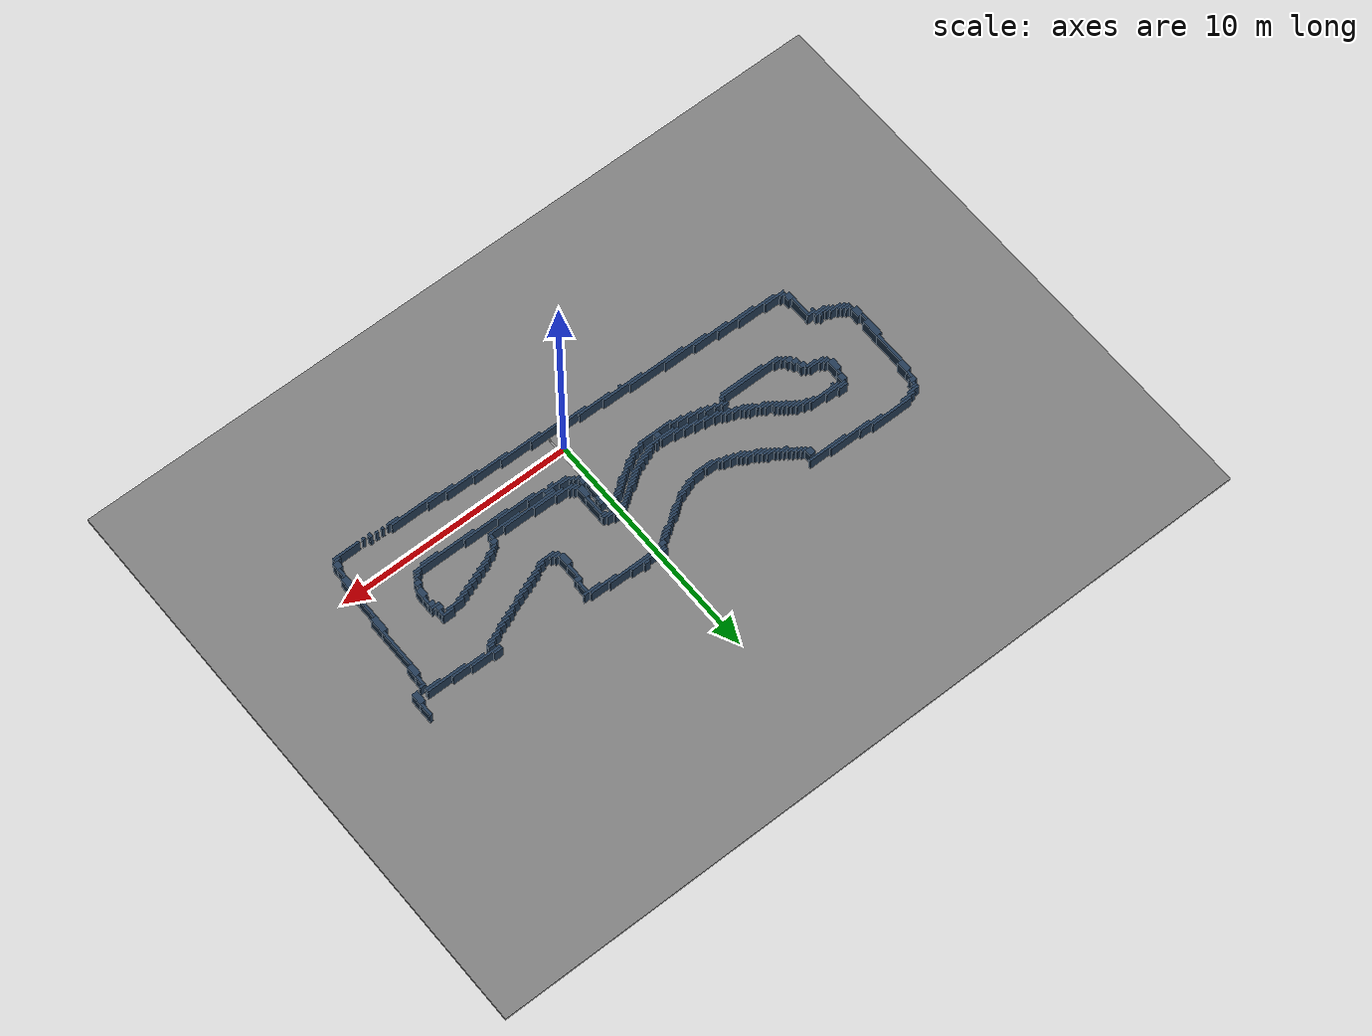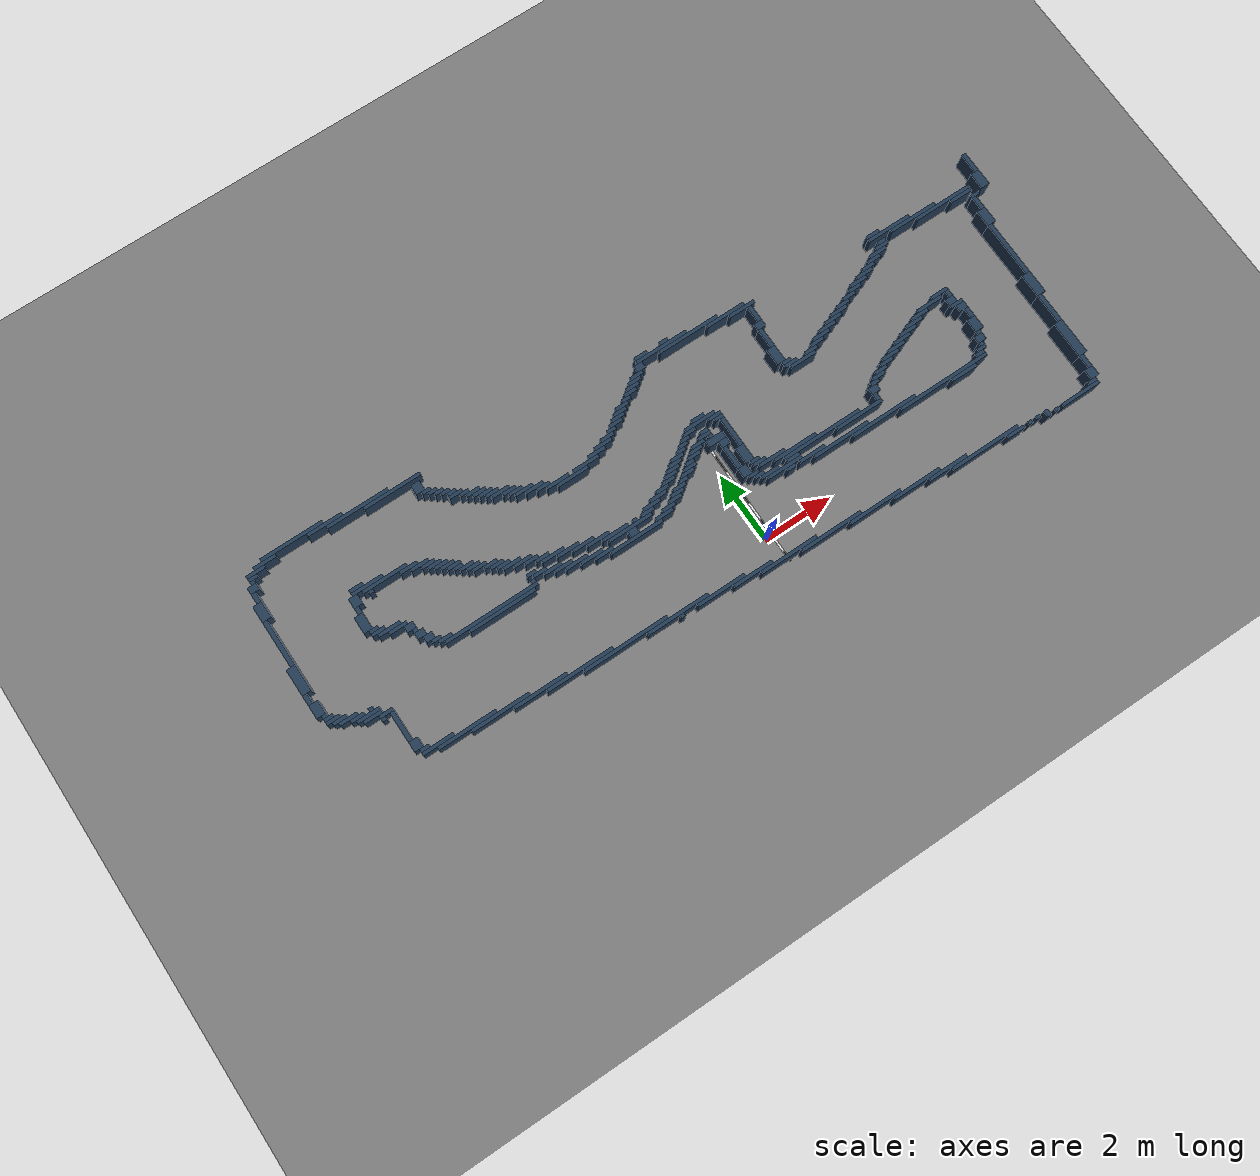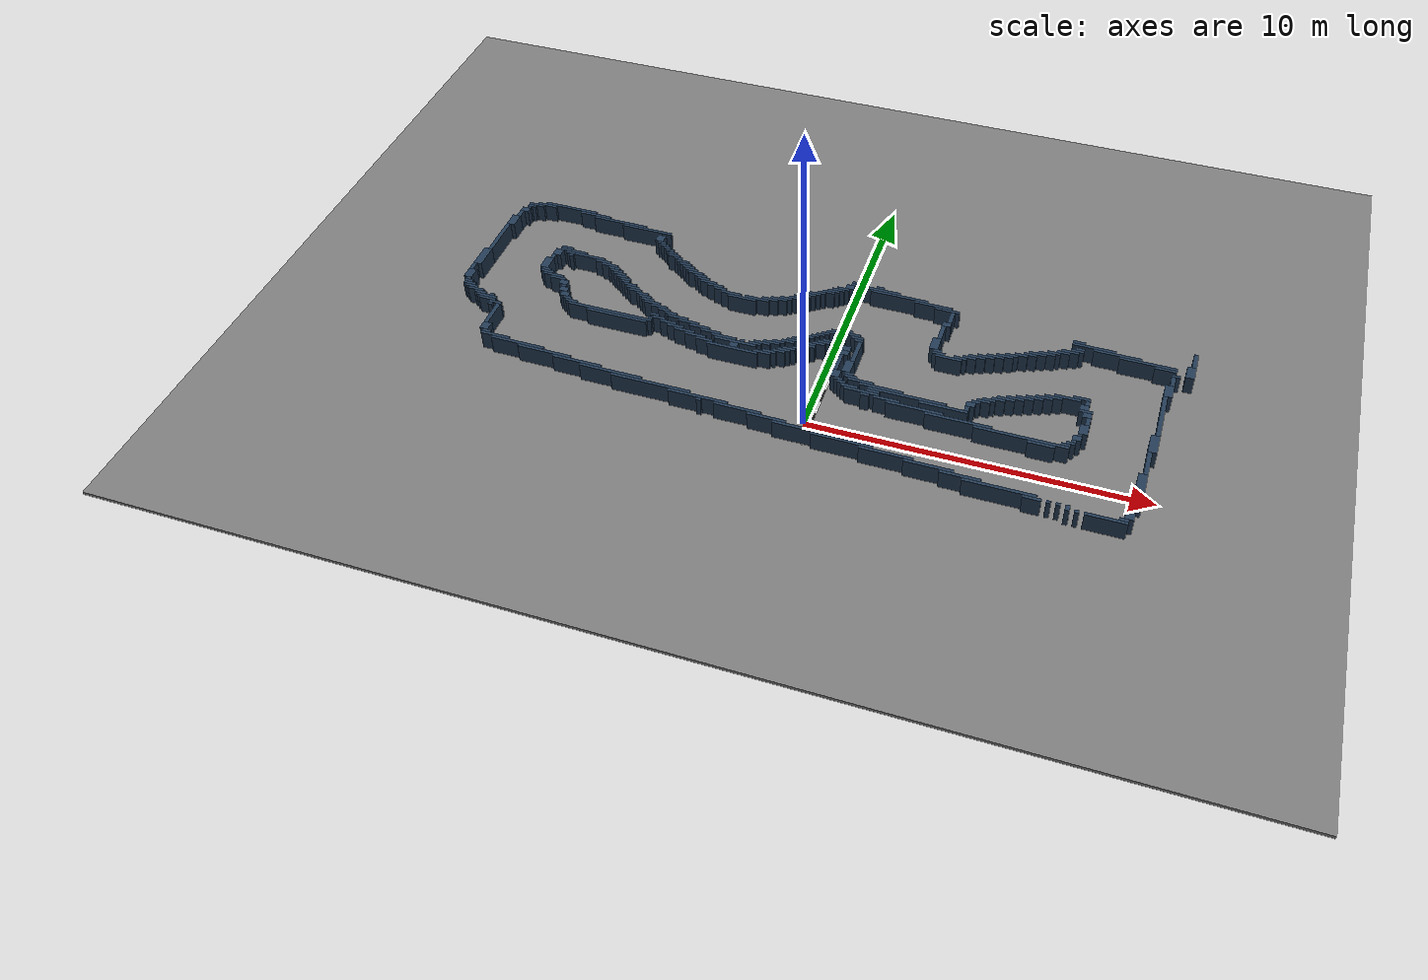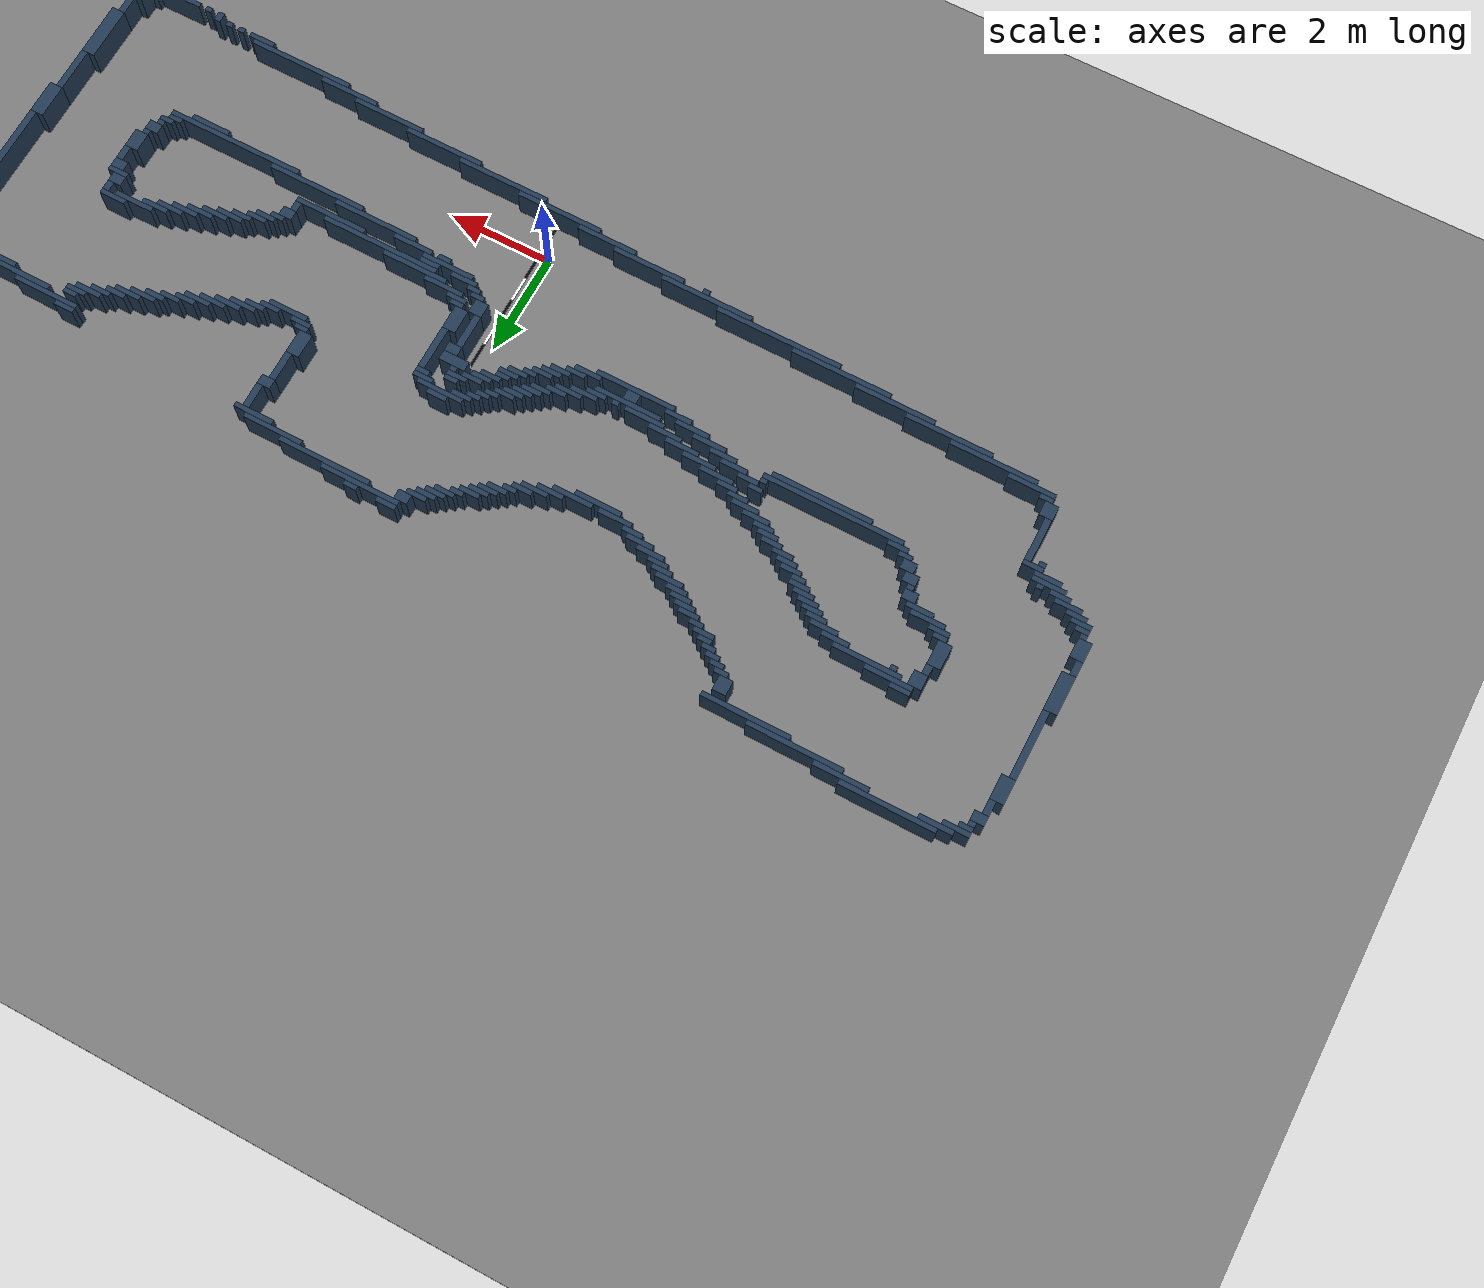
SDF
<?xml version='1.0' encoding='utf-8'?>
<sdf version="1.6">
  <world name="ifac_roboracer">
    <gravity>0 0 -9.8</gravity>
    <physics type="ode">
      <real_time_update_rate>250</real_time_update_rate>
      <max_step_size>0.004</max_step_size>
    </physics>
    <scene>
      <ambient>0.85 0.85 0.85 1</ambient>
      <background>0.65 0.68 0.72 1</background>
      <shadows>false</shadows>
    </scene>
    <model name="ifac_roboracer_map">
      <static>true</static>
      <link name="map">
        <collision name="floor">
          <pose>-1.421400000 3.761420000 -0.050000000 0 0 0</pose>
          <geometry>
            <box>
              <size>33.025000000 24.375000000 0.100000000</size>
            </box>
          </geometry>
        </collision>
        <collision name="wall_0000">
          <pose>-10.000159766 6.427435625 0.300000000 0 0 0</pose>
          <geometry>
            <box>
              <size>1.806054687 0.095214844 0.600000000</size>
            </box>
          </geometry>
        </collision>
        <collision name="wall_0001">
          <pose>-10.838685156 6.332220781 0.300000000 0 0 0</pose>
          <geometry>
            <box>
              <size>0.645019531 0.095214844 0.600000000</size>
            </box>
          </geometry>
        </collision>
        <collision name="wall_0002">
          <pose>-9.097132422 6.332220781 0.300000000 0 0 0</pose>
          <geometry>
            <box>
              <size>1.032031250 0.095214844 0.600000000</size>
            </box>
          </geometry>
        </collision>
        <collision name="wall_0003">
          <pose>-11.161194922 6.237005937 0.300000000 0 0 0</pose>
          <geometry>
            <box>
              <size>0.516015625 0.095214844 0.600000000</size>
            </box>
          </geometry>
        </collision>
        <collision name="wall_0004">
          <pose>-8.194105078 6.237005937 0.300000000 0 0 0</pose>
          <geometry>
            <box>
              <size>1.806054687 0.095214844 0.600000000</size>
            </box>
          </geometry>
        </collision>
        <collision name="wall_0005">
          <pose>-11.290198828 6.141791094 0.300000000 0 0 0</pose>
          <geometry>
            <box>
              <size>0.258007813 0.095214844 0.600000000</size>
            </box>
          </geometry>
        </collision>
        <collision name="wall_0006">
          <pose>-7.226575781 6.141791094 0.300000000 0 0 0</pose>
          <geometry>
            <box>
              <size>1.677050781 0.095214844 0.600000000</size>
            </box>
          </geometry>
        </collision>
        <collision name="wall_0007">
          <pose>-11.354700781 6.046576250 0.300000000 0 0 0</pose>
          <geometry>
            <box>
              <size>0.129003906 0.095214844 0.600000000</size>
            </box>
          </geometry>
        </collision>
        <collision name="wall_0008">
          <pose>-11.419202734 5.903753984 0.300000000 0 0 0</pose>
          <geometry>
            <box>
              <size>0.258007812 0.190429688 0.600000000</size>
            </box>
          </geometry>
        </collision>
        <collision name="wall_0009">
          <pose>-6.646058203 5.856146562 0.300000000 0 0 0</pose>
          <geometry>
            <box>
              <size>0.258007813 0.285644531 0.600000000</size>
            </box>
          </geometry>
        </collision>
        <collision name="wall_0010">
          <pose>-6.517054297 5.665716875 0.300000000 0 0 0</pose>
          <geometry>
            <box>
              <size>0.258007812 0.095214844 0.600000000</size>
            </box>
          </geometry>
        </collision>
        <collision name="wall_0011">
          <pose>-0.002357031 5.665716875 0.300000000 0 0 0</pose>
          <geometry>
            <box>
              <size>0.387011719 0.095214844 0.600000000</size>
            </box>
          </geometry>
        </collision>
        <collision name="wall_0012">
          <pose>0.707164453 5.665716875 0.300000000 0 0 0</pose>
          <geometry>
            <box>
              <size>0.258007813 0.095214844 0.600000000</size>
            </box>
          </geometry>
        </collision>
        <collision name="wall_0013">
          <pose>-11.483704688 5.665716875 0.300000000 0 0 0</pose>
          <geometry>
            <box>
              <size>0.129003906 0.285644531 0.600000000</size>
            </box>
          </geometry>
        </collision>
        <collision name="wall_0014">
          <pose>-6.388050391 5.570502031 0.300000000 0 0 0</pose>
          <geometry>
            <box>
              <size>0.258007812 0.095214844 0.600000000</size>
            </box>
          </geometry>
        </collision>
        <collision name="wall_0015">
          <pose>0.578160547 5.570502031 0.300000000 0 0 0</pose>
          <geometry>
            <box>
              <size>1.548046875 0.095214844 0.600000000</size>
            </box>
          </geometry>
        </collision>
        <collision name="wall_0016">
          <pose>-6.259046484 5.475287187 0.300000000 0 0 0</pose>
          <geometry>
            <box>
              <size>0.258007813 0.095214844 0.600000000</size>
            </box>
          </geometry>
        </collision>
        <collision name="wall_0017">
          <pose>1.352183984 5.475287187 0.300000000 0 0 0</pose>
          <geometry>
            <box>
              <size>1.806054687 0.095214844 0.600000000</size>
            </box>
          </geometry>
        </collision>
        <collision name="wall_0018">
          <pose>-6.130042578 5.380072344 0.300000000 0 0 0</pose>
          <geometry>
            <box>
              <size>0.258007813 0.095214844 0.600000000</size>
            </box>
          </geometry>
        </collision>
        <collision name="wall_0019">
          <pose>-0.195862891 5.427679766 0.300000000 0 0 0</pose>
          <geometry>
            <box>
              <size>0.258007813 0.190429688 0.600000000</size>
            </box>
          </geometry>
        </collision>
        <collision name="wall_0020">
          <pose>2.448717187 5.380072344 0.300000000 0 0 0</pose>
          <geometry>
            <box>
              <size>1.161035156 0.095214844 0.600000000</size>
            </box>
          </geometry>
        </collision>
        <collision name="wall_0021">
          <pose>-6.001038672 5.284857500 0.300000000 0 0 0</pose>
          <geometry>
            <box>
              <size>0.258007813 0.095214844 0.600000000</size>
            </box>
          </geometry>
        </collision>
        <collision name="wall_0022">
          <pose>-0.389368750 5.284857500 0.300000000 0 0 0</pose>
          <geometry>
            <box>
              <size>0.387011719 0.095214844 0.600000000</size>
            </box>
          </geometry>
        </collision>
        <collision name="wall_0023">
          <pose>2.900230859 5.284857500 0.300000000 0 0 0</pose>
          <geometry>
            <box>
              <size>0.774023438 0.095214844 0.600000000</size>
            </box>
          </geometry>
        </collision>
        <collision name="wall_0024">
          <pose>-5.936536719 5.189642656 0.300000000 0 0 0</pose>
          <geometry>
            <box>
              <size>0.387011719 0.095214844 0.600000000</size>
            </box>
          </geometry>
        </collision>
        <collision name="wall_0025">
          <pose>-0.518372656 5.189642656 0.300000000 0 0 0</pose>
          <geometry>
            <box>
              <size>0.387011719 0.095214844 0.600000000</size>
            </box>
          </geometry>
        </collision>
        <collision name="wall_0026">
          <pose>-11.548206641 5.284857500 0.300000000 0 0 0</pose>
          <geometry>
            <box>
              <size>0.258007813 0.476074219 0.600000000</size>
            </box>
          </geometry>
        </collision>
        <collision name="wall_0027">
          <pose>-5.743030859 5.094427812 0.300000000 0 0 0</pose>
          <geometry>
            <box>
              <size>0.258007812 0.095214844 0.600000000</size>
            </box>
          </geometry>
        </collision>
        <collision name="wall_0028">
          <pose>-0.647376563 5.094427812 0.300000000 0 0 0</pose>
          <geometry>
            <box>
              <size>0.387011719 0.095214844 0.600000000</size>
            </box>
          </geometry>
        </collision>
        <collision name="wall_0029">
          <pose>6.963853906 5.094427812 0.300000000 0 0 0</pose>
          <geometry>
            <box>
              <size>0.387011719 0.095214844 0.600000000</size>
            </box>
          </geometry>
        </collision>
        <collision name="wall_0030">
          <pose>10.317955469 5.332464922 0.300000000 0 0 0</pose>
          <geometry>
            <box>
              <size>0.129003906 0.571289062 0.600000000</size>
            </box>
          </geometry>
        </collision>
        <collision name="wall_0031">
          <pose>-5.549525000 4.999212969 0.300000000 0 0 0</pose>
          <geometry>
            <box>
              <size>0.387011719 0.095214844 0.600000000</size>
            </box>
          </geometry>
        </collision>
        <collision name="wall_0032">
          <pose>-0.776380469 4.999212969 0.300000000 0 0 0</pose>
          <geometry>
            <box>
              <size>0.387011719 0.095214844 0.600000000</size>
            </box>
          </geometry>
        </collision>
        <collision name="wall_0033">
          <pose>7.415367578 4.999212969 0.300000000 0 0 0</pose>
          <geometry>
            <box>
              <size>1.290039062 0.095214844 0.600000000</size>
            </box>
          </geometry>
        </collision>
        <collision name="wall_0034">
          <pose>-5.420521094 4.903998125 0.300000000 0 0 0</pose>
          <geometry>
            <box>
              <size>0.387011719 0.095214844 0.600000000</size>
            </box>
          </geometry>
        </collision>
        <collision name="wall_0035">
          <pose>-0.969886328 4.903998125 0.300000000 0 0 0</pose>
          <geometry>
            <box>
              <size>0.258007813 0.095214844 0.600000000</size>
            </box>
          </geometry>
        </collision>
        <collision name="wall_0036">
          <pose>8.124889062 4.903998125 0.300000000 0 0 0</pose>
          <geometry>
            <box>
              <size>1.419042969 0.095214844 0.600000000</size>
            </box>
          </geometry>
        </collision>
        <collision name="wall_0037">
          <pose>-5.291517188 4.808783281 0.300000000 0 0 0</pose>
          <geometry>
            <box>
              <size>0.387011719 0.095214844 0.600000000</size>
            </box>
          </geometry>
        </collision>
        <collision name="wall_0038">
          <pose>-1.163392188 4.808783281 0.300000000 0 0 0</pose>
          <geometry>
            <box>
              <size>0.387011719 0.095214844 0.600000000</size>
            </box>
          </geometry>
        </collision>
        <collision name="wall_0039">
          <pose>3.093736719 4.999212969 0.300000000 0 0 0</pose>
          <geometry>
            <box>
              <size>0.129003906 0.476074219 0.600000000</size>
            </box>
          </geometry>
        </collision>
        <collision name="wall_0040">
          <pose>7.028355859 4.808783281 0.300000000 0 0 0</pose>
          <geometry>
            <box>
              <size>0.258007812 0.095214844 0.600000000</size>
            </box>
          </geometry>
        </collision>
        <collision name="wall_0041">
          <pose>9.027916406 4.808783281 0.300000000 0 0 0</pose>
          <geometry>
            <box>
              <size>1.677050781 0.095214844 0.600000000</size>
            </box>
          </geometry>
        </collision>
        <collision name="wall_0042">
          <pose>-5.162513281 4.713568437 0.300000000 0 0 0</pose>
          <geometry>
            <box>
              <size>0.387011719 0.095214844 0.600000000</size>
            </box>
          </geometry>
        </collision>
        <collision name="wall_0043">
          <pose>-1.292396094 4.713568437 0.300000000 0 0 0</pose>
          <geometry>
            <box>
              <size>0.387011719 0.095214844 0.600000000</size>
            </box>
          </geometry>
        </collision>
        <collision name="wall_0044">
          <pose>6.963853906 4.713568437 0.300000000 0 0 0</pose>
          <geometry>
            <box>
              <size>0.387011719 0.095214844 0.600000000</size>
            </box>
          </geometry>
        </collision>
        <collision name="wall_0045">
          <pose>9.543932031 4.713568437 0.300000000 0 0 0</pose>
          <geometry>
            <box>
              <size>0.645019531 0.095214844 0.600000000</size>
            </box>
          </geometry>
        </collision>
        <collision name="wall_0046">
          <pose>-4.969007422 4.618353594 0.300000000 0 0 0</pose>
          <geometry>
            <box>
              <size>0.516015625 0.095214844 0.600000000</size>
            </box>
          </geometry>
        </collision>
        <collision name="wall_0047">
          <pose>-1.421400000 4.618353594 0.300000000 0 0 0</pose>
          <geometry>
            <box>
              <size>0.387011719 0.095214844 0.600000000</size>
            </box>
          </geometry>
        </collision>
        <collision name="wall_0048">
          <pose>3.029234766 4.665961016 0.300000000 0 0 0</pose>
          <geometry>
            <box>
              <size>0.258007813 0.190429688 0.600000000</size>
            </box>
          </geometry>
        </collision>
        <collision name="wall_0049">
          <pose>6.770348047 4.618353594 0.300000000 0 0 0</pose>
          <geometry>
            <box>
              <size>0.516015625 0.095214844 0.600000000</size>
            </box>
          </geometry>
        </collision>
        <collision name="wall_0050">
          <pose>10.253453516 4.808783281 0.300000000 0 0 0</pose>
          <geometry>
            <box>
              <size>0.258007812 0.476074219 0.600000000</size>
            </box>
          </geometry>
        </collision>
        <collision name="wall_0051">
          <pose>-9.290638281 4.523138750 0.300000000 0 0 0</pose>
          <geometry>
            <box>
              <size>0.387011719 0.095214844 0.600000000</size>
            </box>
          </geometry>
        </collision>
        <collision name="wall_0052">
          <pose>-4.775501563 4.523138750 0.300000000 0 0 0</pose>
          <geometry>
            <box>
              <size>0.387011719 0.095214844 0.600000000</size>
            </box>
          </geometry>
        </collision>
        <collision name="wall_0053">
          <pose>-1.550403906 4.523138750 0.300000000 0 0 0</pose>
          <geometry>
            <box>
              <size>0.387011719 0.095214844 0.600000000</size>
            </box>
          </geometry>
        </collision>
        <collision name="wall_0054">
          <pose>6.576842187 4.523138750 0.300000000 0 0 0</pose>
          <geometry>
            <box>
              <size>0.387011719 0.095214844 0.600000000</size>
            </box>
          </geometry>
        </collision>
        <collision name="wall_0055">
          <pose>9.866441797 4.523138750 0.300000000 0 0 0</pose>
          <geometry>
            <box>
              <size>0.258007813 0.095214844 0.600000000</size>
            </box>
          </geometry>
        </collision>
        <collision name="wall_0056">
          <pose>-9.032630469 4.427923906 0.300000000 0 0 0</pose>
          <geometry>
            <box>
              <size>0.903027344 0.095214844 0.600000000</size>
            </box>
          </geometry>
        </collision>
        <collision name="wall_0057">
          <pose>-4.646497656 4.427923906 0.300000000 0 0 0</pose>
          <geometry>
            <box>
              <size>0.387011719 0.095214844 0.600000000</size>
            </box>
          </geometry>
        </collision>
        <collision name="wall_0058">
          <pose>-1.743909766 4.427923906 0.300000000 0 0 0</pose>
          <geometry>
            <box>
              <size>0.258007812 0.095214844 0.600000000</size>
            </box>
          </geometry>
        </collision>
        <collision name="wall_0059">
          <pose>6.318834375 4.427923906 0.300000000 0 0 0</pose>
          <geometry>
            <box>
              <size>0.387011719 0.095214844 0.600000000</size>
            </box>
          </geometry>
        </collision>
        <collision name="wall_0060">
          <pose>-8.581116797 4.332709062 0.300000000 0 0 0</pose>
          <geometry>
            <box>
              <size>1.290039062 0.095214844 0.600000000</size>
            </box>
          </geometry>
        </collision>
        <collision name="wall_0061">
          <pose>-4.452991797 4.332709062 0.300000000 0 0 0</pose>
          <geometry>
            <box>
              <size>0.516015625 0.095214844 0.600000000</size>
            </box>
          </geometry>
        </collision>
        <collision name="wall_0062">
          <pose>-1.937415625 4.332709062 0.300000000 0 0 0</pose>
          <geometry>
            <box>
              <size>0.387011719 0.095214844 0.600000000</size>
            </box>
          </geometry>
        </collision>
        <collision name="wall_0063">
          <pose>6.125328516 4.332709062 0.300000000 0 0 0</pose>
          <geometry>
            <box>
              <size>0.516015625 0.095214844 0.600000000</size>
            </box>
          </geometry>
        </collision>
        <collision name="wall_0064">
          <pose>-9.032630469 4.237494219 0.300000000 0 0 0</pose>
          <geometry>
            <box>
              <size>0.129003906 0.095214844 0.600000000</size>
            </box>
          </geometry>
        </collision>
        <collision name="wall_0065">
          <pose>-7.936097266 4.237494219 0.300000000 0 0 0</pose>
          <geometry>
            <box>
              <size>0.516015625 0.095214844 0.600000000</size>
            </box>
          </geometry>
        </collision>
        <collision name="wall_0066">
          <pose>-4.194983984 4.237494219 0.300000000 0 0 0</pose>
          <geometry>
            <box>
              <size>0.516015625 0.095214844 0.600000000</size>
            </box>
          </geometry>
        </collision>
        <collision name="wall_0067">
          <pose>-2.130921484 4.237494219 0.300000000 0 0 0</pose>
          <geometry>
            <box>
              <size>0.516015625 0.095214844 0.600000000</size>
            </box>
          </geometry>
        </collision>
        <collision name="wall_0068">
          <pose>5.867320703 4.237494219 0.300000000 0 0 0</pose>
          <geometry>
            <box>
              <size>0.516015625 0.095214844 0.600000000</size>
            </box>
          </geometry>
        </collision>
        <collision name="wall_0069">
          <pose>-9.484144141 4.237494219 0.300000000 0 0 0</pose>
          <geometry>
            <box>
              <size>0.258007813 0.285644531 0.600000000</size>
            </box>
          </geometry>
        </collision>
        <collision name="wall_0070">
          <pose>-7.678089453 4.142279375 0.300000000 0 0 0</pose>
          <geometry>
            <box>
              <size>0.516015625 0.095214844 0.600000000</size>
            </box>
          </geometry>
        </collision>
        <collision name="wall_0071">
          <pose>-4.001478125 4.142279375 0.300000000 0 0 0</pose>
          <geometry>
            <box>
              <size>0.387011719 0.095214844 0.600000000</size>
            </box>
          </geometry>
        </collision>
        <collision name="wall_0072">
          <pose>-2.388929297 4.142279375 0.300000000 0 0 0</pose>
          <geometry>
            <box>
              <size>0.516015625 0.095214844 0.600000000</size>
            </box>
          </geometry>
        </collision>
        <collision name="wall_0073">
          <pose>5.673814844 4.142279375 0.300000000 0 0 0</pose>
          <geometry>
            <box>
              <size>0.387011719 0.095214844 0.600000000</size>
            </box>
          </geometry>
        </collision>
        <collision name="wall_0074">
          <pose>9.801939844 4.285101641 0.300000000 0 0 0</pose>
          <geometry>
            <box>
              <size>0.129003906 0.380859375 0.600000000</size>
            </box>
          </geometry>
        </collision>
        <collision name="wall_0075">
          <pose>-7.484583594 4.047064531 0.300000000 0 0 0</pose>
          <geometry>
            <box>
              <size>0.387011719 0.095214844 0.600000000</size>
            </box>
          </geometry>
        </collision>
        <collision name="wall_0076">
          <pose>-3.614466406 4.047064531 0.300000000 0 0 0</pose>
          <geometry>
            <box>
              <size>0.645019531 0.095214844 0.600000000</size>
            </box>
          </geometry>
        </collision>
        <collision name="wall_0077">
          <pose>-2.775941016 4.047064531 0.300000000 0 0 0</pose>
          <geometry>
            <box>
              <size>0.774023438 0.095214844 0.600000000</size>
            </box>
          </geometry>
        </collision>
        <collision name="wall_0078">
          <pose>2.964732812 4.285101641 0.300000000 0 0 0</pose>
          <geometry>
            <box>
              <size>0.129003906 0.571289062 0.600000000</size>
            </box>
          </geometry>
        </collision>
        <collision name="wall_0079">
          <pose>5.415807031 4.047064531 0.300000000 0 0 0</pose>
          <geometry>
            <box>
              <size>0.387011719 0.095214844 0.600000000</size>
            </box>
          </geometry>
        </collision>
        <collision name="wall_0080">
          <pose>-9.548646094 3.999457109 0.300000000 0 0 0</pose>
          <geometry>
            <box>
              <size>0.129003906 0.190429688 0.600000000</size>
            </box>
          </geometry>
        </collision>
        <collision name="wall_0081">
          <pose>-7.355579688 3.951849687 0.300000000 0 0 0</pose>
          <geometry>
            <box>
              <size>0.387011719 0.095214844 0.600000000</size>
            </box>
          </geometry>
        </collision>
        <collision name="wall_0082">
          <pose>-3.227454688 3.951849687 0.300000000 0 0 0</pose>
          <geometry>
            <box>
              <size>0.903027344 0.095214844 0.600000000</size>
            </box>
          </geometry>
        </collision>
        <collision name="wall_0083">
          <pose>5.157799219 3.951849687 0.300000000 0 0 0</pose>
          <geometry>
            <box>
              <size>0.387011719 0.095214844 0.600000000</size>
            </box>
          </geometry>
        </collision>
        <collision name="wall_0084">
          <pose>-7.226575781 3.856634844 0.300000000 0 0 0</pose>
          <geometry>
            <box>
              <size>0.387011719 0.095214844 0.600000000</size>
            </box>
          </geometry>
        </collision>
        <collision name="wall_0085">
          <pose>4.964293359 3.856634844 0.300000000 0 0 0</pose>
          <geometry>
            <box>
              <size>0.516015625 0.095214844 0.600000000</size>
            </box>
          </geometry>
        </collision>
        <collision name="wall_0086">
          <pose>-11.612708594 4.380316484 0.300000000 0 0 0</pose>
          <geometry>
            <box>
              <size>0.129003906 1.333007812 0.600000000</size>
            </box>
          </geometry>
        </collision>
        <collision name="wall_0087">
          <pose>-7.097571875 3.761420000 0.300000000 0 0 0</pose>
          <geometry>
            <box>
              <size>0.387011719 0.095214844 0.600000000</size>
            </box>
          </geometry>
        </collision>
        <collision name="wall_0088">
          <pose>4.706285547 3.761420000 0.300000000 0 0 0</pose>
          <geometry>
            <box>
              <size>0.516015625 0.095214844 0.600000000</size>
            </box>
          </geometry>
        </collision>
        <collision name="wall_0089">
          <pose>-6.968567969 3.666205156 0.300000000 0 0 0</pose>
          <geometry>
            <box>
              <size>0.387011719 0.095214844 0.600000000</size>
            </box>
          </geometry>
        </collision>
        <collision name="wall_0090">
          <pose>4.448277734 3.666205156 0.300000000 0 0 0</pose>
          <geometry>
            <box>
              <size>0.516015625 0.095214844 0.600000000</size>
            </box>
          </geometry>
        </collision>
        <collision name="wall_0091">
          <pose>9.737437891 3.856634844 0.300000000 0 0 0</pose>
          <geometry>
            <box>
              <size>0.258007813 0.476074219 0.600000000</size>
            </box>
          </geometry>
        </collision>
        <collision name="wall_0092">
          <pose>-6.904066016 3.570990312 0.300000000 0 0 0</pose>
          <geometry>
            <box>
              <size>0.258007813 0.095214844 0.600000000</size>
            </box>
          </geometry>
        </collision>
        <collision name="wall_0093">
          <pose>2.900230859 3.761420000 0.300000000 0 0 0</pose>
          <geometry>
            <box>
              <size>0.258007813 0.476074219 0.600000000</size>
            </box>
          </geometry>
        </collision>
        <collision name="wall_0094">
          <pose>4.190269922 3.570990312 0.300000000 0 0 0</pose>
          <geometry>
            <box>
              <size>0.516015625 0.095214844 0.600000000</size>
            </box>
          </geometry>
        </collision>
        <collision name="wall_0095">
          <pose>-9.613148047 3.666205156 0.300000000 0 0 0</pose>
          <geometry>
            <box>
              <size>0.258007812 0.476074219 0.600000000</size>
            </box>
          </geometry>
        </collision>
        <collision name="wall_0096">
          <pose>-6.710560156 3.475775469 0.300000000 0 0 0</pose>
          <geometry>
            <box>
              <size>0.387011719 0.095214844 0.600000000</size>
            </box>
          </geometry>
        </collision>
        <collision name="wall_0097">
          <pose>0.255650781 3.475775469 0.300000000 0 0 0</pose>
          <geometry>
            <box>
              <size>0.387011719 0.095214844 0.600000000</size>
            </box>
          </geometry>
        </collision>
        <collision name="wall_0098">
          <pose>3.029234766 3.475775469 0.300000000 0 0 0</pose>
          <geometry>
            <box>
              <size>0.258007813 0.095214844 0.600000000</size>
            </box>
          </geometry>
        </collision>
        <collision name="wall_0099">
          <pose>3.996764062 3.475775469 0.300000000 0 0 0</pose>
          <geometry>
            <box>
              <size>0.387011719 0.095214844 0.600000000</size>
            </box>
          </geometry>
        </collision>
        <collision name="wall_0100">
          <pose>-9.484144141 3.380560625 0.300000000 0 0 0</pose>
          <geometry>
            <box>
              <size>0.258007813 0.095214844 0.600000000</size>
            </box>
          </geometry>
        </collision>
        <collision name="wall_0101">
          <pose>-6.581556250 3.380560625 0.300000000 0 0 0</pose>
          <geometry>
            <box>
              <size>0.387011719 0.095214844 0.600000000</size>
            </box>
          </geometry>
        </collision>
        <collision name="wall_0102">
          <pose>0.255650781 3.380560625 0.300000000 0 0 0</pose>
          <geometry>
            <box>
              <size>0.903027344 0.095214844 0.600000000</size>
            </box>
          </geometry>
        </collision>
        <collision name="wall_0103">
          <pose>3.093736719 3.380560625 0.300000000 0 0 0</pose>
          <geometry>
            <box>
              <size>0.387011719 0.095214844 0.600000000</size>
            </box>
          </geometry>
        </collision>
        <collision name="wall_0104">
          <pose>3.738756250 3.380560625 0.300000000 0 0 0</pose>
          <geometry>
            <box>
              <size>0.387011719 0.095214844 0.600000000</size>
            </box>
          </geometry>
        </collision>
        <collision name="wall_0105">
          <pose>-9.419642188 3.285345781 0.300000000 0 0 0</pose>
          <geometry>
            <box>
              <size>0.387011719 0.095214844 0.600000000</size>
            </box>
          </geometry>
        </collision>
        <collision name="wall_0106">
          <pose>-6.452552344 3.285345781 0.300000000 0 0 0</pose>
          <geometry>
            <box>
              <size>0.387011719 0.095214844 0.600000000</size>
            </box>
          </geometry>
        </collision>
        <collision name="wall_0107">
          <pose>-0.131360938 3.285345781 0.300000000 0 0 0</pose>
          <geometry>
            <box>
              <size>0.387011719 0.095214844 0.600000000</size>
            </box>
          </geometry>
        </collision>
        <collision name="wall_0108">
          <pose>0.642662500 3.285345781 0.300000000 0 0 0</pose>
          <geometry>
            <box>
              <size>0.387011719 0.095214844 0.600000000</size>
            </box>
          </geometry>
        </collision>
        <collision name="wall_0109">
          <pose>3.416246484 3.285345781 0.300000000 0 0 0</pose>
          <geometry>
            <box>
              <size>0.774023437 0.095214844 0.600000000</size>
            </box>
          </geometry>
        </collision>
        <collision name="wall_0110">
          <pose>-9.161634375 3.190130937 0.300000000 0 0 0</pose>
          <geometry>
            <box>
              <size>0.645019531 0.095214844 0.600000000</size>
            </box>
          </geometry>
        </collision>
        <collision name="wall_0111">
          <pose>-6.194544531 3.190130937 0.300000000 0 0 0</pose>
          <geometry>
            <box>
              <size>0.387011719 0.095214844 0.600000000</size>
            </box>
          </geometry>
        </collision>
        <collision name="wall_0112">
          <pose>-0.324866797 3.190130937 0.300000000 0 0 0</pose>
          <geometry>
            <box>
              <size>0.258007813 0.095214844 0.600000000</size>
            </box>
          </geometry>
        </collision>
        <collision name="wall_0113">
          <pose>0.707164453 3.190130937 0.300000000 0 0 0</pose>
          <geometry>
            <box>
              <size>0.258007813 0.095214844 0.600000000</size>
            </box>
          </geometry>
        </collision>
        <collision name="wall_0114">
          <pose>-8.968128516 3.094916094 0.300000000 0 0 0</pose>
          <geometry>
            <box>
              <size>0.516015625 0.095214844 0.600000000</size>
            </box>
          </geometry>
        </collision>
        <collision name="wall_0115">
          <pose>-6.065540625 3.094916094 0.300000000 0 0 0</pose>
          <geometry>
            <box>
              <size>0.387011719 0.095214844 0.600000000</size>
            </box>
          </geometry>
        </collision>
        <collision name="wall_0116">
          <pose>-0.453870703 3.094916094 0.300000000 0 0 0</pose>
          <geometry>
            <box>
              <size>0.258007812 0.095214844 0.600000000</size>
            </box>
          </geometry>
        </collision>
        <collision name="wall_0117">
          <pose>0.191148828 3.094916094 0.300000000 0 0 0</pose>
          <geometry>
            <box>
              <size>0.258007812 0.095214844 0.600000000</size>
            </box>
          </geometry>
        </collision>
        <collision name="wall_0118">
          <pose>-11.677210547 3.332953203 0.300000000 0 0 0</pose>
          <geometry>
            <box>
              <size>0.258007813 0.761718750 0.600000000</size>
            </box>
          </geometry>
        </collision>
        <collision name="wall_0119">
          <pose>-5.936536719 2.999701250 0.300000000 0 0 0</pose>
          <geometry>
            <box>
              <size>0.387011719 0.095214844 0.600000000</size>
            </box>
          </geometry>
        </collision>
        <collision name="wall_0120">
          <pose>-0.582874609 2.999701250 0.300000000 0 0 0</pose>
          <geometry>
            <box>
              <size>0.258007813 0.095214844 0.600000000</size>
            </box>
          </geometry>
        </collision>
        <collision name="wall_0121">
          <pose>0.126646875 2.999701250 0.300000000 0 0 0</pose>
          <geometry>
            <box>
              <size>0.387011719 0.095214844 0.600000000</size>
            </box>
          </geometry>
        </collision>
        <collision name="wall_0122">
          <pose>-8.710120703 2.952093828 0.300000000 0 0 0</pose>
          <geometry>
            <box>
              <size>0.258007813 0.190429688 0.600000000</size>
            </box>
          </geometry>
        </collision>
        <collision name="wall_0123">
          <pose>-5.743030859 2.904486406 0.300000000 0 0 0</pose>
          <geometry>
            <box>
              <size>0.516015625 0.095214844 0.600000000</size>
            </box>
          </geometry>
        </collision>
        <collision name="wall_0124">
          <pose>-0.776380469 2.904486406 0.300000000 0 0 0</pose>
          <geometry>
            <box>
              <size>0.387011719 0.095214844 0.600000000</size>
            </box>
          </geometry>
        </collision>
        <collision name="wall_0125">
          <pose>-0.131360938 2.904486406 0.300000000 0 0 0</pose>
          <geometry>
            <box>
              <size>0.387011719 0.095214844 0.600000000</size>
            </box>
          </geometry>
        </collision>
        <collision name="wall_0126">
          <pose>0.255650781 2.904486406 0.300000000 0 0 0</pose>
          <geometry>
            <box>
              <size>0.129003906 0.095214844 0.600000000</size>
            </box>
          </geometry>
        </collision>
        <collision name="wall_0127">
          <pose>-8.645618750 2.809271562 0.300000000 0 0 0</pose>
          <geometry>
            <box>
              <size>0.129003906 0.095214844 0.600000000</size>
            </box>
          </geometry>
        </collision>
        <collision name="wall_0128">
          <pose>-5.485023047 2.809271562 0.300000000 0 0 0</pose>
          <geometry>
            <box>
              <size>0.516015625 0.095214844 0.600000000</size>
            </box>
          </geometry>
        </collision>
        <collision name="wall_0129">
          <pose>-0.905384375 2.809271562 0.300000000 0 0 0</pose>
          <geometry>
            <box>
              <size>0.387011719 0.095214844 0.600000000</size>
            </box>
          </geometry>
        </collision>
        <collision name="wall_0130">
          <pose>-0.260364844 2.809271562 0.300000000 0 0 0</pose>
          <geometry>
            <box>
              <size>0.387011719 0.095214844 0.600000000</size>
            </box>
          </geometry>
        </collision>
        <collision name="wall_0131">
          <pose>7.415367578 2.809271562 0.300000000 0 0 0</pose>
          <geometry>
            <box>
              <size>0.516015625 0.095214844 0.600000000</size>
            </box>
          </geometry>
        </collision>
        <collision name="wall_0132">
          <pose>-11.741712500 2.809271562 0.300000000 0 0 0</pose>
          <geometry>
            <box>
              <size>0.129003906 0.285644531 0.600000000</size>
            </box>
          </geometry>
        </collision>
        <collision name="wall_0133">
          <pose>-5.291517188 2.714056719 0.300000000 0 0 0</pose>
          <geometry>
            <box>
              <size>0.387011719 0.095214844 0.600000000</size>
            </box>
          </geometry>
        </collision>
        <collision name="wall_0134">
          <pose>-1.034388281 2.714056719 0.300000000 0 0 0</pose>
          <geometry>
            <box>
              <size>0.387011719 0.095214844 0.600000000</size>
            </box>
          </geometry>
        </collision>
        <collision name="wall_0135">
          <pose>-0.389368750 2.714056719 0.300000000 0 0 0</pose>
          <geometry>
            <box>
              <size>0.387011719 0.095214844 0.600000000</size>
            </box>
          </geometry>
        </collision>
        <collision name="wall_0136">
          <pose>0.320152734 2.761664141 0.300000000 0 0 0</pose>
          <geometry>
            <box>
              <size>0.516015625 0.190429688 0.600000000</size>
            </box>
          </geometry>
        </collision>
        <collision name="wall_0137">
          <pose>7.028355859 2.714056719 0.300000000 0 0 0</pose>
          <geometry>
            <box>
              <size>0.774023437 0.095214844 0.600000000</size>
            </box>
          </geometry>
        </collision>
        <collision name="wall_0138">
          <pose>-8.581116797 2.666449297 0.300000000 0 0 0</pose>
          <geometry>
            <box>
              <size>0.258007813 0.190429688 0.600000000</size>
            </box>
          </geometry>
        </collision>
        <collision name="wall_0139">
          <pose>-5.033509375 2.618841875 0.300000000 0 0 0</pose>
          <geometry>
            <box>
              <size>0.387011719 0.095214844 0.600000000</size>
            </box>
          </geometry>
        </collision>
        <collision name="wall_0140">
          <pose>-1.163392188 2.618841875 0.300000000 0 0 0</pose>
          <geometry>
            <box>
              <size>0.387011719 0.095214844 0.600000000</size>
            </box>
          </geometry>
        </collision>
        <collision name="wall_0141">
          <pose>-0.582874609 2.618841875 0.300000000 0 0 0</pose>
          <geometry>
            <box>
              <size>0.258007813 0.095214844 0.600000000</size>
            </box>
          </geometry>
        </collision>
        <collision name="wall_0142">
          <pose>6.641344141 2.618841875 0.300000000 0 0 0</pose>
          <geometry>
            <box>
              <size>0.516015625 0.095214844 0.600000000</size>
            </box>
          </geometry>
        </collision>
        <collision name="wall_0143">
          <pose>7.608873437 2.666449297 0.300000000 0 0 0</pose>
          <geometry>
            <box>
              <size>0.129003906 0.190429688 0.600000000</size>
            </box>
          </geometry>
        </collision>
        <collision name="wall_0144">
          <pose>-4.775501563 2.523627031 0.300000000 0 0 0</pose>
          <geometry>
            <box>
              <size>0.645019531 0.095214844 0.600000000</size>
            </box>
          </geometry>
        </collision>
        <collision name="wall_0145">
          <pose>-1.292396094 2.523627031 0.300000000 0 0 0</pose>
          <geometry>
            <box>
              <size>0.387011719 0.095214844 0.600000000</size>
            </box>
          </geometry>
        </collision>
        <collision name="wall_0146">
          <pose>-0.647376563 2.523627031 0.300000000 0 0 0</pose>
          <geometry>
            <box>
              <size>0.387011719 0.095214844 0.600000000</size>
            </box>
          </geometry>
        </collision>
        <collision name="wall_0147">
          <pose>0.449156641 2.571234453 0.300000000 0 0 0</pose>
          <geometry>
            <box>
              <size>0.258007813 0.190429688 0.600000000</size>
            </box>
          </geometry>
        </collision>
        <collision name="wall_0148">
          <pose>6.383336328 2.523627031 0.300000000 0 0 0</pose>
          <geometry>
            <box>
              <size>0.516015625 0.095214844 0.600000000</size>
            </box>
          </geometry>
        </collision>
        <collision name="wall_0149">
          <pose>-8.452112891 2.476019609 0.300000000 0 0 0</pose>
          <geometry>
            <box>
              <size>0.258007812 0.190429688 0.600000000</size>
            </box>
          </geometry>
        </collision>
        <collision name="wall_0150">
          <pose>-5.485023047 2.428412187 0.300000000 0 0 0</pose>
          <geometry>
            <box>
              <size>0.258007813 0.095214844 0.600000000</size>
            </box>
          </geometry>
        </collision>
        <collision name="wall_0151">
          <pose>-4.388489844 2.428412187 0.300000000 0 0 0</pose>
          <geometry>
            <box>
              <size>0.645019531 0.095214844 0.600000000</size>
            </box>
          </geometry>
        </collision>
        <collision name="wall_0152">
          <pose>-1.550403906 2.428412187 0.300000000 0 0 0</pose>
          <geometry>
            <box>
              <size>0.387011719 0.095214844 0.600000000</size>
            </box>
          </geometry>
        </collision>
        <collision name="wall_0153">
          <pose>-0.776380469 2.428412187 0.300000000 0 0 0</pose>
          <geometry>
            <box>
              <size>0.387011719 0.095214844 0.600000000</size>
            </box>
          </geometry>
        </collision>
        <collision name="wall_0154">
          <pose>6.125328516 2.428412187 0.300000000 0 0 0</pose>
          <geometry>
            <box>
              <size>0.516015625 0.095214844 0.600000000</size>
            </box>
          </geometry>
        </collision>
        <collision name="wall_0155">
          <pose>7.544371484 2.476019609 0.300000000 0 0 0</pose>
          <geometry>
            <box>
              <size>0.258007813 0.190429688 0.600000000</size>
            </box>
          </geometry>
        </collision>
        <collision name="wall_0156">
          <pose>-11.677210547 2.476019609 0.300000000 0 0 0</pose>
          <geometry>
            <box>
              <size>0.258007813 0.380859375 0.600000000</size>
            </box>
          </geometry>
        </collision>
        <collision name="wall_0157">
          <pose>-8.323108984 2.333197344 0.300000000 0 0 0</pose>
          <geometry>
            <box>
              <size>0.258007812 0.095214844 0.600000000</size>
            </box>
          </geometry>
        </collision>
        <collision name="wall_0158">
          <pose>-5.291517188 2.333197344 0.300000000 0 0 0</pose>
          <geometry>
            <box>
              <size>0.387011719 0.095214844 0.600000000</size>
            </box>
          </geometry>
        </collision>
        <collision name="wall_0159">
          <pose>-4.001478125 2.333197344 0.300000000 0 0 0</pose>
          <geometry>
            <box>
              <size>0.645019531 0.095214844 0.600000000</size>
            </box>
          </geometry>
        </collision>
        <collision name="wall_0160">
          <pose>-1.743909766 2.333197344 0.300000000 0 0 0</pose>
          <geometry>
            <box>
              <size>0.516015625 0.095214844 0.600000000</size>
            </box>
          </geometry>
        </collision>
        <collision name="wall_0161">
          <pose>-0.969886328 2.333197344 0.300000000 0 0 0</pose>
          <geometry>
            <box>
              <size>0.258007813 0.095214844 0.600000000</size>
            </box>
          </geometry>
        </collision>
        <collision name="wall_0162">
          <pose>0.771666406 2.714056719 0.300000000 0 0 0</pose>
          <geometry>
            <box>
              <size>0.129003906 0.856933594 0.600000000</size>
            </box>
          </geometry>
        </collision>
        <collision name="wall_0163">
          <pose>5.867320703 2.333197344 0.300000000 0 0 0</pose>
          <geometry>
            <box>
              <size>0.516015625 0.095214844 0.600000000</size>
            </box>
          </geometry>
        </collision>
        <collision name="wall_0164">
          <pose>7.608873437 2.333197344 0.300000000 0 0 0</pose>
          <geometry>
            <box>
              <size>0.387011719 0.095214844 0.600000000</size>
            </box>
          </geometry>
        </collision>
        <collision name="wall_0165">
          <pose>-11.612708594 2.237982500 0.300000000 0 0 0</pose>
          <geometry>
            <box>
              <size>0.129003906 0.095214844 0.600000000</size>
            </box>
          </geometry>
        </collision>
        <collision name="wall_0166">
          <pose>-8.129603125 2.237982500 0.300000000 0 0 0</pose>
          <geometry>
            <box>
              <size>0.387011719 0.095214844 0.600000000</size>
            </box>
          </geometry>
        </collision>
        <collision name="wall_0167">
          <pose>-5.549525000 2.237982500 0.300000000 0 0 0</pose>
          <geometry>
            <box>
              <size>0.129003906 0.095214844 0.600000000</size>
            </box>
          </geometry>
        </collision>
        <collision name="wall_0168">
          <pose>-4.969007422 2.237982500 0.300000000 0 0 0</pose>
          <geometry>
            <box>
              <size>0.516015625 0.095214844 0.600000000</size>
            </box>
          </geometry>
        </collision>
        <collision name="wall_0169">
          <pose>-3.614466406 2.237982500 0.300000000 0 0 0</pose>
          <geometry>
            <box>
              <size>0.645019531 0.095214844 0.600000000</size>
            </box>
          </geometry>
        </collision>
        <collision name="wall_0170">
          <pose>-2.001917578 2.237982500 0.300000000 0 0 0</pose>
          <geometry>
            <box>
              <size>0.516015625 0.095214844 0.600000000</size>
            </box>
          </geometry>
        </collision>
        <collision name="wall_0171">
          <pose>-1.163392188 2.237982500 0.300000000 0 0 0</pose>
          <geometry>
            <box>
              <size>0.387011719 0.095214844 0.600000000</size>
            </box>
          </geometry>
        </collision>
        <collision name="wall_0172">
          <pose>5.609312891 2.237982500 0.300000000 0 0 0</pose>
          <geometry>
            <box>
              <size>0.516015625 0.095214844 0.600000000</size>
            </box>
          </geometry>
        </collision>
        <collision name="wall_0173">
          <pose>-11.548206641 2.142767656 0.300000000 0 0 0</pose>
          <geometry>
            <box>
              <size>0.258007813 0.095214844 0.600000000</size>
            </box>
          </geometry>
        </collision>
        <collision name="wall_0174">
          <pose>-6.839564063 2.142767656 0.300000000 0 0 0</pose>
          <geometry>
            <box>
              <size>2.709082031 0.095214844 0.600000000</size>
            </box>
          </geometry>
        </collision>
        <collision name="wall_0175">
          <pose>-4.710999609 2.142767656 0.300000000 0 0 0</pose>
          <geometry>
            <box>
              <size>0.516015625 0.095214844 0.600000000</size>
            </box>
          </geometry>
        </collision>
        <collision name="wall_0176">
          <pose>-3.162952734 2.142767656 0.300000000 0 0 0</pose>
          <geometry>
            <box>
              <size>0.774023438 0.095214844 0.600000000</size>
            </box>
          </geometry>
        </collision>
        <collision name="wall_0177">
          <pose>-2.582435156 2.142767656 0.300000000 0 0 0</pose>
          <geometry>
            <box>
              <size>0.129003906 0.095214844 0.600000000</size>
            </box>
          </geometry>
        </collision>
        <collision name="wall_0178">
          <pose>-2.195423438 2.142767656 0.300000000 0 0 0</pose>
          <geometry>
            <box>
              <size>0.387011719 0.095214844 0.600000000</size>
            </box>
          </geometry>
        </collision>
        <collision name="wall_0179">
          <pose>-1.292396094 2.142767656 0.300000000 0 0 0</pose>
          <geometry>
            <box>
              <size>0.387011719 0.095214844 0.600000000</size>
            </box>
          </geometry>
        </collision>
        <collision name="wall_0180">
          <pose>5.351305078 2.142767656 0.300000000 0 0 0</pose>
          <geometry>
            <box>
              <size>0.516015625 0.095214844 0.600000000</size>
            </box>
          </geometry>
        </collision>
        <collision name="wall_0181">
          <pose>7.673375391 2.190375078 0.300000000 0 0 0</pose>
          <geometry>
            <box>
              <size>0.258007812 0.190429688 0.600000000</size>
            </box>
          </geometry>
        </collision>
        <collision name="wall_0182">
          <pose>-11.483704688 2.047552812 0.300000000 0 0 0</pose>
          <geometry>
            <box>
              <size>0.387011719 0.095214844 0.600000000</size>
            </box>
          </geometry>
        </collision>
        <collision name="wall_0183">
          <pose>-6.581556250 2.047552812 0.300000000 0 0 0</pose>
          <geometry>
            <box>
              <size>1.935058594 0.095214844 0.600000000</size>
            </box>
          </geometry>
        </collision>
        <collision name="wall_0184">
          <pose>-4.388489844 2.047552812 0.300000000 0 0 0</pose>
          <geometry>
            <box>
              <size>0.645019531 0.095214844 0.600000000</size>
            </box>
          </geometry>
        </collision>
        <collision name="wall_0185">
          <pose>-2.775941016 2.047552812 0.300000000 0 0 0</pose>
          <geometry>
            <box>
              <size>1.290039062 0.095214844 0.600000000</size>
            </box>
          </geometry>
        </collision>
        <collision name="wall_0186">
          <pose>-1.421400000 2.047552812 0.300000000 0 0 0</pose>
          <geometry>
            <box>
              <size>0.387011719 0.095214844 0.600000000</size>
            </box>
          </geometry>
        </collision>
        <collision name="wall_0187">
          <pose>5.157799219 2.047552812 0.300000000 0 0 0</pose>
          <geometry>
            <box>
              <size>0.387011719 0.095214844 0.600000000</size>
            </box>
          </geometry>
        </collision>
        <collision name="wall_0188">
          <pose>9.672935937 2.809271562 0.300000000 0 0 0</pose>
          <geometry>
            <box>
              <size>0.129003906 1.618652344 0.600000000</size>
            </box>
          </geometry>
        </collision>
        <collision name="wall_0189">
          <pose>-11.354700781 1.952337969 0.300000000 0 0 0</pose>
          <geometry>
            <box>
              <size>0.387011719 0.095214844 0.600000000</size>
            </box>
          </geometry>
        </collision>
        <collision name="wall_0190">
          <pose>-4.001478125 1.952337969 0.300000000 0 0 0</pose>
          <geometry>
            <box>
              <size>0.645019531 0.095214844 0.600000000</size>
            </box>
          </geometry>
        </collision>
        <collision name="wall_0191">
          <pose>-1.679407813 1.952337969 0.300000000 0 0 0</pose>
          <geometry>
            <box>
              <size>0.387011719 0.095214844 0.600000000</size>
            </box>
          </geometry>
        </collision>
        <collision name="wall_0192">
          <pose>4.899791406 1.952337969 0.300000000 0 0 0</pose>
          <geometry>
            <box>
              <size>0.387011719 0.095214844 0.600000000</size>
            </box>
          </geometry>
        </collision>
        <collision name="wall_0193">
          <pose>-11.161194922 1.857123125 0.300000000 0 0 0</pose>
          <geometry>
            <box>
              <size>0.516015625 0.095214844 0.600000000</size>
            </box>
          </geometry>
        </collision>
        <collision name="wall_0194">
          <pose>-3.678968359 1.857123125 0.300000000 0 0 0</pose>
          <geometry>
            <box>
              <size>0.516015625 0.095214844 0.600000000</size>
            </box>
          </geometry>
        </collision>
        <collision name="wall_0195">
          <pose>-2.775941016 1.904730547 0.300000000 0 0 0</pose>
          <geometry>
            <box>
              <size>0.258007812 0.190429688 0.600000000</size>
            </box>
          </geometry>
        </collision>
        <collision name="wall_0196">
          <pose>-1.872913672 1.857123125 0.300000000 0 0 0</pose>
          <geometry>
            <box>
              <size>0.516015625 0.095214844 0.600000000</size>
            </box>
          </geometry>
        </collision>
        <collision name="wall_0197">
          <pose>0.384654687 2.142767656 0.300000000 0 0 0</pose>
          <geometry>
            <box>
              <size>0.129003906 0.666503906 0.600000000</size>
            </box>
          </geometry>
        </collision>
        <collision name="wall_0198">
          <pose>0.707164453 2.047552812 0.300000000 0 0 0</pose>
          <geometry>
            <box>
              <size>0.258007813 0.476074219 0.600000000</size>
            </box>
          </geometry>
        </collision>
        <collision name="wall_0199">
          <pose>4.770787500 1.857123125 0.300000000 0 0 0</pose>
          <geometry>
            <box>
              <size>0.387011719 0.095214844 0.600000000</size>
            </box>
          </geometry>
        </collision>
        <collision name="wall_0200">
          <pose>7.737877344 1.952337969 0.300000000 0 0 0</pose>
          <geometry>
            <box>
              <size>0.129003906 0.285644531 0.600000000</size>
            </box>
          </geometry>
        </collision>
        <collision name="wall_0201">
          <pose>-10.967689063 1.761908281 0.300000000 0 0 0</pose>
          <geometry>
            <box>
              <size>0.387011719 0.095214844 0.600000000</size>
            </box>
          </geometry>
        </collision>
        <collision name="wall_0202">
          <pose>-10.580677344 1.761908281 0.300000000 0 0 0</pose>
          <geometry>
            <box>
              <size>0.129003906 0.095214844 0.600000000</size>
            </box>
          </geometry>
        </collision>
        <collision name="wall_0203">
          <pose>-2.775941016 1.761908281 0.300000000 0 0 0</pose>
          <geometry>
            <box>
              <size>1.548046875 0.095214844 0.600000000</size>
            </box>
          </geometry>
        </collision>
        <collision name="wall_0204">
          <pose>0.836168359 1.761908281 0.300000000 0 0 0</pose>
          <geometry>
            <box>
              <size>0.258007812 0.095214844 0.600000000</size>
            </box>
          </geometry>
        </collision>
        <collision name="wall_0205">
          <pose>4.577281641 1.761908281 0.300000000 0 0 0</pose>
          <geometry>
            <box>
              <size>0.258007813 0.095214844 0.600000000</size>
            </box>
          </geometry>
        </collision>
        <collision name="wall_0206">
          <pose>-10.709681250 1.666693437 0.300000000 0 0 0</pose>
          <geometry>
            <box>
              <size>0.645019531 0.095214844 0.600000000</size>
            </box>
          </geometry>
        </collision>
        <collision name="wall_0207">
          <pose>0.900670312 1.666693437 0.300000000 0 0 0</pose>
          <geometry>
            <box>
              <size>0.387011719 0.095214844 0.600000000</size>
            </box>
          </geometry>
        </collision>
        <collision name="wall_0208">
          <pose>-10.645179297 1.571478594 0.300000000 0 0 0</pose>
          <geometry>
            <box>
              <size>0.516015625 0.095214844 0.600000000</size>
            </box>
          </geometry>
        </collision>
        <collision name="wall_0209">
          <pose>0.449156641 1.666693437 0.300000000 0 0 0</pose>
          <geometry>
            <box>
              <size>0.258007813 0.285644531 0.600000000</size>
            </box>
          </geometry>
        </collision>
        <collision name="wall_0210">
          <pose>1.223180078 1.571478594 0.300000000 0 0 0</pose>
          <geometry>
            <box>
              <size>0.774023437 0.095214844 0.600000000</size>
            </box>
          </geometry>
        </collision>
        <collision name="wall_0211">
          <pose>4.448277734 1.619086016 0.300000000 0 0 0</pose>
          <geometry>
            <box>
              <size>0.258007813 0.190429688 0.600000000</size>
            </box>
          </geometry>
        </collision>
        <collision name="wall_0212">
          <pose>-10.322669531 1.476263750 0.300000000 0 0 0</pose>
          <geometry>
            <box>
              <size>0.387011719 0.095214844 0.600000000</size>
            </box>
          </geometry>
        </collision>
        <collision name="wall_0213">
          <pose>0.578160547 1.476263750 0.300000000 0 0 0</pose>
          <geometry>
            <box>
              <size>0.258007813 0.095214844 0.600000000</size>
            </box>
          </geometry>
        </collision>
        <collision name="wall_0214">
          <pose>1.868199609 1.476263750 0.300000000 0 0 0</pose>
          <geometry>
            <box>
              <size>1.290039062 0.095214844 0.600000000</size>
            </box>
          </geometry>
        </collision>
        <collision name="wall_0215">
          <pose>7.673375391 1.619086016 0.300000000 0 0 0</pose>
          <geometry>
            <box>
              <size>0.258007812 0.380859375 0.600000000</size>
            </box>
          </geometry>
        </collision>
        <collision name="wall_0216">
          <pose>-10.451673438 1.381048906 0.300000000 0 0 0</pose>
          <geometry>
            <box>
              <size>0.129003906 0.095214844 0.600000000</size>
            </box>
          </geometry>
        </collision>
        <collision name="wall_0217">
          <pose>0.707164453 1.381048906 0.300000000 0 0 0</pose>
          <geometry>
            <box>
              <size>0.258007813 0.095214844 0.600000000</size>
            </box>
          </geometry>
        </collision>
        <collision name="wall_0218">
          <pose>2.642223047 1.381048906 0.300000000 0 0 0</pose>
          <geometry>
            <box>
              <size>2.322070312 0.095214844 0.600000000</size>
            </box>
          </geometry>
        </collision>
        <collision name="wall_0219">
          <pose>4.383775781 1.428656328 0.300000000 0 0 0</pose>
          <geometry>
            <box>
              <size>0.129003906 0.190429688 0.600000000</size>
            </box>
          </geometry>
        </collision>
        <collision name="wall_0220">
          <pose>7.608873437 1.381048906 0.300000000 0 0 0</pose>
          <geometry>
            <box>
              <size>0.129003906 0.095214844 0.600000000</size>
            </box>
          </geometry>
        </collision>
        <collision name="wall_0221">
          <pose>9.608433984 1.666693437 0.300000000 0 0 0</pose>
          <geometry>
            <box>
              <size>0.258007812 0.666503906 0.600000000</size>
            </box>
          </geometry>
        </collision>
        <collision name="wall_0222">
          <pose>0.965172266 1.285834062 0.300000000 0 0 0</pose>
          <geometry>
            <box>
              <size>0.516015625 0.095214844 0.600000000</size>
            </box>
          </geometry>
        </collision>
        <collision name="wall_0223">
          <pose>1.674693750 1.285834062 0.300000000 0 0 0</pose>
          <geometry>
            <box>
              <size>0.387011719 0.095214844 0.600000000</size>
            </box>
          </geometry>
        </collision>
        <collision name="wall_0224">
          <pose>3.738756250 1.285834062 0.300000000 0 0 0</pose>
          <geometry>
            <box>
              <size>1.419042969 0.095214844 0.600000000</size>
            </box>
          </geometry>
        </collision>
        <collision name="wall_0225">
          <pose>1.352183984 1.190619219 0.300000000 0 0 0</pose>
          <geometry>
            <box>
              <size>1.032031250 0.095214844 0.600000000</size>
            </box>
          </geometry>
        </collision>
        <collision name="wall_0226">
          <pose>7.544371484 1.238226641 0.300000000 0 0 0</pose>
          <geometry>
            <box>
              <size>0.258007813 0.190429688 0.600000000</size>
            </box>
          </geometry>
        </collision>
        <collision name="wall_0227">
          <pose>1.481187891 1.095404375 0.300000000 0 0 0</pose>
          <geometry>
            <box>
              <size>0.258007812 0.095214844 0.600000000</size>
            </box>
          </geometry>
        </collision>
        <collision name="wall_0228">
          <pose>2.126207422 1.095404375 0.300000000 0 0 0</pose>
          <geometry>
            <box>
              <size>0.774023437 0.095214844 0.600000000</size>
            </box>
          </geometry>
        </collision>
        <collision name="wall_0229">
          <pose>7.479869531 1.095404375 0.300000000 0 0 0</pose>
          <geometry>
            <box>
              <size>0.129003906 0.095214844 0.600000000</size>
            </box>
          </geometry>
        </collision>
        <collision name="wall_0230">
          <pose>2.964732812 1.000189531 0.300000000 0 0 0</pose>
          <geometry>
            <box>
              <size>1.677050781 0.095214844 0.600000000</size>
            </box>
          </geometry>
        </collision>
        <collision name="wall_0231">
          <pose>7.415367578 1.000189531 0.300000000 0 0 0</pose>
          <geometry>
            <box>
              <size>0.258007813 0.095214844 0.600000000</size>
            </box>
          </geometry>
        </collision>
        <collision name="wall_0232">
          <pose>4.254771875 0.904974687 0.300000000 0 0 0</pose>
          <geometry>
            <box>
              <size>1.935058594 0.095214844 0.600000000</size>
            </box>
          </geometry>
        </collision>
        <collision name="wall_0233">
          <pose>7.286363672 0.904974687 0.300000000 0 0 0</pose>
          <geometry>
            <box>
              <size>0.258007813 0.095214844 0.600000000</size>
            </box>
          </geometry>
        </collision>
        <collision name="wall_0234">
          <pose>6.060826562 0.809759844 0.300000000 0 0 0</pose>
          <geometry>
            <box>
              <size>2.709082031 0.095214844 0.600000000</size>
            </box>
          </geometry>
        </collision>
        <collision name="wall_0235">
          <pose>6.641344141 0.714545000 0.300000000 0 0 0</pose>
          <geometry>
            <box>
              <size>0.774023437 0.095214844 0.600000000</size>
            </box>
          </geometry>
        </collision>
        <collision name="wall_0236">
          <pose>-10.193665625 1.000189531 0.300000000 0 0 0</pose>
          <geometry>
            <box>
              <size>0.129003906 0.856933594 0.600000000</size>
            </box>
          </geometry>
        </collision>
        <collision name="wall_0237">
          <pose>9.543932031 0.904974687 0.300000000 0 0 0</pose>
          <geometry>
            <box>
              <size>0.129003906 0.856933594 0.600000000</size>
            </box>
          </geometry>
        </collision>
        <collision name="wall_0238">
          <pose>-10.129163672 0.428900469 0.300000000 0 0 0</pose>
          <geometry>
            <box>
              <size>0.258007812 0.285644531 0.600000000</size>
            </box>
          </geometry>
        </collision>
        <collision name="wall_0239">
          <pose>-10.000159766 0.238470781 0.300000000 0 0 0</pose>
          <geometry>
            <box>
              <size>0.258007813 0.095214844 0.600000000</size>
            </box>
          </geometry>
        </collision>
        <collision name="wall_0240">
          <pose>-9.677650000 0.143255937 0.300000000 0 0 0</pose>
          <geometry>
            <box>
              <size>0.903027344 0.095214844 0.600000000</size>
            </box>
          </geometry>
        </collision>
        <collision name="wall_0241">
          <pose>-8.903626563 0.048041094 0.300000000 0 0 0</pose>
          <geometry>
            <box>
              <size>1.677050781 0.095214844 0.600000000</size>
            </box>
          </geometry>
        </collision>
        <collision name="wall_0242">
          <pose>-8.000599219 -0.047173750 0.300000000 0 0 0</pose>
          <geometry>
            <box>
              <size>1.677050781 0.095214844 0.600000000</size>
            </box>
          </geometry>
        </collision>
        <collision name="wall_0243">
          <pose>-6.904066016 -0.142388594 0.300000000 0 0 0</pose>
          <geometry>
            <box>
              <size>1.548046875 0.095214844 0.600000000</size>
            </box>
          </geometry>
        </collision>
        <collision name="wall_0244">
          <pose>-5.807532813 -0.237603438 0.300000000 0 0 0</pose>
          <geometry>
            <box>
              <size>1.935058594 0.095214844 0.600000000</size>
            </box>
          </geometry>
        </collision>
        <collision name="wall_0245">
          <pose>-4.517493750 -0.332818281 0.300000000 0 0 0</pose>
          <geometry>
            <box>
              <size>2.451074219 0.095214844 0.600000000</size>
            </box>
          </geometry>
        </collision>
        <collision name="wall_0246">
          <pose>-3.033948828 -0.428033125 0.300000000 0 0 0</pose>
          <geometry>
            <box>
              <size>1.806054688 0.095214844 0.600000000</size>
            </box>
          </geometry>
        </collision>
        <collision name="wall_0247">
          <pose>-2.969446875 -0.523247969 0.300000000 0 0 0</pose>
          <geometry>
            <box>
              <size>0.129003906 0.095214844 0.600000000</size>
            </box>
          </geometry>
        </collision>
        <collision name="wall_0248">
          <pose>-1.808411719 -0.523247969 0.300000000 0 0 0</pose>
          <geometry>
            <box>
              <size>1.419042969 0.095214844 0.600000000</size>
            </box>
          </geometry>
        </collision>
        <collision name="wall_0249">
          <pose>9.479430078 -0.047173750 0.300000000 0 0 0</pose>
          <geometry>
            <box>
              <size>0.258007813 1.047363281 0.600000000</size>
            </box>
          </geometry>
        </collision>
        <collision name="wall_0250">
          <pose>-0.905384375 -0.618462813 0.300000000 0 0 0</pose>
          <geometry>
            <box>
              <size>1.161035156 0.095214844 0.600000000</size>
            </box>
          </geometry>
        </collision>
        <collision name="wall_0251">
          <pose>0.126646875 -0.713677656 0.300000000 0 0 0</pose>
          <geometry>
            <box>
              <size>1.677050781 0.095214844 0.600000000</size>
            </box>
          </geometry>
        </collision>
        <collision name="wall_0252">
          <pose>1.352183984 -0.808892500 0.300000000 0 0 0</pose>
          <geometry>
            <box>
              <size>1.806054687 0.095214844 0.600000000</size>
            </box>
          </geometry>
        </collision>
        <collision name="wall_0253">
          <pose>2.642223047 -0.904107344 0.300000000 0 0 0</pose>
          <geometry>
            <box>
              <size>1.548046875 0.095214844 0.600000000</size>
            </box>
          </geometry>
        </collision>
        <collision name="wall_0254">
          <pose>9.414928125 -0.761285078 0.300000000 0 0 0</pose>
          <geometry>
            <box>
              <size>0.129003906 0.380859375 0.600000000</size>
            </box>
          </geometry>
        </collision>
        <collision name="wall_0255">
          <pose>3.867760156 -0.999322188 0.300000000 0 0 0</pose>
          <geometry>
            <box>
              <size>1.419042969 0.095214844 0.600000000</size>
            </box>
          </geometry>
        </collision>
        <collision name="wall_0256">
          <pose>4.770787500 -1.094537031 0.300000000 0 0 0</pose>
          <geometry>
            <box>
              <size>1.161035156 0.095214844 0.600000000</size>
            </box>
          </geometry>
        </collision>
        <collision name="wall_0257">
          <pose>5.867320703 -1.189751875 0.300000000 0 0 0</pose>
          <geometry>
            <box>
              <size>2.064062500 0.095214844 0.600000000</size>
            </box>
          </geometry>
        </collision>
        <collision name="wall_0258">
          <pose>9.350426172 -1.094537031 0.300000000 0 0 0</pose>
          <geometry>
            <box>
              <size>0.258007813 0.285644531 0.600000000</size>
            </box>
          </geometry>
        </collision>
        <collision name="wall_0259">
          <pose>6.770348047 -1.284966719 0.300000000 0 0 0</pose>
          <geometry>
            <box>
              <size>0.516015625 0.095214844 0.600000000</size>
            </box>
          </geometry>
        </collision>
        <collision name="wall_0260">
          <pose>7.221861719 -1.284966719 0.300000000 0 0 0</pose>
          <geometry>
            <box>
              <size>0.129003906 0.095214844 0.600000000</size>
            </box>
          </geometry>
        </collision>
        <collision name="wall_0261">
          <pose>7.479869531 -1.284966719 0.300000000 0 0 0</pose>
          <geometry>
            <box>
              <size>0.129003906 0.095214844 0.600000000</size>
            </box>
          </geometry>
        </collision>
        <collision name="wall_0262">
          <pose>9.221422266 -1.284966719 0.300000000 0 0 0</pose>
          <geometry>
            <box>
              <size>0.258007813 0.095214844 0.600000000</size>
            </box>
          </geometry>
        </collision>
        <collision name="wall_0263">
          <pose>7.737877344 -1.332574141 0.300000000 0 0 0</pose>
          <geometry>
            <box>
              <size>0.129003906 0.190429688 0.600000000</size>
            </box>
          </geometry>
        </collision>
        <collision name="wall_0264">
          <pose>7.995885156 -1.380181563 0.300000000 0 0 0</pose>
          <geometry>
            <box>
              <size>0.129003906 0.095214844 0.600000000</size>
            </box>
          </geometry>
        </collision>
        <collision name="wall_0265">
          <pose>8.769908594 -1.380181563 0.300000000 0 0 0</pose>
          <geometry>
            <box>
              <size>1.161035156 0.095214844 0.600000000</size>
            </box>
          </geometry>
        </collision>
        <visual name="floor_visual">
          <pose>-1.421400000 3.761420000 -0.050000000 0 0 0</pose>
          <geometry>
            <box>
              <size>33.025000000 24.375000000 0.100000000</size>
            </box>
          </geometry>
          <cast_shadows>false</cast_shadows>
          <material>
            <ambient>0.48 0.48 0.48 1</ambient>
            <diffuse>0.48 0.48 0.48 1</diffuse>
            <specular>0 0 0 1</specular>
          </material>
        </visual>
        <visual name="wall_0000_visual">
          <pose>-10.000159766 6.427435625 0.300000000 0 0 0</pose>
          <geometry>
            <box>
              <size>1.806054687 0.095214844 0.600000000</size>
            </box>
          </geometry>
          <cast_shadows>false</cast_shadows>
          <material>
            <ambient>0.13 0.22 0.32 1</ambient>
            <diffuse>0.13 0.22 0.32 1</diffuse>
            <specular>0 0 0 1</specular>
          </material>
        </visual>
        <visual name="wall_0001_visual">
          <pose>-10.838685156 6.332220781 0.300000000 0 0 0</pose>
          <geometry>
            <box>
              <size>0.645019531 0.095214844 0.600000000</size>
            </box>
          </geometry>
          <cast_shadows>false</cast_shadows>
          <material>
            <ambient>0.13 0.22 0.32 1</ambient>
            <diffuse>0.13 0.22 0.32 1</diffuse>
            <specular>0 0 0 1</specular>
          </material>
        </visual>
        <visual name="wall_0002_visual">
          <pose>-9.097132422 6.332220781 0.300000000 0 0 0</pose>
          <geometry>
            <box>
              <size>1.032031250 0.095214844 0.600000000</size>
            </box>
          </geometry>
          <cast_shadows>false</cast_shadows>
          <material>
            <ambient>0.13 0.22 0.32 1</ambient>
            <diffuse>0.13 0.22 0.32 1</diffuse>
            <specular>0 0 0 1</specular>
          </material>
        </visual>
        <visual name="wall_0003_visual">
          <pose>-11.161194922 6.237005937 0.300000000 0 0 0</pose>
          <geometry>
            <box>
              <size>0.516015625 0.095214844 0.600000000</size>
            </box>
          </geometry>
          <cast_shadows>false</cast_shadows>
          <material>
            <ambient>0.13 0.22 0.32 1</ambient>
            <diffuse>0.13 0.22 0.32 1</diffuse>
            <specular>0 0 0 1</specular>
          </material>
        </visual>
        <visual name="wall_0004_visual">
          <pose>-8.194105078 6.237005937 0.300000000 0 0 0</pose>
          <geometry>
            <box>
              <size>1.806054687 0.095214844 0.600000000</size>
            </box>
          </geometry>
          <cast_shadows>false</cast_shadows>
          <material>
            <ambient>0.13 0.22 0.32 1</ambient>
            <diffuse>0.13 0.22 0.32 1</diffuse>
            <specular>0 0 0 1</specular>
          </material>
        </visual>
        <visual name="wall_0005_visual">
          <pose>-11.290198828 6.141791094 0.300000000 0 0 0</pose>
          <geometry>
            <box>
              <size>0.258007813 0.095214844 0.600000000</size>
            </box>
          </geometry>
          <cast_shadows>false</cast_shadows>
          <material>
            <ambient>0.13 0.22 0.32 1</ambient>
            <diffuse>0.13 0.22 0.32 1</diffuse>
            <specular>0 0 0 1</specular>
          </material>
        </visual>
        <visual name="wall_0006_visual">
          <pose>-7.226575781 6.141791094 0.300000000 0 0 0</pose>
          <geometry>
            <box>
              <size>1.677050781 0.095214844 0.600000000</size>
            </box>
          </geometry>
          <cast_shadows>false</cast_shadows>
          <material>
            <ambient>0.13 0.22 0.32 1</ambient>
            <diffuse>0.13 0.22 0.32 1</diffuse>
            <specular>0 0 0 1</specular>
          </material>
        </visual>
        <visual name="wall_0007_visual">
          <pose>-11.354700781 6.046576250 0.300000000 0 0 0</pose>
          <geometry>
            <box>
              <size>0.129003906 0.095214844 0.600000000</size>
            </box>
          </geometry>
          <cast_shadows>false</cast_shadows>
          <material>
            <ambient>0.13 0.22 0.32 1</ambient>
            <diffuse>0.13 0.22 0.32 1</diffuse>
            <specular>0 0 0 1</specular>
          </material>
        </visual>
        <visual name="wall_0008_visual">
          <pose>-11.419202734 5.903753984 0.300000000 0 0 0</pose>
          <geometry>
            <box>
              <size>0.258007812 0.190429688 0.600000000</size>
            </box>
          </geometry>
          <cast_shadows>false</cast_shadows>
          <material>
            <ambient>0.13 0.22 0.32 1</ambient>
            <diffuse>0.13 0.22 0.32 1</diffuse>
            <specular>0 0 0 1</specular>
          </material>
        </visual>
        <visual name="wall_0009_visual">
          <pose>-6.646058203 5.856146562 0.300000000 0 0 0</pose>
          <geometry>
            <box>
              <size>0.258007813 0.285644531 0.600000000</size>
            </box>
          </geometry>
          <cast_shadows>false</cast_shadows>
          <material>
            <ambient>0.13 0.22 0.32 1</ambient>
            <diffuse>0.13 0.22 0.32 1</diffuse>
            <specular>0 0 0 1</specular>
          </material>
        </visual>
        <visual name="wall_0010_visual">
          <pose>-6.517054297 5.665716875 0.300000000 0 0 0</pose>
          <geometry>
            <box>
              <size>0.258007812 0.095214844 0.600000000</size>
            </box>
          </geometry>
          <cast_shadows>false</cast_shadows>
          <material>
            <ambient>0.13 0.22 0.32 1</ambient>
            <diffuse>0.13 0.22 0.32 1</diffuse>
            <specular>0 0 0 1</specular>
          </material>
        </visual>
        <visual name="wall_0011_visual">
          <pose>-0.002357031 5.665716875 0.300000000 0 0 0</pose>
          <geometry>
            <box>
              <size>0.387011719 0.095214844 0.600000000</size>
            </box>
          </geometry>
          <cast_shadows>false</cast_shadows>
          <material>
            <ambient>0.13 0.22 0.32 1</ambient>
            <diffuse>0.13 0.22 0.32 1</diffuse>
            <specular>0 0 0 1</specular>
          </material>
        </visual>
        <visual name="wall_0012_visual">
          <pose>0.707164453 5.665716875 0.300000000 0 0 0</pose>
          <geometry>
            <box>
              <size>0.258007813 0.095214844 0.600000000</size>
            </box>
          </geometry>
          <cast_shadows>false</cast_shadows>
          <material>
            <ambient>0.13 0.22 0.32 1</ambient>
            <diffuse>0.13 0.22 0.32 1</diffuse>
            <specular>0 0 0 1</specular>
          </material>
        </visual>
        <visual name="wall_0013_visual">
          <pose>-11.483704688 5.665716875 0.300000000 0 0 0</pose>
          <geometry>
            <box>
              <size>0.129003906 0.285644531 0.600000000</size>
            </box>
          </geometry>
          <cast_shadows>false</cast_shadows>
          <material>
            <ambient>0.13 0.22 0.32 1</ambient>
            <diffuse>0.13 0.22 0.32 1</diffuse>
            <specular>0 0 0 1</specular>
          </material>
        </visual>
        <visual name="wall_0014_visual">
          <pose>-6.388050391 5.570502031 0.300000000 0 0 0</pose>
          <geometry>
            <box>
              <size>0.258007812 0.095214844 0.600000000</size>
            </box>
          </geometry>
          <cast_shadows>false</cast_shadows>
          <material>
            <ambient>0.13 0.22 0.32 1</ambient>
            <diffuse>0.13 0.22 0.32 1</diffuse>
            <specular>0 0 0 1</specular>
          </material>
        </visual>
        <visual name="wall_0015_visual">
          <pose>0.578160547 5.570502031 0.300000000 0 0 0</pose>
          <geometry>
            <box>
              <size>1.548046875 0.095214844 0.600000000</size>
            </box>
          </geometry>
          <cast_shadows>false</cast_shadows>
          <material>
            <ambient>0.13 0.22 0.32 1</ambient>
            <diffuse>0.13 0.22 0.32 1</diffuse>
            <specular>0 0 0 1</specular>
          </material>
        </visual>
        <visual name="wall_0016_visual">
          <pose>-6.259046484 5.475287187 0.300000000 0 0 0</pose>
          <geometry>
            <box>
              <size>0.258007813 0.095214844 0.600000000</size>
            </box>
          </geometry>
          <cast_shadows>false</cast_shadows>
          <material>
            <ambient>0.13 0.22 0.32 1</ambient>
            <diffuse>0.13 0.22 0.32 1</diffuse>
            <specular>0 0 0 1</specular>
          </material>
        </visual>
        <visual name="wall_0017_visual">
          <pose>1.352183984 5.475287187 0.300000000 0 0 0</pose>
          <geometry>
            <box>
              <size>1.806054687 0.095214844 0.600000000</size>
            </box>
          </geometry>
          <cast_shadows>false</cast_shadows>
          <material>
            <ambient>0.13 0.22 0.32 1</ambient>
            <diffuse>0.13 0.22 0.32 1</diffuse>
            <specular>0 0 0 1</specular>
          </material>
        </visual>
        <visual name="wall_0018_visual">
          <pose>-6.130042578 5.380072344 0.300000000 0 0 0</pose>
          <geometry>
            <box>
              <size>0.258007813 0.095214844 0.600000000</size>
            </box>
          </geometry>
          <cast_shadows>false</cast_shadows>
          <material>
            <ambient>0.13 0.22 0.32 1</ambient>
            <diffuse>0.13 0.22 0.32 1</diffuse>
            <specular>0 0 0 1</specular>
          </material>
        </visual>
        <visual name="wall_0019_visual">
          <pose>-0.195862891 5.427679766 0.300000000 0 0 0</pose>
          <geometry>
            <box>
              <size>0.258007813 0.190429688 0.600000000</size>
            </box>
          </geometry>
          <cast_shadows>false</cast_shadows>
          <material>
            <ambient>0.13 0.22 0.32 1</ambient>
            <diffuse>0.13 0.22 0.32 1</diffuse>
            <specular>0 0 0 1</specular>
          </material>
        </visual>
        <visual name="wall_0020_visual">
          <pose>2.448717187 5.380072344 0.300000000 0 0 0</pose>
          <geometry>
            <box>
              <size>1.161035156 0.095214844 0.600000000</size>
            </box>
          </geometry>
          <cast_shadows>false</cast_shadows>
          <material>
            <ambient>0.13 0.22 0.32 1</ambient>
            <diffuse>0.13 0.22 0.32 1</diffuse>
            <specular>0 0 0 1</specular>
          </material>
        </visual>
        <visual name="wall_0021_visual">
          <pose>-6.001038672 5.284857500 0.300000000 0 0 0</pose>
          <geometry>
            <box>
              <size>0.258007813 0.095214844 0.600000000</size>
            </box>
          </geometry>
          <cast_shadows>false</cast_shadows>
          <material>
            <ambient>0.13 0.22 0.32 1</ambient>
            <diffuse>0.13 0.22 0.32 1</diffuse>
            <specular>0 0 0 1</specular>
          </material>
        </visual>
        <visual name="wall_0022_visual">
          <pose>-0.389368750 5.284857500 0.300000000 0 0 0</pose>
          <geometry>
            <box>
              <size>0.387011719 0.095214844 0.600000000</size>
            </box>
          </geometry>
          <cast_shadows>false</cast_shadows>
          <material>
            <ambient>0.13 0.22 0.32 1</ambient>
            <diffuse>0.13 0.22 0.32 1</diffuse>
            <specular>0 0 0 1</specular>
          </material>
        </visual>
        <visual name="wall_0023_visual">
          <pose>2.900230859 5.284857500 0.300000000 0 0 0</pose>
          <geometry>
            <box>
              <size>0.774023438 0.095214844 0.600000000</size>
            </box>
          </geometry>
          <cast_shadows>false</cast_shadows>
          <material>
            <ambient>0.13 0.22 0.32 1</ambient>
            <diffuse>0.13 0.22 0.32 1</diffuse>
            <specular>0 0 0 1</specular>
          </material>
        </visual>
        <visual name="wall_0024_visual">
          <pose>-5.936536719 5.189642656 0.300000000 0 0 0</pose>
          <geometry>
            <box>
              <size>0.387011719 0.095214844 0.600000000</size>
            </box>
          </geometry>
          <cast_shadows>false</cast_shadows>
          <material>
            <ambient>0.13 0.22 0.32 1</ambient>
            <diffuse>0.13 0.22 0.32 1</diffuse>
            <specular>0 0 0 1</specular>
          </material>
        </visual>
        <visual name="wall_0025_visual">
          <pose>-0.518372656 5.189642656 0.300000000 0 0 0</pose>
          <geometry>
            <box>
              <size>0.387011719 0.095214844 0.600000000</size>
            </box>
          </geometry>
          <cast_shadows>false</cast_shadows>
          <material>
            <ambient>0.13 0.22 0.32 1</ambient>
            <diffuse>0.13 0.22 0.32 1</diffuse>
            <specular>0 0 0 1</specular>
          </material>
        </visual>
        <visual name="wall_0026_visual">
          <pose>-11.548206641 5.284857500 0.300000000 0 0 0</pose>
          <geometry>
            <box>
              <size>0.258007813 0.476074219 0.600000000</size>
            </box>
          </geometry>
          <cast_shadows>false</cast_shadows>
          <material>
            <ambient>0.13 0.22 0.32 1</ambient>
            <diffuse>0.13 0.22 0.32 1</diffuse>
            <specular>0 0 0 1</specular>
          </material>
        </visual>
        <visual name="wall_0027_visual">
          <pose>-5.743030859 5.094427812 0.300000000 0 0 0</pose>
          <geometry>
            <box>
              <size>0.258007812 0.095214844 0.600000000</size>
            </box>
          </geometry>
          <cast_shadows>false</cast_shadows>
          <material>
            <ambient>0.13 0.22 0.32 1</ambient>
            <diffuse>0.13 0.22 0.32 1</diffuse>
            <specular>0 0 0 1</specular>
          </material>
        </visual>
        <visual name="wall_0028_visual">
          <pose>-0.647376563 5.094427812 0.300000000 0 0 0</pose>
          <geometry>
            <box>
              <size>0.387011719 0.095214844 0.600000000</size>
            </box>
          </geometry>
          <cast_shadows>false</cast_shadows>
          <material>
            <ambient>0.13 0.22 0.32 1</ambient>
            <diffuse>0.13 0.22 0.32 1</diffuse>
            <specular>0 0 0 1</specular>
          </material>
        </visual>
        <visual name="wall_0029_visual">
          <pose>6.963853906 5.094427812 0.300000000 0 0 0</pose>
          <geometry>
            <box>
              <size>0.387011719 0.095214844 0.600000000</size>
            </box>
          </geometry>
          <cast_shadows>false</cast_shadows>
          <material>
            <ambient>0.13 0.22 0.32 1</ambient>
            <diffuse>0.13 0.22 0.32 1</diffuse>
            <specular>0 0 0 1</specular>
          </material>
        </visual>
        <visual name="wall_0030_visual">
          <pose>10.317955469 5.332464922 0.300000000 0 0 0</pose>
          <geometry>
            <box>
              <size>0.129003906 0.571289062 0.600000000</size>
            </box>
          </geometry>
          <cast_shadows>false</cast_shadows>
          <material>
            <ambient>0.13 0.22 0.32 1</ambient>
            <diffuse>0.13 0.22 0.32 1</diffuse>
            <specular>0 0 0 1</specular>
          </material>
        </visual>
        <visual name="wall_0031_visual">
          <pose>-5.549525000 4.999212969 0.300000000 0 0 0</pose>
          <geometry>
            <box>
              <size>0.387011719 0.095214844 0.600000000</size>
            </box>
          </geometry>
          <cast_shadows>false</cast_shadows>
          <material>
            <ambient>0.13 0.22 0.32 1</ambient>
            <diffuse>0.13 0.22 0.32 1</diffuse>
            <specular>0 0 0 1</specular>
          </material>
        </visual>
        <visual name="wall_0032_visual">
          <pose>-0.776380469 4.999212969 0.300000000 0 0 0</pose>
          <geometry>
            <box>
              <size>0.387011719 0.095214844 0.600000000</size>
            </box>
          </geometry>
          <cast_shadows>false</cast_shadows>
          <material>
            <ambient>0.13 0.22 0.32 1</ambient>
            <diffuse>0.13 0.22 0.32 1</diffuse>
            <specular>0 0 0 1</specular>
          </material>
        </visual>
        <visual name="wall_0033_visual">
          <pose>7.415367578 4.999212969 0.300000000 0 0 0</pose>
          <geometry>
            <box>
              <size>1.290039062 0.095214844 0.600000000</size>
            </box>
          </geometry>
          <cast_shadows>false</cast_shadows>
          <material>
            <ambient>0.13 0.22 0.32 1</ambient>
            <diffuse>0.13 0.22 0.32 1</diffuse>
            <specular>0 0 0 1</specular>
          </material>
        </visual>
        <visual name="wall_0034_visual">
          <pose>-5.420521094 4.903998125 0.300000000 0 0 0</pose>
          <geometry>
            <box>
              <size>0.387011719 0.095214844 0.600000000</size>
            </box>
          </geometry>
          <cast_shadows>false</cast_shadows>
          <material>
            <ambient>0.13 0.22 0.32 1</ambient>
            <diffuse>0.13 0.22 0.32 1</diffuse>
            <specular>0 0 0 1</specular>
          </material>
        </visual>
        <visual name="wall_0035_visual">
          <pose>-0.969886328 4.903998125 0.300000000 0 0 0</pose>
          <geometry>
            <box>
              <size>0.258007813 0.095214844 0.600000000</size>
            </box>
          </geometry>
          <cast_shadows>false</cast_shadows>
          <material>
            <ambient>0.13 0.22 0.32 1</ambient>
            <diffuse>0.13 0.22 0.32 1</diffuse>
            <specular>0 0 0 1</specular>
          </material>
        </visual>
        <visual name="wall_0036_visual">
          <pose>8.124889062 4.903998125 0.300000000 0 0 0</pose>
          <geometry>
            <box>
              <size>1.419042969 0.095214844 0.600000000</size>
            </box>
          </geometry>
          <cast_shadows>false</cast_shadows>
          <material>
            <ambient>0.13 0.22 0.32 1</ambient>
            <diffuse>0.13 0.22 0.32 1</diffuse>
            <specular>0 0 0 1</specular>
          </material>
        </visual>
        <visual name="wall_0037_visual">
          <pose>-5.291517188 4.808783281 0.300000000 0 0 0</pose>
          <geometry>
            <box>
              <size>0.387011719 0.095214844 0.600000000</size>
            </box>
          </geometry>
          <cast_shadows>false</cast_shadows>
          <material>
            <ambient>0.13 0.22 0.32 1</ambient>
            <diffuse>0.13 0.22 0.32 1</diffuse>
            <specular>0 0 0 1</specular>
          </material>
        </visual>
        <visual name="wall_0038_visual">
          <pose>-1.163392188 4.808783281 0.300000000 0 0 0</pose>
          <geometry>
            <box>
              <size>0.387011719 0.095214844 0.600000000</size>
            </box>
          </geometry>
          <cast_shadows>false</cast_shadows>
          <material>
            <ambient>0.13 0.22 0.32 1</ambient>
            <diffuse>0.13 0.22 0.32 1</diffuse>
            <specular>0 0 0 1</specular>
          </material>
        </visual>
        <visual name="wall_0039_visual">
          <pose>3.093736719 4.999212969 0.300000000 0 0 0</pose>
          <geometry>
            <box>
              <size>0.129003906 0.476074219 0.600000000</size>
            </box>
          </geometry>
          <cast_shadows>false</cast_shadows>
          <material>
            <ambient>0.13 0.22 0.32 1</ambient>
            <diffuse>0.13 0.22 0.32 1</diffuse>
            <specular>0 0 0 1</specular>
          </material>
        </visual>
        <visual name="wall_0040_visual">
          <pose>7.028355859 4.808783281 0.300000000 0 0 0</pose>
          <geometry>
            <box>
              <size>0.258007812 0.095214844 0.600000000</size>
            </box>
          </geometry>
          <cast_shadows>false</cast_shadows>
          <material>
            <ambient>0.13 0.22 0.32 1</ambient>
            <diffuse>0.13 0.22 0.32 1</diffuse>
            <specular>0 0 0 1</specular>
          </material>
        </visual>
        <visual name="wall_0041_visual">
          <pose>9.027916406 4.808783281 0.300000000 0 0 0</pose>
          <geometry>
            <box>
              <size>1.677050781 0.095214844 0.600000000</size>
            </box>
          </geometry>
          <cast_shadows>false</cast_shadows>
          <material>
            <ambient>0.13 0.22 0.32 1</ambient>
            <diffuse>0.13 0.22 0.32 1</diffuse>
            <specular>0 0 0 1</specular>
          </material>
        </visual>
        <visual name="wall_0042_visual">
          <pose>-5.162513281 4.713568437 0.300000000 0 0 0</pose>
          <geometry>
            <box>
              <size>0.387011719 0.095214844 0.600000000</size>
            </box>
          </geometry>
          <cast_shadows>false</cast_shadows>
          <material>
            <ambient>0.13 0.22 0.32 1</ambient>
            <diffuse>0.13 0.22 0.32 1</diffuse>
            <specular>0 0 0 1</specular>
          </material>
        </visual>
        <visual name="wall_0043_visual">
          <pose>-1.292396094 4.713568437 0.300000000 0 0 0</pose>
          <geometry>
            <box>
              <size>0.387011719 0.095214844 0.600000000</size>
            </box>
          </geometry>
          <cast_shadows>false</cast_shadows>
          <material>
            <ambient>0.13 0.22 0.32 1</ambient>
            <diffuse>0.13 0.22 0.32 1</diffuse>
            <specular>0 0 0 1</specular>
          </material>
        </visual>
        <visual name="wall_0044_visual">
          <pose>6.963853906 4.713568437 0.300000000 0 0 0</pose>
          <geometry>
            <box>
              <size>0.387011719 0.095214844 0.600000000</size>
            </box>
          </geometry>
          <cast_shadows>false</cast_shadows>
          <material>
            <ambient>0.13 0.22 0.32 1</ambient>
            <diffuse>0.13 0.22 0.32 1</diffuse>
            <specular>0 0 0 1</specular>
          </material>
        </visual>
        <visual name="wall_0045_visual">
          <pose>9.543932031 4.713568437 0.300000000 0 0 0</pose>
          <geometry>
            <box>
              <size>0.645019531 0.095214844 0.600000000</size>
            </box>
          </geometry>
          <cast_shadows>false</cast_shadows>
          <material>
            <ambient>0.13 0.22 0.32 1</ambient>
            <diffuse>0.13 0.22 0.32 1</diffuse>
            <specular>0 0 0 1</specular>
          </material>
        </visual>
        <visual name="wall_0046_visual">
          <pose>-4.969007422 4.618353594 0.300000000 0 0 0</pose>
          <geometry>
            <box>
              <size>0.516015625 0.095214844 0.600000000</size>
            </box>
          </geometry>
          <cast_shadows>false</cast_shadows>
          <material>
            <ambient>0.13 0.22 0.32 1</ambient>
            <diffuse>0.13 0.22 0.32 1</diffuse>
            <specular>0 0 0 1</specular>
          </material>
        </visual>
        <visual name="wall_0047_visual">
          <pose>-1.421400000 4.618353594 0.300000000 0 0 0</pose>
          <geometry>
            <box>
              <size>0.387011719 0.095214844 0.600000000</size>
            </box>
          </geometry>
          <cast_shadows>false</cast_shadows>
          <material>
            <ambient>0.13 0.22 0.32 1</ambient>
            <diffuse>0.13 0.22 0.32 1</diffuse>
            <specular>0 0 0 1</specular>
          </material>
        </visual>
        <visual name="wall_0048_visual">
          <pose>3.029234766 4.665961016 0.300000000 0 0 0</pose>
          <geometry>
            <box>
              <size>0.258007813 0.190429688 0.600000000</size>
            </box>
          </geometry>
          <cast_shadows>false</cast_shadows>
          <material>
            <ambient>0.13 0.22 0.32 1</ambient>
            <diffuse>0.13 0.22 0.32 1</diffuse>
            <specular>0 0 0 1</specular>
          </material>
        </visual>
        <visual name="wall_0049_visual">
          <pose>6.770348047 4.618353594 0.300000000 0 0 0</pose>
          <geometry>
            <box>
              <size>0.516015625 0.095214844 0.600000000</size>
            </box>
          </geometry>
          <cast_shadows>false</cast_shadows>
          <material>
            <ambient>0.13 0.22 0.32 1</ambient>
            <diffuse>0.13 0.22 0.32 1</diffuse>
            <specular>0 0 0 1</specular>
          </material>
        </visual>
        <visual name="wall_0050_visual">
          <pose>10.253453516 4.808783281 0.300000000 0 0 0</pose>
          <geometry>
            <box>
              <size>0.258007812 0.476074219 0.600000000</size>
            </box>
          </geometry>
          <cast_shadows>false</cast_shadows>
          <material>
            <ambient>0.13 0.22 0.32 1</ambient>
            <diffuse>0.13 0.22 0.32 1</diffuse>
            <specular>0 0 0 1</specular>
          </material>
        </visual>
        <visual name="wall_0051_visual">
          <pose>-9.290638281 4.523138750 0.300000000 0 0 0</pose>
          <geometry>
            <box>
              <size>0.387011719 0.095214844 0.600000000</size>
            </box>
          </geometry>
          <cast_shadows>false</cast_shadows>
          <material>
            <ambient>0.13 0.22 0.32 1</ambient>
            <diffuse>0.13 0.22 0.32 1</diffuse>
            <specular>0 0 0 1</specular>
          </material>
        </visual>
        <visual name="wall_0052_visual">
          <pose>-4.775501563 4.523138750 0.300000000 0 0 0</pose>
          <geometry>
            <box>
              <size>0.387011719 0.095214844 0.600000000</size>
            </box>
          </geometry>
          <cast_shadows>false</cast_shadows>
          <material>
            <ambient>0.13 0.22 0.32 1</ambient>
            <diffuse>0.13 0.22 0.32 1</diffuse>
            <specular>0 0 0 1</specular>
          </material>
        </visual>
        <visual name="wall_0053_visual">
          <pose>-1.550403906 4.523138750 0.300000000 0 0 0</pose>
          <geometry>
            <box>
              <size>0.387011719 0.095214844 0.600000000</size>
            </box>
          </geometry>
          <cast_shadows>false</cast_shadows>
          <material>
            <ambient>0.13 0.22 0.32 1</ambient>
            <diffuse>0.13 0.22 0.32 1</diffuse>
            <specular>0 0 0 1</specular>
          </material>
        </visual>
        <visual name="wall_0054_visual">
          <pose>6.576842187 4.523138750 0.300000000 0 0 0</pose>
          <geometry>
            <box>
              <size>0.387011719 0.095214844 0.600000000</size>
            </box>
          </geometry>
          <cast_shadows>false</cast_shadows>
          <material>
            <ambient>0.13 0.22 0.32 1</ambient>
            <diffuse>0.13 0.22 0.32 1</diffuse>
            <specular>0 0 0 1</specular>
          </material>
        </visual>
        <visual name="wall_0055_visual">
          <pose>9.866441797 4.523138750 0.300000000 0 0 0</pose>
          <geometry>
            <box>
              <size>0.258007813 0.095214844 0.600000000</size>
            </box>
          </geometry>
          <cast_shadows>false</cast_shadows>
          <material>
            <ambient>0.13 0.22 0.32 1</ambient>
            <diffuse>0.13 0.22 0.32 1</diffuse>
            <specular>0 0 0 1</specular>
          </material>
        </visual>
        <visual name="wall_0056_visual">
          <pose>-9.032630469 4.427923906 0.300000000 0 0 0</pose>
          <geometry>
            <box>
              <size>0.903027344 0.095214844 0.600000000</size>
            </box>
          </geometry>
          <cast_shadows>false</cast_shadows>
          <material>
            <ambient>0.13 0.22 0.32 1</ambient>
            <diffuse>0.13 0.22 0.32 1</diffuse>
            <specular>0 0 0 1</specular>
          </material>
        </visual>
        <visual name="wall_0057_visual">
          <pose>-4.646497656 4.427923906 0.300000000 0 0 0</pose>
          <geometry>
            <box>
              <size>0.387011719 0.095214844 0.600000000</size>
            </box>
          </geometry>
          <cast_shadows>false</cast_shadows>
          <material>
            <ambient>0.13 0.22 0.32 1</ambient>
            <diffuse>0.13 0.22 0.32 1</diffuse>
            <specular>0 0 0 1</specular>
          </material>
        </visual>
        <visual name="wall_0058_visual">
          <pose>-1.743909766 4.427923906 0.300000000 0 0 0</pose>
          <geometry>
            <box>
              <size>0.258007812 0.095214844 0.600000000</size>
            </box>
          </geometry>
          <cast_shadows>false</cast_shadows>
          <material>
            <ambient>0.13 0.22 0.32 1</ambient>
            <diffuse>0.13 0.22 0.32 1</diffuse>
            <specular>0 0 0 1</specular>
          </material>
        </visual>
        <visual name="wall_0059_visual">
          <pose>6.318834375 4.427923906 0.300000000 0 0 0</pose>
          <geometry>
            <box>
              <size>0.387011719 0.095214844 0.600000000</size>
            </box>
          </geometry>
          <cast_shadows>false</cast_shadows>
          <material>
            <ambient>0.13 0.22 0.32 1</ambient>
            <diffuse>0.13 0.22 0.32 1</diffuse>
            <specular>0 0 0 1</specular>
          </material>
        </visual>
        <visual name="wall_0060_visual">
          <pose>-8.581116797 4.332709062 0.300000000 0 0 0</pose>
          <geometry>
            <box>
              <size>1.290039062 0.095214844 0.600000000</size>
            </box>
          </geometry>
          <cast_shadows>false</cast_shadows>
          <material>
            <ambient>0.13 0.22 0.32 1</ambient>
            <diffuse>0.13 0.22 0.32 1</diffuse>
            <specular>0 0 0 1</specular>
          </material>
        </visual>
        <visual name="wall_0061_visual">
          <pose>-4.452991797 4.332709062 0.300000000 0 0 0</pose>
          <geometry>
            <box>
              <size>0.516015625 0.095214844 0.600000000</size>
            </box>
          </geometry>
          <cast_shadows>false</cast_shadows>
          <material>
            <ambient>0.13 0.22 0.32 1</ambient>
            <diffuse>0.13 0.22 0.32 1</diffuse>
            <specular>0 0 0 1</specular>
          </material>
        </visual>
        <visual name="wall_0062_visual">
          <pose>-1.937415625 4.332709062 0.300000000 0 0 0</pose>
          <geometry>
            <box>
              <size>0.387011719 0.095214844 0.600000000</size>
            </box>
          </geometry>
          <cast_shadows>false</cast_shadows>
          <material>
            <ambient>0.13 0.22 0.32 1</ambient>
            <diffuse>0.13 0.22 0.32 1</diffuse>
            <specular>0 0 0 1</specular>
          </material>
        </visual>
        <visual name="wall_0063_visual">
          <pose>6.125328516 4.332709062 0.300000000 0 0 0</pose>
          <geometry>
            <box>
              <size>0.516015625 0.095214844 0.600000000</size>
            </box>
          </geometry>
          <cast_shadows>false</cast_shadows>
          <material>
            <ambient>0.13 0.22 0.32 1</ambient>
            <diffuse>0.13 0.22 0.32 1</diffuse>
            <specular>0 0 0 1</specular>
          </material>
        </visual>
        <visual name="wall_0064_visual">
          <pose>-9.032630469 4.237494219 0.300000000 0 0 0</pose>
          <geometry>
            <box>
              <size>0.129003906 0.095214844 0.600000000</size>
            </box>
          </geometry>
          <cast_shadows>false</cast_shadows>
          <material>
            <ambient>0.13 0.22 0.32 1</ambient>
            <diffuse>0.13 0.22 0.32 1</diffuse>
            <specular>0 0 0 1</specular>
          </material>
        </visual>
        <visual name="wall_0065_visual">
          <pose>-7.936097266 4.237494219 0.300000000 0 0 0</pose>
          <geometry>
            <box>
              <size>0.516015625 0.095214844 0.600000000</size>
            </box>
          </geometry>
          <cast_shadows>false</cast_shadows>
          <material>
            <ambient>0.13 0.22 0.32 1</ambient>
            <diffuse>0.13 0.22 0.32 1</diffuse>
            <specular>0 0 0 1</specular>
          </material>
        </visual>
        <visual name="wall_0066_visual">
          <pose>-4.194983984 4.237494219 0.300000000 0 0 0</pose>
          <geometry>
            <box>
              <size>0.516015625 0.095214844 0.600000000</size>
            </box>
          </geometry>
          <cast_shadows>false</cast_shadows>
          <material>
            <ambient>0.13 0.22 0.32 1</ambient>
            <diffuse>0.13 0.22 0.32 1</diffuse>
            <specular>0 0 0 1</specular>
          </material>
        </visual>
        <visual name="wall_0067_visual">
          <pose>-2.130921484 4.237494219 0.300000000 0 0 0</pose>
          <geometry>
            <box>
              <size>0.516015625 0.095214844 0.600000000</size>
            </box>
          </geometry>
          <cast_shadows>false</cast_shadows>
          <material>
            <ambient>0.13 0.22 0.32 1</ambient>
            <diffuse>0.13 0.22 0.32 1</diffuse>
            <specular>0 0 0 1</specular>
          </material>
        </visual>
        <visual name="wall_0068_visual">
          <pose>5.867320703 4.237494219 0.300000000 0 0 0</pose>
          <geometry>
            <box>
              <size>0.516015625 0.095214844 0.600000000</size>
            </box>
          </geometry>
          <cast_shadows>false</cast_shadows>
          <material>
            <ambient>0.13 0.22 0.32 1</ambient>
            <diffuse>0.13 0.22 0.32 1</diffuse>
            <specular>0 0 0 1</specular>
          </material>
        </visual>
        <visual name="wall_0069_visual">
          <pose>-9.484144141 4.237494219 0.300000000 0 0 0</pose>
          <geometry>
            <box>
              <size>0.258007813 0.285644531 0.600000000</size>
            </box>
          </geometry>
          <cast_shadows>false</cast_shadows>
          <material>
            <ambient>0.13 0.22 0.32 1</ambient>
            <diffuse>0.13 0.22 0.32 1</diffuse>
            <specular>0 0 0 1</specular>
          </material>
        </visual>
        <visual name="wall_0070_visual">
          <pose>-7.678089453 4.142279375 0.300000000 0 0 0</pose>
          <geometry>
            <box>
              <size>0.516015625 0.095214844 0.600000000</size>
            </box>
          </geometry>
          <cast_shadows>false</cast_shadows>
          <material>
            <ambient>0.13 0.22 0.32 1</ambient>
            <diffuse>0.13 0.22 0.32 1</diffuse>
            <specular>0 0 0 1</specular>
          </material>
        </visual>
        <visual name="wall_0071_visual">
          <pose>-4.001478125 4.142279375 0.300000000 0 0 0</pose>
          <geometry>
            <box>
              <size>0.387011719 0.095214844 0.600000000</size>
            </box>
          </geometry>
          <cast_shadows>false</cast_shadows>
          <material>
            <ambient>0.13 0.22 0.32 1</ambient>
            <diffuse>0.13 0.22 0.32 1</diffuse>
            <specular>0 0 0 1</specular>
          </material>
        </visual>
        <visual name="wall_0072_visual">
          <pose>-2.388929297 4.142279375 0.300000000 0 0 0</pose>
          <geometry>
            <box>
              <size>0.516015625 0.095214844 0.600000000</size>
            </box>
          </geometry>
          <cast_shadows>false</cast_shadows>
          <material>
            <ambient>0.13 0.22 0.32 1</ambient>
            <diffuse>0.13 0.22 0.32 1</diffuse>
            <specular>0 0 0 1</specular>
          </material>
        </visual>
        <visual name="wall_0073_visual">
          <pose>5.673814844 4.142279375 0.300000000 0 0 0</pose>
          <geometry>
            <box>
              <size>0.387011719 0.095214844 0.600000000</size>
            </box>
          </geometry>
          <cast_shadows>false</cast_shadows>
          <material>
            <ambient>0.13 0.22 0.32 1</ambient>
            <diffuse>0.13 0.22 0.32 1</diffuse>
            <specular>0 0 0 1</specular>
          </material>
        </visual>
        <visual name="wall_0074_visual">
          <pose>9.801939844 4.285101641 0.300000000 0 0 0</pose>
          <geometry>
            <box>
              <size>0.129003906 0.380859375 0.600000000</size>
            </box>
          </geometry>
          <cast_shadows>false</cast_shadows>
          <material>
            <ambient>0.13 0.22 0.32 1</ambient>
            <diffuse>0.13 0.22 0.32 1</diffuse>
            <specular>0 0 0 1</specular>
          </material>
        </visual>
        <visual name="wall_0075_visual">
          <pose>-7.484583594 4.047064531 0.300000000 0 0 0</pose>
          <geometry>
            <box>
              <size>0.387011719 0.095214844 0.600000000</size>
            </box>
          </geometry>
          <cast_shadows>false</cast_shadows>
          <material>
            <ambient>0.13 0.22 0.32 1</ambient>
            <diffuse>0.13 0.22 0.32 1</diffuse>
            <specular>0 0 0 1</specular>
          </material>
        </visual>
        <visual name="wall_0076_visual">
          <pose>-3.614466406 4.047064531 0.300000000 0 0 0</pose>
          <geometry>
            <box>
              <size>0.645019531 0.095214844 0.600000000</size>
            </box>
          </geometry>
          <cast_shadows>false</cast_shadows>
          <material>
            <ambient>0.13 0.22 0.32 1</ambient>
            <diffuse>0.13 0.22 0.32 1</diffuse>
            <specular>0 0 0 1</specular>
          </material>
        </visual>
        <visual name="wall_0077_visual">
          <pose>-2.775941016 4.047064531 0.300000000 0 0 0</pose>
          <geometry>
            <box>
              <size>0.774023438 0.095214844 0.600000000</size>
            </box>
          </geometry>
          <cast_shadows>false</cast_shadows>
          <material>
            <ambient>0.13 0.22 0.32 1</ambient>
            <diffuse>0.13 0.22 0.32 1</diffuse>
            <specular>0 0 0 1</specular>
          </material>
        </visual>
        <visual name="wall_0078_visual">
          <pose>2.964732812 4.285101641 0.300000000 0 0 0</pose>
          <geometry>
            <box>
              <size>0.129003906 0.571289062 0.600000000</size>
            </box>
          </geometry>
          <cast_shadows>false</cast_shadows>
          <material>
            <ambient>0.13 0.22 0.32 1</ambient>
            <diffuse>0.13 0.22 0.32 1</diffuse>
            <specular>0 0 0 1</specular>
          </material>
        </visual>
        <visual name="wall_0079_visual">
          <pose>5.415807031 4.047064531 0.300000000 0 0 0</pose>
          <geometry>
            <box>
              <size>0.387011719 0.095214844 0.600000000</size>
            </box>
          </geometry>
          <cast_shadows>false</cast_shadows>
          <material>
            <ambient>0.13 0.22 0.32 1</ambient>
            <diffuse>0.13 0.22 0.32 1</diffuse>
            <specular>0 0 0 1</specular>
          </material>
        </visual>
        <visual name="wall_0080_visual">
          <pose>-9.548646094 3.999457109 0.300000000 0 0 0</pose>
          <geometry>
            <box>
              <size>0.129003906 0.190429688 0.600000000</size>
            </box>
          </geometry>
          <cast_shadows>false</cast_shadows>
          <material>
            <ambient>0.13 0.22 0.32 1</ambient>
            <diffuse>0.13 0.22 0.32 1</diffuse>
            <specular>0 0 0 1</specular>
          </material>
        </visual>
        <visual name="wall_0081_visual">
          <pose>-7.355579688 3.951849687 0.300000000 0 0 0</pose>
          <geometry>
            <box>
              <size>0.387011719 0.095214844 0.600000000</size>
            </box>
          </geometry>
          <cast_shadows>false</cast_shadows>
          <material>
            <ambient>0.13 0.22 0.32 1</ambient>
            <diffuse>0.13 0.22 0.32 1</diffuse>
            <specular>0 0 0 1</specular>
          </material>
        </visual>
        <visual name="wall_0082_visual">
          <pose>-3.227454688 3.951849687 0.300000000 0 0 0</pose>
          <geometry>
            <box>
              <size>0.903027344 0.095214844 0.600000000</size>
            </box>
          </geometry>
          <cast_shadows>false</cast_shadows>
          <material>
            <ambient>0.13 0.22 0.32 1</ambient>
            <diffuse>0.13 0.22 0.32 1</diffuse>
            <specular>0 0 0 1</specular>
          </material>
        </visual>
        <visual name="wall_0083_visual">
          <pose>5.157799219 3.951849687 0.300000000 0 0 0</pose>
          <geometry>
            <box>
              <size>0.387011719 0.095214844 0.600000000</size>
            </box>
          </geometry>
          <cast_shadows>false</cast_shadows>
          <material>
            <ambient>0.13 0.22 0.32 1</ambient>
            <diffuse>0.13 0.22 0.32 1</diffuse>
            <specular>0 0 0 1</specular>
          </material>
        </visual>
        <visual name="wall_0084_visual">
          <pose>-7.226575781 3.856634844 0.300000000 0 0 0</pose>
          <geometry>
            <box>
              <size>0.387011719 0.095214844 0.600000000</size>
            </box>
          </geometry>
          <cast_shadows>false</cast_shadows>
          <material>
            <ambient>0.13 0.22 0.32 1</ambient>
            <diffuse>0.13 0.22 0.32 1</diffuse>
            <specular>0 0 0 1</specular>
          </material>
        </visual>
        <visual name="wall_0085_visual">
          <pose>4.964293359 3.856634844 0.300000000 0 0 0</pose>
          <geometry>
            <box>
              <size>0.516015625 0.095214844 0.600000000</size>
            </box>
          </geometry>
          <cast_shadows>false</cast_shadows>
          <material>
            <ambient>0.13 0.22 0.32 1</ambient>
            <diffuse>0.13 0.22 0.32 1</diffuse>
            <specular>0 0 0 1</specular>
          </material>
        </visual>
        <visual name="wall_0086_visual">
          <pose>-11.612708594 4.380316484 0.300000000 0 0 0</pose>
          <geometry>
            <box>
              <size>0.129003906 1.333007812 0.600000000</size>
            </box>
          </geometry>
          <cast_shadows>false</cast_shadows>
          <material>
            <ambient>0.13 0.22 0.32 1</ambient>
            <diffuse>0.13 0.22 0.32 1</diffuse>
            <specular>0 0 0 1</specular>
          </material>
        </visual>
        <visual name="wall_0087_visual">
          <pose>-7.097571875 3.761420000 0.300000000 0 0 0</pose>
          <geometry>
            <box>
              <size>0.387011719 0.095214844 0.600000000</size>
            </box>
          </geometry>
          <cast_shadows>false</cast_shadows>
          <material>
            <ambient>0.13 0.22 0.32 1</ambient>
            <diffuse>0.13 0.22 0.32 1</diffuse>
            <specular>0 0 0 1</specular>
          </material>
        </visual>
        <visual name="wall_0088_visual">
          <pose>4.706285547 3.761420000 0.300000000 0 0 0</pose>
          <geometry>
            <box>
              <size>0.516015625 0.095214844 0.600000000</size>
            </box>
          </geometry>
          <cast_shadows>false</cast_shadows>
          <material>
            <ambient>0.13 0.22 0.32 1</ambient>
            <diffuse>0.13 0.22 0.32 1</diffuse>
            <specular>0 0 0 1</specular>
          </material>
        </visual>
        <visual name="wall_0089_visual">
          <pose>-6.968567969 3.666205156 0.300000000 0 0 0</pose>
          <geometry>
            <box>
              <size>0.387011719 0.095214844 0.600000000</size>
            </box>
          </geometry>
          <cast_shadows>false</cast_shadows>
          <material>
            <ambient>0.13 0.22 0.32 1</ambient>
            <diffuse>0.13 0.22 0.32 1</diffuse>
            <specular>0 0 0 1</specular>
          </material>
        </visual>
        <visual name="wall_0090_visual">
          <pose>4.448277734 3.666205156 0.300000000 0 0 0</pose>
          <geometry>
            <box>
              <size>0.516015625 0.095214844 0.600000000</size>
            </box>
          </geometry>
          <cast_shadows>false</cast_shadows>
          <material>
            <ambient>0.13 0.22 0.32 1</ambient>
            <diffuse>0.13 0.22 0.32 1</diffuse>
            <specular>0 0 0 1</specular>
          </material>
        </visual>
        <visual name="wall_0091_visual">
          <pose>9.737437891 3.856634844 0.300000000 0 0 0</pose>
          <geometry>
            <box>
              <size>0.258007813 0.476074219 0.600000000</size>
            </box>
          </geometry>
          <cast_shadows>false</cast_shadows>
          <material>
            <ambient>0.13 0.22 0.32 1</ambient>
            <diffuse>0.13 0.22 0.32 1</diffuse>
            <specular>0 0 0 1</specular>
          </material>
        </visual>
        <visual name="wall_0092_visual">
          <pose>-6.904066016 3.570990312 0.300000000 0 0 0</pose>
          <geometry>
            <box>
              <size>0.258007813 0.095214844 0.600000000</size>
            </box>
          </geometry>
          <cast_shadows>false</cast_shadows>
          <material>
            <ambient>0.13 0.22 0.32 1</ambient>
            <diffuse>0.13 0.22 0.32 1</diffuse>
            <specular>0 0 0 1</specular>
          </material>
        </visual>
        <visual name="wall_0093_visual">
          <pose>2.900230859 3.761420000 0.300000000 0 0 0</pose>
          <geometry>
            <box>
              <size>0.258007813 0.476074219 0.600000000</size>
            </box>
          </geometry>
          <cast_shadows>false</cast_shadows>
          <material>
            <ambient>0.13 0.22 0.32 1</ambient>
            <diffuse>0.13 0.22 0.32 1</diffuse>
            <specular>0 0 0 1</specular>
          </material>
        </visual>
        <visual name="wall_0094_visual">
          <pose>4.190269922 3.570990312 0.300000000 0 0 0</pose>
          <geometry>
            <box>
              <size>0.516015625 0.095214844 0.600000000</size>
            </box>
          </geometry>
          <cast_shadows>false</cast_shadows>
          <material>
            <ambient>0.13 0.22 0.32 1</ambient>
            <diffuse>0.13 0.22 0.32 1</diffuse>
            <specular>0 0 0 1</specular>
          </material>
        </visual>
        <visual name="wall_0095_visual">
          <pose>-9.613148047 3.666205156 0.300000000 0 0 0</pose>
          <geometry>
            <box>
              <size>0.258007812 0.476074219 0.600000000</size>
            </box>
          </geometry>
          <cast_shadows>false</cast_shadows>
          <material>
            <ambient>0.13 0.22 0.32 1</ambient>
            <diffuse>0.13 0.22 0.32 1</diffuse>
            <specular>0 0 0 1</specular>
          </material>
        </visual>
        <visual name="wall_0096_visual">
          <pose>-6.710560156 3.475775469 0.300000000 0 0 0</pose>
          <geometry>
            <box>
              <size>0.387011719 0.095214844 0.600000000</size>
            </box>
          </geometry>
          <cast_shadows>false</cast_shadows>
          <material>
            <ambient>0.13 0.22 0.32 1</ambient>
            <diffuse>0.13 0.22 0.32 1</diffuse>
            <specular>0 0 0 1</specular>
          </material>
        </visual>
        <visual name="wall_0097_visual">
          <pose>0.255650781 3.475775469 0.300000000 0 0 0</pose>
          <geometry>
            <box>
              <size>0.387011719 0.095214844 0.600000000</size>
            </box>
          </geometry>
          <cast_shadows>false</cast_shadows>
          <material>
            <ambient>0.13 0.22 0.32 1</ambient>
            <diffuse>0.13 0.22 0.32 1</diffuse>
            <specular>0 0 0 1</specular>
          </material>
        </visual>
        <visual name="wall_0098_visual">
          <pose>3.029234766 3.475775469 0.300000000 0 0 0</pose>
          <geometry>
            <box>
              <size>0.258007813 0.095214844 0.600000000</size>
            </box>
          </geometry>
          <cast_shadows>false</cast_shadows>
          <material>
            <ambient>0.13 0.22 0.32 1</ambient>
            <diffuse>0.13 0.22 0.32 1</diffuse>
            <specular>0 0 0 1</specular>
          </material>
        </visual>
        <visual name="wall_0099_visual">
          <pose>3.996764062 3.475775469 0.300000000 0 0 0</pose>
          <geometry>
            <box>
              <size>0.387011719 0.095214844 0.600000000</size>
            </box>
          </geometry>
          <cast_shadows>false</cast_shadows>
          <material>
            <ambient>0.13 0.22 0.32 1</ambient>
            <diffuse>0.13 0.22 0.32 1</diffuse>
            <specular>0 0 0 1</specular>
          </material>
        </visual>
        <visual name="wall_0100_visual">
          <pose>-9.484144141 3.380560625 0.300000000 0 0 0</pose>
          <geometry>
            <box>
              <size>0.258007813 0.095214844 0.600000000</size>
            </box>
          </geometry>
          <cast_shadows>false</cast_shadows>
          <material>
            <ambient>0.13 0.22 0.32 1</ambient>
            <diffuse>0.13 0.22 0.32 1</diffuse>
            <specular>0 0 0 1</specular>
          </material>
        </visual>
        <visual name="wall_0101_visual">
          <pose>-6.581556250 3.380560625 0.300000000 0 0 0</pose>
          <geometry>
            <box>
              <size>0.387011719 0.095214844 0.600000000</size>
            </box>
          </geometry>
          <cast_shadows>false</cast_shadows>
          <material>
            <ambient>0.13 0.22 0.32 1</ambient>
            <diffuse>0.13 0.22 0.32 1</diffuse>
            <specular>0 0 0 1</specular>
          </material>
        </visual>
        <visual name="wall_0102_visual">
          <pose>0.255650781 3.380560625 0.300000000 0 0 0</pose>
          <geometry>
            <box>
              <size>0.903027344 0.095214844 0.600000000</size>
            </box>
          </geometry>
          <cast_shadows>false</cast_shadows>
          <material>
            <ambient>0.13 0.22 0.32 1</ambient>
            <diffuse>0.13 0.22 0.32 1</diffuse>
            <specular>0 0 0 1</specular>
          </material>
        </visual>
        <visual name="wall_0103_visual">
          <pose>3.093736719 3.380560625 0.300000000 0 0 0</pose>
          <geometry>
            <box>
              <size>0.387011719 0.095214844 0.600000000</size>
            </box>
          </geometry>
          <cast_shadows>false</cast_shadows>
          <material>
            <ambient>0.13 0.22 0.32 1</ambient>
            <diffuse>0.13 0.22 0.32 1</diffuse>
            <specular>0 0 0 1</specular>
          </material>
        </visual>
        <visual name="wall_0104_visual">
          <pose>3.738756250 3.380560625 0.300000000 0 0 0</pose>
          <geometry>
            <box>
              <size>0.387011719 0.095214844 0.600000000</size>
            </box>
          </geometry>
          <cast_shadows>false</cast_shadows>
          <material>
            <ambient>0.13 0.22 0.32 1</ambient>
            <diffuse>0.13 0.22 0.32 1</diffuse>
            <specular>0 0 0 1</specular>
          </material>
        </visual>
        <visual name="wall_0105_visual">
          <pose>-9.419642188 3.285345781 0.300000000 0 0 0</pose>
          <geometry>
            <box>
              <size>0.387011719 0.095214844 0.600000000</size>
            </box>
          </geometry>
          <cast_shadows>false</cast_shadows>
          <material>
            <ambient>0.13 0.22 0.32 1</ambient>
            <diffuse>0.13 0.22 0.32 1</diffuse>
            <specular>0 0 0 1</specular>
          </material>
        </visual>
        <visual name="wall_0106_visual">
          <pose>-6.452552344 3.285345781 0.300000000 0 0 0</pose>
          <geometry>
            <box>
              <size>0.387011719 0.095214844 0.600000000</size>
            </box>
          </geometry>
          <cast_shadows>false</cast_shadows>
          <material>
            <ambient>0.13 0.22 0.32 1</ambient>
            <diffuse>0.13 0.22 0.32 1</diffuse>
            <specular>0 0 0 1</specular>
          </material>
        </visual>
        <visual name="wall_0107_visual">
          <pose>-0.131360938 3.285345781 0.300000000 0 0 0</pose>
          <geometry>
            <box>
              <size>0.387011719 0.095214844 0.600000000</size>
            </box>
          </geometry>
          <cast_shadows>false</cast_shadows>
          <material>
            <ambient>0.13 0.22 0.32 1</ambient>
            <diffuse>0.13 0.22 0.32 1</diffuse>
            <specular>0 0 0 1</specular>
          </material>
        </visual>
        <visual name="wall_0108_visual">
          <pose>0.642662500 3.285345781 0.300000000 0 0 0</pose>
          <geometry>
            <box>
              <size>0.387011719 0.095214844 0.600000000</size>
            </box>
          </geometry>
          <cast_shadows>false</cast_shadows>
          <material>
            <ambient>0.13 0.22 0.32 1</ambient>
            <diffuse>0.13 0.22 0.32 1</diffuse>
            <specular>0 0 0 1</specular>
          </material>
        </visual>
        <visual name="wall_0109_visual">
          <pose>3.416246484 3.285345781 0.300000000 0 0 0</pose>
          <geometry>
            <box>
              <size>0.774023437 0.095214844 0.600000000</size>
            </box>
          </geometry>
          <cast_shadows>false</cast_shadows>
          <material>
            <ambient>0.13 0.22 0.32 1</ambient>
            <diffuse>0.13 0.22 0.32 1</diffuse>
            <specular>0 0 0 1</specular>
          </material>
        </visual>
        <visual name="wall_0110_visual">
          <pose>-9.161634375 3.190130937 0.300000000 0 0 0</pose>
          <geometry>
            <box>
              <size>0.645019531 0.095214844 0.600000000</size>
            </box>
          </geometry>
          <cast_shadows>false</cast_shadows>
          <material>
            <ambient>0.13 0.22 0.32 1</ambient>
            <diffuse>0.13 0.22 0.32 1</diffuse>
            <specular>0 0 0 1</specular>
          </material>
        </visual>
        <visual name="wall_0111_visual">
          <pose>-6.194544531 3.190130937 0.300000000 0 0 0</pose>
          <geometry>
            <box>
              <size>0.387011719 0.095214844 0.600000000</size>
            </box>
          </geometry>
          <cast_shadows>false</cast_shadows>
          <material>
            <ambient>0.13 0.22 0.32 1</ambient>
            <diffuse>0.13 0.22 0.32 1</diffuse>
            <specular>0 0 0 1</specular>
          </material>
        </visual>
        <visual name="wall_0112_visual">
          <pose>-0.324866797 3.190130937 0.300000000 0 0 0</pose>
          <geometry>
            <box>
              <size>0.258007813 0.095214844 0.600000000</size>
            </box>
          </geometry>
          <cast_shadows>false</cast_shadows>
          <material>
            <ambient>0.13 0.22 0.32 1</ambient>
            <diffuse>0.13 0.22 0.32 1</diffuse>
            <specular>0 0 0 1</specular>
          </material>
        </visual>
        <visual name="wall_0113_visual">
          <pose>0.707164453 3.190130937 0.300000000 0 0 0</pose>
          <geometry>
            <box>
              <size>0.258007813 0.095214844 0.600000000</size>
            </box>
          </geometry>
          <cast_shadows>false</cast_shadows>
          <material>
            <ambient>0.13 0.22 0.32 1</ambient>
            <diffuse>0.13 0.22 0.32 1</diffuse>
            <specular>0 0 0 1</specular>
          </material>
        </visual>
        <visual name="wall_0114_visual">
          <pose>-8.968128516 3.094916094 0.300000000 0 0 0</pose>
          <geometry>
            <box>
              <size>0.516015625 0.095214844 0.600000000</size>
            </box>
          </geometry>
          <cast_shadows>false</cast_shadows>
          <material>
            <ambient>0.13 0.22 0.32 1</ambient>
            <diffuse>0.13 0.22 0.32 1</diffuse>
            <specular>0 0 0 1</specular>
          </material>
        </visual>
        <visual name="wall_0115_visual">
          <pose>-6.065540625 3.094916094 0.300000000 0 0 0</pose>
          <geometry>
            <box>
              <size>0.387011719 0.095214844 0.600000000</size>
            </box>
          </geometry>
          <cast_shadows>false</cast_shadows>
          <material>
            <ambient>0.13 0.22 0.32 1</ambient>
            <diffuse>0.13 0.22 0.32 1</diffuse>
            <specular>0 0 0 1</specular>
          </material>
        </visual>
        <visual name="wall_0116_visual">
          <pose>-0.453870703 3.094916094 0.300000000 0 0 0</pose>
          <geometry>
            <box>
              <size>0.258007812 0.095214844 0.600000000</size>
            </box>
          </geometry>
          <cast_shadows>false</cast_shadows>
          <material>
            <ambient>0.13 0.22 0.32 1</ambient>
            <diffuse>0.13 0.22 0.32 1</diffuse>
            <specular>0 0 0 1</specular>
          </material>
        </visual>
        <visual name="wall_0117_visual">
          <pose>0.191148828 3.094916094 0.300000000 0 0 0</pose>
          <geometry>
            <box>
              <size>0.258007812 0.095214844 0.600000000</size>
            </box>
          </geometry>
          <cast_shadows>false</cast_shadows>
          <material>
            <ambient>0.13 0.22 0.32 1</ambient>
            <diffuse>0.13 0.22 0.32 1</diffuse>
            <specular>0 0 0 1</specular>
          </material>
        </visual>
        <visual name="wall_0118_visual">
          <pose>-11.677210547 3.332953203 0.300000000 0 0 0</pose>
          <geometry>
            <box>
              <size>0.258007813 0.761718750 0.600000000</size>
            </box>
          </geometry>
          <cast_shadows>false</cast_shadows>
          <material>
            <ambient>0.13 0.22 0.32 1</ambient>
            <diffuse>0.13 0.22 0.32 1</diffuse>
            <specular>0 0 0 1</specular>
          </material>
        </visual>
        <visual name="wall_0119_visual">
          <pose>-5.936536719 2.999701250 0.300000000 0 0 0</pose>
          <geometry>
            <box>
              <size>0.387011719 0.095214844 0.600000000</size>
            </box>
          </geometry>
          <cast_shadows>false</cast_shadows>
          <material>
            <ambient>0.13 0.22 0.32 1</ambient>
            <diffuse>0.13 0.22 0.32 1</diffuse>
            <specular>0 0 0 1</specular>
          </material>
        </visual>
        <visual name="wall_0120_visual">
          <pose>-0.582874609 2.999701250 0.300000000 0 0 0</pose>
          <geometry>
            <box>
              <size>0.258007813 0.095214844 0.600000000</size>
            </box>
          </geometry>
          <cast_shadows>false</cast_shadows>
          <material>
            <ambient>0.13 0.22 0.32 1</ambient>
            <diffuse>0.13 0.22 0.32 1</diffuse>
            <specular>0 0 0 1</specular>
          </material>
        </visual>
        <visual name="wall_0121_visual">
          <pose>0.126646875 2.999701250 0.300000000 0 0 0</pose>
          <geometry>
            <box>
              <size>0.387011719 0.095214844 0.600000000</size>
            </box>
          </geometry>
          <cast_shadows>false</cast_shadows>
          <material>
            <ambient>0.13 0.22 0.32 1</ambient>
            <diffuse>0.13 0.22 0.32 1</diffuse>
            <specular>0 0 0 1</specular>
          </material>
        </visual>
        <visual name="wall_0122_visual">
          <pose>-8.710120703 2.952093828 0.300000000 0 0 0</pose>
          <geometry>
            <box>
              <size>0.258007813 0.190429688 0.600000000</size>
            </box>
          </geometry>
          <cast_shadows>false</cast_shadows>
          <material>
            <ambient>0.13 0.22 0.32 1</ambient>
            <diffuse>0.13 0.22 0.32 1</diffuse>
            <specular>0 0 0 1</specular>
          </material>
        </visual>
        <visual name="wall_0123_visual">
          <pose>-5.743030859 2.904486406 0.300000000 0 0 0</pose>
          <geometry>
            <box>
              <size>0.516015625 0.095214844 0.600000000</size>
            </box>
          </geometry>
          <cast_shadows>false</cast_shadows>
          <material>
            <ambient>0.13 0.22 0.32 1</ambient>
            <diffuse>0.13 0.22 0.32 1</diffuse>
            <specular>0 0 0 1</specular>
          </material>
        </visual>
        <visual name="wall_0124_visual">
          <pose>-0.776380469 2.904486406 0.300000000 0 0 0</pose>
          <geometry>
            <box>
              <size>0.387011719 0.095214844 0.600000000</size>
            </box>
          </geometry>
          <cast_shadows>false</cast_shadows>
          <material>
            <ambient>0.13 0.22 0.32 1</ambient>
            <diffuse>0.13 0.22 0.32 1</diffuse>
            <specular>0 0 0 1</specular>
          </material>
        </visual>
        <visual name="wall_0125_visual">
          <pose>-0.131360938 2.904486406 0.300000000 0 0 0</pose>
          <geometry>
            <box>
              <size>0.387011719 0.095214844 0.600000000</size>
            </box>
          </geometry>
          <cast_shadows>false</cast_shadows>
          <material>
            <ambient>0.13 0.22 0.32 1</ambient>
            <diffuse>0.13 0.22 0.32 1</diffuse>
            <specular>0 0 0 1</specular>
          </material>
        </visual>
        <visual name="wall_0126_visual">
          <pose>0.255650781 2.904486406 0.300000000 0 0 0</pose>
          <geometry>
            <box>
              <size>0.129003906 0.095214844 0.600000000</size>
            </box>
          </geometry>
          <cast_shadows>false</cast_shadows>
          <material>
            <ambient>0.13 0.22 0.32 1</ambient>
            <diffuse>0.13 0.22 0.32 1</diffuse>
            <specular>0 0 0 1</specular>
          </material>
        </visual>
        <visual name="wall_0127_visual">
          <pose>-8.645618750 2.809271562 0.300000000 0 0 0</pose>
          <geometry>
            <box>
              <size>0.129003906 0.095214844 0.600000000</size>
            </box>
          </geometry>
          <cast_shadows>false</cast_shadows>
          <material>
            <ambient>0.13 0.22 0.32 1</ambient>
            <diffuse>0.13 0.22 0.32 1</diffuse>
            <specular>0 0 0 1</specular>
          </material>
        </visual>
        <visual name="wall_0128_visual">
          <pose>-5.485023047 2.809271562 0.300000000 0 0 0</pose>
          <geometry>
            <box>
              <size>0.516015625 0.095214844 0.600000000</size>
            </box>
          </geometry>
          <cast_shadows>false</cast_shadows>
          <material>
            <ambient>0.13 0.22 0.32 1</ambient>
            <diffuse>0.13 0.22 0.32 1</diffuse>
            <specular>0 0 0 1</specular>
          </material>
        </visual>
        <visual name="wall_0129_visual">
          <pose>-0.905384375 2.809271562 0.300000000 0 0 0</pose>
          <geometry>
            <box>
              <size>0.387011719 0.095214844 0.600000000</size>
            </box>
          </geometry>
          <cast_shadows>false</cast_shadows>
          <material>
            <ambient>0.13 0.22 0.32 1</ambient>
            <diffuse>0.13 0.22 0.32 1</diffuse>
            <specular>0 0 0 1</specular>
          </material>
        </visual>
        <visual name="wall_0130_visual">
          <pose>-0.260364844 2.809271562 0.300000000 0 0 0</pose>
          <geometry>
            <box>
              <size>0.387011719 0.095214844 0.600000000</size>
            </box>
          </geometry>
          <cast_shadows>false</cast_shadows>
          <material>
            <ambient>0.13 0.22 0.32 1</ambient>
            <diffuse>0.13 0.22 0.32 1</diffuse>
            <specular>0 0 0 1</specular>
          </material>
        </visual>
        <visual name="wall_0131_visual">
          <pose>7.415367578 2.809271562 0.300000000 0 0 0</pose>
          <geometry>
            <box>
              <size>0.516015625 0.095214844 0.600000000</size>
            </box>
          </geometry>
          <cast_shadows>false</cast_shadows>
          <material>
            <ambient>0.13 0.22 0.32 1</ambient>
            <diffuse>0.13 0.22 0.32 1</diffuse>
            <specular>0 0 0 1</specular>
          </material>
        </visual>
        <visual name="wall_0132_visual">
          <pose>-11.741712500 2.809271562 0.300000000 0 0 0</pose>
          <geometry>
            <box>
              <size>0.129003906 0.285644531 0.600000000</size>
            </box>
          </geometry>
          <cast_shadows>false</cast_shadows>
          <material>
            <ambient>0.13 0.22 0.32 1</ambient>
            <diffuse>0.13 0.22 0.32 1</diffuse>
            <specular>0 0 0 1</specular>
          </material>
        </visual>
        <visual name="wall_0133_visual">
          <pose>-5.291517188 2.714056719 0.300000000 0 0 0</pose>
          <geometry>
            <box>
              <size>0.387011719 0.095214844 0.600000000</size>
            </box>
          </geometry>
          <cast_shadows>false</cast_shadows>
          <material>
            <ambient>0.13 0.22 0.32 1</ambient>
            <diffuse>0.13 0.22 0.32 1</diffuse>
            <specular>0 0 0 1</specular>
          </material>
        </visual>
        <visual name="wall_0134_visual">
          <pose>-1.034388281 2.714056719 0.300000000 0 0 0</pose>
          <geometry>
            <box>
              <size>0.387011719 0.095214844 0.600000000</size>
            </box>
          </geometry>
          <cast_shadows>false</cast_shadows>
          <material>
            <ambient>0.13 0.22 0.32 1</ambient>
            <diffuse>0.13 0.22 0.32 1</diffuse>
            <specular>0 0 0 1</specular>
          </material>
        </visual>
        <visual name="wall_0135_visual">
          <pose>-0.389368750 2.714056719 0.300000000 0 0 0</pose>
          <geometry>
            <box>
              <size>0.387011719 0.095214844 0.600000000</size>
            </box>
          </geometry>
          <cast_shadows>false</cast_shadows>
          <material>
            <ambient>0.13 0.22 0.32 1</ambient>
            <diffuse>0.13 0.22 0.32 1</diffuse>
            <specular>0 0 0 1</specular>
          </material>
        </visual>
        <visual name="wall_0136_visual">
          <pose>0.320152734 2.761664141 0.300000000 0 0 0</pose>
          <geometry>
            <box>
              <size>0.516015625 0.190429688 0.600000000</size>
            </box>
          </geometry>
          <cast_shadows>false</cast_shadows>
          <material>
            <ambient>0.13 0.22 0.32 1</ambient>
            <diffuse>0.13 0.22 0.32 1</diffuse>
            <specular>0 0 0 1</specular>
          </material>
        </visual>
        <visual name="wall_0137_visual">
          <pose>7.028355859 2.714056719 0.300000000 0 0 0</pose>
          <geometry>
            <box>
              <size>0.774023437 0.095214844 0.600000000</size>
            </box>
          </geometry>
          <cast_shadows>false</cast_shadows>
          <material>
            <ambient>0.13 0.22 0.32 1</ambient>
            <diffuse>0.13 0.22 0.32 1</diffuse>
            <specular>0 0 0 1</specular>
          </material>
        </visual>
        <visual name="wall_0138_visual">
          <pose>-8.581116797 2.666449297 0.300000000 0 0 0</pose>
          <geometry>
            <box>
              <size>0.258007813 0.190429688 0.600000000</size>
            </box>
          </geometry>
          <cast_shadows>false</cast_shadows>
          <material>
            <ambient>0.13 0.22 0.32 1</ambient>
            <diffuse>0.13 0.22 0.32 1</diffuse>
            <specular>0 0 0 1</specular>
          </material>
        </visual>
        <visual name="wall_0139_visual">
          <pose>-5.033509375 2.618841875 0.300000000 0 0 0</pose>
          <geometry>
            <box>
              <size>0.387011719 0.095214844 0.600000000</size>
            </box>
          </geometry>
          <cast_shadows>false</cast_shadows>
          <material>
            <ambient>0.13 0.22 0.32 1</ambient>
            <diffuse>0.13 0.22 0.32 1</diffuse>
            <specular>0 0 0 1</specular>
          </material>
        </visual>
        <visual name="wall_0140_visual">
          <pose>-1.163392188 2.618841875 0.300000000 0 0 0</pose>
          <geometry>
            <box>
              <size>0.387011719 0.095214844 0.600000000</size>
            </box>
          </geometry>
          <cast_shadows>false</cast_shadows>
          <material>
            <ambient>0.13 0.22 0.32 1</ambient>
            <diffuse>0.13 0.22 0.32 1</diffuse>
            <specular>0 0 0 1</specular>
          </material>
        </visual>
        <visual name="wall_0141_visual">
          <pose>-0.582874609 2.618841875 0.300000000 0 0 0</pose>
          <geometry>
            <box>
              <size>0.258007813 0.095214844 0.600000000</size>
            </box>
          </geometry>
          <cast_shadows>false</cast_shadows>
          <material>
            <ambient>0.13 0.22 0.32 1</ambient>
            <diffuse>0.13 0.22 0.32 1</diffuse>
            <specular>0 0 0 1</specular>
          </material>
        </visual>
        <visual name="wall_0142_visual">
          <pose>6.641344141 2.618841875 0.300000000 0 0 0</pose>
          <geometry>
            <box>
              <size>0.516015625 0.095214844 0.600000000</size>
            </box>
          </geometry>
          <cast_shadows>false</cast_shadows>
          <material>
            <ambient>0.13 0.22 0.32 1</ambient>
            <diffuse>0.13 0.22 0.32 1</diffuse>
            <specular>0 0 0 1</specular>
          </material>
        </visual>
        <visual name="wall_0143_visual">
          <pose>7.608873437 2.666449297 0.300000000 0 0 0</pose>
          <geometry>
            <box>
              <size>0.129003906 0.190429688 0.600000000</size>
            </box>
          </geometry>
          <cast_shadows>false</cast_shadows>
          <material>
            <ambient>0.13 0.22 0.32 1</ambient>
            <diffuse>0.13 0.22 0.32 1</diffuse>
            <specular>0 0 0 1</specular>
          </material>
        </visual>
        <visual name="wall_0144_visual">
          <pose>-4.775501563 2.523627031 0.300000000 0 0 0</pose>
          <geometry>
            <box>
              <size>0.645019531 0.095214844 0.600000000</size>
            </box>
          </geometry>
          <cast_shadows>false</cast_shadows>
          <material>
            <ambient>0.13 0.22 0.32 1</ambient>
            <diffuse>0.13 0.22 0.32 1</diffuse>
            <specular>0 0 0 1</specular>
          </material>
        </visual>
        <visual name="wall_0145_visual">
          <pose>-1.292396094 2.523627031 0.300000000 0 0 0</pose>
          <geometry>
            <box>
              <size>0.387011719 0.095214844 0.600000000</size>
            </box>
          </geometry>
          <cast_shadows>false</cast_shadows>
          <material>
            <ambient>0.13 0.22 0.32 1</ambient>
            <diffuse>0.13 0.22 0.32 1</diffuse>
            <specular>0 0 0 1</specular>
          </material>
        </visual>
        <visual name="wall_0146_visual">
          <pose>-0.647376563 2.523627031 0.300000000 0 0 0</pose>
          <geometry>
            <box>
              <size>0.387011719 0.095214844 0.600000000</size>
            </box>
          </geometry>
          <cast_shadows>false</cast_shadows>
          <material>
            <ambient>0.13 0.22 0.32 1</ambient>
            <diffuse>0.13 0.22 0.32 1</diffuse>
            <specular>0 0 0 1</specular>
          </material>
        </visual>
        <visual name="wall_0147_visual">
          <pose>0.449156641 2.571234453 0.300000000 0 0 0</pose>
          <geometry>
            <box>
              <size>0.258007813 0.190429688 0.600000000</size>
            </box>
          </geometry>
          <cast_shadows>false</cast_shadows>
          <material>
            <ambient>0.13 0.22 0.32 1</ambient>
            <diffuse>0.13 0.22 0.32 1</diffuse>
            <specular>0 0 0 1</specular>
          </material>
        </visual>
        <visual name="wall_0148_visual">
          <pose>6.383336328 2.523627031 0.300000000 0 0 0</pose>
          <geometry>
            <box>
              <size>0.516015625 0.095214844 0.600000000</size>
            </box>
          </geometry>
          <cast_shadows>false</cast_shadows>
          <material>
            <ambient>0.13 0.22 0.32 1</ambient>
            <diffuse>0.13 0.22 0.32 1</diffuse>
            <specular>0 0 0 1</specular>
          </material>
        </visual>
        <visual name="wall_0149_visual">
          <pose>-8.452112891 2.476019609 0.300000000 0 0 0</pose>
          <geometry>
            <box>
              <size>0.258007812 0.190429688 0.600000000</size>
            </box>
          </geometry>
          <cast_shadows>false</cast_shadows>
          <material>
            <ambient>0.13 0.22 0.32 1</ambient>
            <diffuse>0.13 0.22 0.32 1</diffuse>
            <specular>0 0 0 1</specular>
          </material>
        </visual>
        <visual name="wall_0150_visual">
          <pose>-5.485023047 2.428412187 0.300000000 0 0 0</pose>
          <geometry>
            <box>
              <size>0.258007813 0.095214844 0.600000000</size>
            </box>
          </geometry>
          <cast_shadows>false</cast_shadows>
          <material>
            <ambient>0.13 0.22 0.32 1</ambient>
            <diffuse>0.13 0.22 0.32 1</diffuse>
            <specular>0 0 0 1</specular>
          </material>
        </visual>
        <visual name="wall_0151_visual">
          <pose>-4.388489844 2.428412187 0.300000000 0 0 0</pose>
          <geometry>
            <box>
              <size>0.645019531 0.095214844 0.600000000</size>
            </box>
          </geometry>
          <cast_shadows>false</cast_shadows>
          <material>
            <ambient>0.13 0.22 0.32 1</ambient>
            <diffuse>0.13 0.22 0.32 1</diffuse>
            <specular>0 0 0 1</specular>
          </material>
        </visual>
        <visual name="wall_0152_visual">
          <pose>-1.550403906 2.428412187 0.300000000 0 0 0</pose>
          <geometry>
            <box>
              <size>0.387011719 0.095214844 0.600000000</size>
            </box>
          </geometry>
          <cast_shadows>false</cast_shadows>
          <material>
            <ambient>0.13 0.22 0.32 1</ambient>
            <diffuse>0.13 0.22 0.32 1</diffuse>
            <specular>0 0 0 1</specular>
          </material>
        </visual>
        <visual name="wall_0153_visual">
          <pose>-0.776380469 2.428412187 0.300000000 0 0 0</pose>
          <geometry>
            <box>
              <size>0.387011719 0.095214844 0.600000000</size>
            </box>
          </geometry>
          <cast_shadows>false</cast_shadows>
          <material>
            <ambient>0.13 0.22 0.32 1</ambient>
            <diffuse>0.13 0.22 0.32 1</diffuse>
            <specular>0 0 0 1</specular>
          </material>
        </visual>
        <visual name="wall_0154_visual">
          <pose>6.125328516 2.428412187 0.300000000 0 0 0</pose>
          <geometry>
            <box>
              <size>0.516015625 0.095214844 0.600000000</size>
            </box>
          </geometry>
          <cast_shadows>false</cast_shadows>
          <material>
            <ambient>0.13 0.22 0.32 1</ambient>
            <diffuse>0.13 0.22 0.32 1</diffuse>
            <specular>0 0 0 1</specular>
          </material>
        </visual>
        <visual name="wall_0155_visual">
          <pose>7.544371484 2.476019609 0.300000000 0 0 0</pose>
          <geometry>
            <box>
              <size>0.258007813 0.190429688 0.600000000</size>
            </box>
          </geometry>
          <cast_shadows>false</cast_shadows>
          <material>
            <ambient>0.13 0.22 0.32 1</ambient>
            <diffuse>0.13 0.22 0.32 1</diffuse>
            <specular>0 0 0 1</specular>
          </material>
        </visual>
        <visual name="wall_0156_visual">
          <pose>-11.677210547 2.476019609 0.300000000 0 0 0</pose>
          <geometry>
            <box>
              <size>0.258007813 0.380859375 0.600000000</size>
            </box>
          </geometry>
          <cast_shadows>false</cast_shadows>
          <material>
            <ambient>0.13 0.22 0.32 1</ambient>
            <diffuse>0.13 0.22 0.32 1</diffuse>
            <specular>0 0 0 1</specular>
          </material>
        </visual>
        <visual name="wall_0157_visual">
          <pose>-8.323108984 2.333197344 0.300000000 0 0 0</pose>
          <geometry>
            <box>
              <size>0.258007812 0.095214844 0.600000000</size>
            </box>
          </geometry>
          <cast_shadows>false</cast_shadows>
          <material>
            <ambient>0.13 0.22 0.32 1</ambient>
            <diffuse>0.13 0.22 0.32 1</diffuse>
            <specular>0 0 0 1</specular>
          </material>
        </visual>
        <visual name="wall_0158_visual">
          <pose>-5.291517188 2.333197344 0.300000000 0 0 0</pose>
          <geometry>
            <box>
              <size>0.387011719 0.095214844 0.600000000</size>
            </box>
          </geometry>
          <cast_shadows>false</cast_shadows>
          <material>
            <ambient>0.13 0.22 0.32 1</ambient>
            <diffuse>0.13 0.22 0.32 1</diffuse>
            <specular>0 0 0 1</specular>
          </material>
        </visual>
        <visual name="wall_0159_visual">
          <pose>-4.001478125 2.333197344 0.300000000 0 0 0</pose>
          <geometry>
            <box>
              <size>0.645019531 0.095214844 0.600000000</size>
            </box>
          </geometry>
          <cast_shadows>false</cast_shadows>
          <material>
            <ambient>0.13 0.22 0.32 1</ambient>
            <diffuse>0.13 0.22 0.32 1</diffuse>
            <specular>0 0 0 1</specular>
          </material>
        </visual>
        <visual name="wall_0160_visual">
          <pose>-1.743909766 2.333197344 0.300000000 0 0 0</pose>
          <geometry>
            <box>
              <size>0.516015625 0.095214844 0.600000000</size>
            </box>
          </geometry>
          <cast_shadows>false</cast_shadows>
          <material>
            <ambient>0.13 0.22 0.32 1</ambient>
            <diffuse>0.13 0.22 0.32 1</diffuse>
            <specular>0 0 0 1</specular>
          </material>
        </visual>
        <visual name="wall_0161_visual">
          <pose>-0.969886328 2.333197344 0.300000000 0 0 0</pose>
          <geometry>
            <box>
              <size>0.258007813 0.095214844 0.600000000</size>
            </box>
          </geometry>
          <cast_shadows>false</cast_shadows>
          <material>
            <ambient>0.13 0.22 0.32 1</ambient>
            <diffuse>0.13 0.22 0.32 1</diffuse>
            <specular>0 0 0 1</specular>
          </material>
        </visual>
        <visual name="wall_0162_visual">
          <pose>0.771666406 2.714056719 0.300000000 0 0 0</pose>
          <geometry>
            <box>
              <size>0.129003906 0.856933594 0.600000000</size>
            </box>
          </geometry>
          <cast_shadows>false</cast_shadows>
          <material>
            <ambient>0.13 0.22 0.32 1</ambient>
            <diffuse>0.13 0.22 0.32 1</diffuse>
            <specular>0 0 0 1</specular>
          </material>
        </visual>
        <visual name="wall_0163_visual">
          <pose>5.867320703 2.333197344 0.300000000 0 0 0</pose>
          <geometry>
            <box>
              <size>0.516015625 0.095214844 0.600000000</size>
            </box>
          </geometry>
          <cast_shadows>false</cast_shadows>
          <material>
            <ambient>0.13 0.22 0.32 1</ambient>
            <diffuse>0.13 0.22 0.32 1</diffuse>
            <specular>0 0 0 1</specular>
          </material>
        </visual>
        <visual name="wall_0164_visual">
          <pose>7.608873437 2.333197344 0.300000000 0 0 0</pose>
          <geometry>
            <box>
              <size>0.387011719 0.095214844 0.600000000</size>
            </box>
          </geometry>
          <cast_shadows>false</cast_shadows>
          <material>
            <ambient>0.13 0.22 0.32 1</ambient>
            <diffuse>0.13 0.22 0.32 1</diffuse>
            <specular>0 0 0 1</specular>
          </material>
        </visual>
        <visual name="wall_0165_visual">
          <pose>-11.612708594 2.237982500 0.300000000 0 0 0</pose>
          <geometry>
            <box>
              <size>0.129003906 0.095214844 0.600000000</size>
            </box>
          </geometry>
          <cast_shadows>false</cast_shadows>
          <material>
            <ambient>0.13 0.22 0.32 1</ambient>
            <diffuse>0.13 0.22 0.32 1</diffuse>
            <specular>0 0 0 1</specular>
          </material>
        </visual>
        <visual name="wall_0166_visual">
          <pose>-8.129603125 2.237982500 0.300000000 0 0 0</pose>
          <geometry>
            <box>
              <size>0.387011719 0.095214844 0.600000000</size>
            </box>
          </geometry>
          <cast_shadows>false</cast_shadows>
          <material>
            <ambient>0.13 0.22 0.32 1</ambient>
            <diffuse>0.13 0.22 0.32 1</diffuse>
            <specular>0 0 0 1</specular>
          </material>
        </visual>
        <visual name="wall_0167_visual">
          <pose>-5.549525000 2.237982500 0.300000000 0 0 0</pose>
          <geometry>
            <box>
              <size>0.129003906 0.095214844 0.600000000</size>
            </box>
          </geometry>
          <cast_shadows>false</cast_shadows>
          <material>
            <ambient>0.13 0.22 0.32 1</ambient>
            <diffuse>0.13 0.22 0.32 1</diffuse>
            <specular>0 0 0 1</specular>
          </material>
        </visual>
        <visual name="wall_0168_visual">
          <pose>-4.969007422 2.237982500 0.300000000 0 0 0</pose>
          <geometry>
            <box>
              <size>0.516015625 0.095214844 0.600000000</size>
            </box>
          </geometry>
          <cast_shadows>false</cast_shadows>
          <material>
            <ambient>0.13 0.22 0.32 1</ambient>
            <diffuse>0.13 0.22 0.32 1</diffuse>
            <specular>0 0 0 1</specular>
          </material>
        </visual>
        <visual name="wall_0169_visual">
          <pose>-3.614466406 2.237982500 0.300000000 0 0 0</pose>
          <geometry>
            <box>
              <size>0.645019531 0.095214844 0.600000000</size>
            </box>
          </geometry>
          <cast_shadows>false</cast_shadows>
          <material>
            <ambient>0.13 0.22 0.32 1</ambient>
            <diffuse>0.13 0.22 0.32 1</diffuse>
            <specular>0 0 0 1</specular>
          </material>
        </visual>
        <visual name="wall_0170_visual">
          <pose>-2.001917578 2.237982500 0.300000000 0 0 0</pose>
          <geometry>
            <box>
              <size>0.516015625 0.095214844 0.600000000</size>
            </box>
          </geometry>
          <cast_shadows>false</cast_shadows>
          <material>
            <ambient>0.13 0.22 0.32 1</ambient>
            <diffuse>0.13 0.22 0.32 1</diffuse>
            <specular>0 0 0 1</specular>
          </material>
        </visual>
        <visual name="wall_0171_visual">
          <pose>-1.163392188 2.237982500 0.300000000 0 0 0</pose>
          <geometry>
            <box>
              <size>0.387011719 0.095214844 0.600000000</size>
            </box>
          </geometry>
          <cast_shadows>false</cast_shadows>
          <material>
            <ambient>0.13 0.22 0.32 1</ambient>
            <diffuse>0.13 0.22 0.32 1</diffuse>
            <specular>0 0 0 1</specular>
          </material>
        </visual>
        <visual name="wall_0172_visual">
          <pose>5.609312891 2.237982500 0.300000000 0 0 0</pose>
          <geometry>
            <box>
              <size>0.516015625 0.095214844 0.600000000</size>
            </box>
          </geometry>
          <cast_shadows>false</cast_shadows>
          <material>
            <ambient>0.13 0.22 0.32 1</ambient>
            <diffuse>0.13 0.22 0.32 1</diffuse>
            <specular>0 0 0 1</specular>
          </material>
        </visual>
        <visual name="wall_0173_visual">
          <pose>-11.548206641 2.142767656 0.300000000 0 0 0</pose>
          <geometry>
            <box>
              <size>0.258007813 0.095214844 0.600000000</size>
            </box>
          </geometry>
          <cast_shadows>false</cast_shadows>
          <material>
            <ambient>0.13 0.22 0.32 1</ambient>
            <diffuse>0.13 0.22 0.32 1</diffuse>
            <specular>0 0 0 1</specular>
          </material>
        </visual>
        <visual name="wall_0174_visual">
          <pose>-6.839564063 2.142767656 0.300000000 0 0 0</pose>
          <geometry>
            <box>
              <size>2.709082031 0.095214844 0.600000000</size>
            </box>
          </geometry>
          <cast_shadows>false</cast_shadows>
          <material>
            <ambient>0.13 0.22 0.32 1</ambient>
            <diffuse>0.13 0.22 0.32 1</diffuse>
            <specular>0 0 0 1</specular>
          </material>
        </visual>
        <visual name="wall_0175_visual">
          <pose>-4.710999609 2.142767656 0.300000000 0 0 0</pose>
          <geometry>
            <box>
              <size>0.516015625 0.095214844 0.600000000</size>
            </box>
          </geometry>
          <cast_shadows>false</cast_shadows>
          <material>
            <ambient>0.13 0.22 0.32 1</ambient>
            <diffuse>0.13 0.22 0.32 1</diffuse>
            <specular>0 0 0 1</specular>
          </material>
        </visual>
        <visual name="wall_0176_visual">
          <pose>-3.162952734 2.142767656 0.300000000 0 0 0</pose>
          <geometry>
            <box>
              <size>0.774023438 0.095214844 0.600000000</size>
            </box>
          </geometry>
          <cast_shadows>false</cast_shadows>
          <material>
            <ambient>0.13 0.22 0.32 1</ambient>
            <diffuse>0.13 0.22 0.32 1</diffuse>
            <specular>0 0 0 1</specular>
          </material>
        </visual>
        <visual name="wall_0177_visual">
          <pose>-2.582435156 2.142767656 0.300000000 0 0 0</pose>
          <geometry>
            <box>
              <size>0.129003906 0.095214844 0.600000000</size>
            </box>
          </geometry>
          <cast_shadows>false</cast_shadows>
          <material>
            <ambient>0.13 0.22 0.32 1</ambient>
            <diffuse>0.13 0.22 0.32 1</diffuse>
            <specular>0 0 0 1</specular>
          </material>
        </visual>
        <visual name="wall_0178_visual">
          <pose>-2.195423438 2.142767656 0.300000000 0 0 0</pose>
          <geometry>
            <box>
              <size>0.387011719 0.095214844 0.600000000</size>
            </box>
          </geometry>
          <cast_shadows>false</cast_shadows>
          <material>
            <ambient>0.13 0.22 0.32 1</ambient>
            <diffuse>0.13 0.22 0.32 1</diffuse>
            <specular>0 0 0 1</specular>
          </material>
        </visual>
        <visual name="wall_0179_visual">
          <pose>-1.292396094 2.142767656 0.300000000 0 0 0</pose>
          <geometry>
            <box>
              <size>0.387011719 0.095214844 0.600000000</size>
            </box>
          </geometry>
          <cast_shadows>false</cast_shadows>
          <material>
            <ambient>0.13 0.22 0.32 1</ambient>
            <diffuse>0.13 0.22 0.32 1</diffuse>
            <specular>0 0 0 1</specular>
          </material>
        </visual>
        <visual name="wall_0180_visual">
          <pose>5.351305078 2.142767656 0.300000000 0 0 0</pose>
          <geometry>
            <box>
              <size>0.516015625 0.095214844 0.600000000</size>
            </box>
          </geometry>
          <cast_shadows>false</cast_shadows>
          <material>
            <ambient>0.13 0.22 0.32 1</ambient>
            <diffuse>0.13 0.22 0.32 1</diffuse>
            <specular>0 0 0 1</specular>
          </material>
        </visual>
        <visual name="wall_0181_visual">
          <pose>7.673375391 2.190375078 0.300000000 0 0 0</pose>
          <geometry>
            <box>
              <size>0.258007812 0.190429688 0.600000000</size>
            </box>
          </geometry>
          <cast_shadows>false</cast_shadows>
          <material>
            <ambient>0.13 0.22 0.32 1</ambient>
            <diffuse>0.13 0.22 0.32 1</diffuse>
            <specular>0 0 0 1</specular>
          </material>
        </visual>
        <visual name="wall_0182_visual">
          <pose>-11.483704688 2.047552812 0.300000000 0 0 0</pose>
          <geometry>
            <box>
              <size>0.387011719 0.095214844 0.600000000</size>
            </box>
          </geometry>
          <cast_shadows>false</cast_shadows>
          <material>
            <ambient>0.13 0.22 0.32 1</ambient>
            <diffuse>0.13 0.22 0.32 1</diffuse>
            <specular>0 0 0 1</specular>
          </material>
        </visual>
        <visual name="wall_0183_visual">
          <pose>-6.581556250 2.047552812 0.300000000 0 0 0</pose>
          <geometry>
            <box>
              <size>1.935058594 0.095214844 0.600000000</size>
            </box>
          </geometry>
          <cast_shadows>false</cast_shadows>
          <material>
            <ambient>0.13 0.22 0.32 1</ambient>
            <diffuse>0.13 0.22 0.32 1</diffuse>
            <specular>0 0 0 1</specular>
          </material>
        </visual>
        <visual name="wall_0184_visual">
          <pose>-4.388489844 2.047552812 0.300000000 0 0 0</pose>
          <geometry>
            <box>
              <size>0.645019531 0.095214844 0.600000000</size>
            </box>
          </geometry>
          <cast_shadows>false</cast_shadows>
          <material>
            <ambient>0.13 0.22 0.32 1</ambient>
            <diffuse>0.13 0.22 0.32 1</diffuse>
            <specular>0 0 0 1</specular>
          </material>
        </visual>
        <visual name="wall_0185_visual">
          <pose>-2.775941016 2.047552812 0.300000000 0 0 0</pose>
          <geometry>
            <box>
              <size>1.290039062 0.095214844 0.600000000</size>
            </box>
          </geometry>
          <cast_shadows>false</cast_shadows>
          <material>
            <ambient>0.13 0.22 0.32 1</ambient>
            <diffuse>0.13 0.22 0.32 1</diffuse>
            <specular>0 0 0 1</specular>
          </material>
        </visual>
        <visual name="wall_0186_visual">
          <pose>-1.421400000 2.047552812 0.300000000 0 0 0</pose>
          <geometry>
            <box>
              <size>0.387011719 0.095214844 0.600000000</size>
            </box>
          </geometry>
          <cast_shadows>false</cast_shadows>
          <material>
            <ambient>0.13 0.22 0.32 1</ambient>
            <diffuse>0.13 0.22 0.32 1</diffuse>
            <specular>0 0 0 1</specular>
          </material>
        </visual>
        <visual name="wall_0187_visual">
          <pose>5.157799219 2.047552812 0.300000000 0 0 0</pose>
          <geometry>
            <box>
              <size>0.387011719 0.095214844 0.600000000</size>
            </box>
          </geometry>
          <cast_shadows>false</cast_shadows>
          <material>
            <ambient>0.13 0.22 0.32 1</ambient>
            <diffuse>0.13 0.22 0.32 1</diffuse>
            <specular>0 0 0 1</specular>
          </material>
        </visual>
        <visual name="wall_0188_visual">
          <pose>9.672935937 2.809271562 0.300000000 0 0 0</pose>
          <geometry>
            <box>
              <size>0.129003906 1.618652344 0.600000000</size>
            </box>
          </geometry>
          <cast_shadows>false</cast_shadows>
          <material>
            <ambient>0.13 0.22 0.32 1</ambient>
            <diffuse>0.13 0.22 0.32 1</diffuse>
            <specular>0 0 0 1</specular>
          </material>
        </visual>
        <visual name="wall_0189_visual">
          <pose>-11.354700781 1.952337969 0.300000000 0 0 0</pose>
          <geometry>
            <box>
              <size>0.387011719 0.095214844 0.600000000</size>
            </box>
          </geometry>
          <cast_shadows>false</cast_shadows>
          <material>
            <ambient>0.13 0.22 0.32 1</ambient>
            <diffuse>0.13 0.22 0.32 1</diffuse>
            <specular>0 0 0 1</specular>
          </material>
        </visual>
        <visual name="wall_0190_visual">
          <pose>-4.001478125 1.952337969 0.300000000 0 0 0</pose>
          <geometry>
            <box>
              <size>0.645019531 0.095214844 0.600000000</size>
            </box>
          </geometry>
          <cast_shadows>false</cast_shadows>
          <material>
            <ambient>0.13 0.22 0.32 1</ambient>
            <diffuse>0.13 0.22 0.32 1</diffuse>
            <specular>0 0 0 1</specular>
          </material>
        </visual>
        <visual name="wall_0191_visual">
          <pose>-1.679407813 1.952337969 0.300000000 0 0 0</pose>
          <geometry>
            <box>
              <size>0.387011719 0.095214844 0.600000000</size>
            </box>
          </geometry>
          <cast_shadows>false</cast_shadows>
          <material>
            <ambient>0.13 0.22 0.32 1</ambient>
            <diffuse>0.13 0.22 0.32 1</diffuse>
            <specular>0 0 0 1</specular>
          </material>
        </visual>
        <visual name="wall_0192_visual">
          <pose>4.899791406 1.952337969 0.300000000 0 0 0</pose>
          <geometry>
            <box>
              <size>0.387011719 0.095214844 0.600000000</size>
            </box>
          </geometry>
          <cast_shadows>false</cast_shadows>
          <material>
            <ambient>0.13 0.22 0.32 1</ambient>
            <diffuse>0.13 0.22 0.32 1</diffuse>
            <specular>0 0 0 1</specular>
          </material>
        </visual>
        <visual name="wall_0193_visual">
          <pose>-11.161194922 1.857123125 0.300000000 0 0 0</pose>
          <geometry>
            <box>
              <size>0.516015625 0.095214844 0.600000000</size>
            </box>
          </geometry>
          <cast_shadows>false</cast_shadows>
          <material>
            <ambient>0.13 0.22 0.32 1</ambient>
            <diffuse>0.13 0.22 0.32 1</diffuse>
            <specular>0 0 0 1</specular>
          </material>
        </visual>
        <visual name="wall_0194_visual">
          <pose>-3.678968359 1.857123125 0.300000000 0 0 0</pose>
          <geometry>
            <box>
              <size>0.516015625 0.095214844 0.600000000</size>
            </box>
          </geometry>
          <cast_shadows>false</cast_shadows>
          <material>
            <ambient>0.13 0.22 0.32 1</ambient>
            <diffuse>0.13 0.22 0.32 1</diffuse>
            <specular>0 0 0 1</specular>
          </material>
        </visual>
        <visual name="wall_0195_visual">
          <pose>-2.775941016 1.904730547 0.300000000 0 0 0</pose>
          <geometry>
            <box>
              <size>0.258007812 0.190429688 0.600000000</size>
            </box>
          </geometry>
          <cast_shadows>false</cast_shadows>
          <material>
            <ambient>0.13 0.22 0.32 1</ambient>
            <diffuse>0.13 0.22 0.32 1</diffuse>
            <specular>0 0 0 1</specular>
          </material>
        </visual>
        <visual name="wall_0196_visual">
          <pose>-1.872913672 1.857123125 0.300000000 0 0 0</pose>
          <geometry>
            <box>
              <size>0.516015625 0.095214844 0.600000000</size>
            </box>
          </geometry>
          <cast_shadows>false</cast_shadows>
          <material>
            <ambient>0.13 0.22 0.32 1</ambient>
            <diffuse>0.13 0.22 0.32 1</diffuse>
            <specular>0 0 0 1</specular>
          </material>
        </visual>
        <visual name="wall_0197_visual">
          <pose>0.384654687 2.142767656 0.300000000 0 0 0</pose>
          <geometry>
            <box>
              <size>0.129003906 0.666503906 0.600000000</size>
            </box>
          </geometry>
          <cast_shadows>false</cast_shadows>
          <material>
            <ambient>0.13 0.22 0.32 1</ambient>
            <diffuse>0.13 0.22 0.32 1</diffuse>
            <specular>0 0 0 1</specular>
          </material>
        </visual>
        <visual name="wall_0198_visual">
          <pose>0.707164453 2.047552812 0.300000000 0 0 0</pose>
          <geometry>
            <box>
              <size>0.258007813 0.476074219 0.600000000</size>
            </box>
          </geometry>
          <cast_shadows>false</cast_shadows>
          <material>
            <ambient>0.13 0.22 0.32 1</ambient>
            <diffuse>0.13 0.22 0.32 1</diffuse>
            <specular>0 0 0 1</specular>
          </material>
        </visual>
        <visual name="wall_0199_visual">
          <pose>4.770787500 1.857123125 0.300000000 0 0 0</pose>
          <geometry>
            <box>
              <size>0.387011719 0.095214844 0.600000000</size>
            </box>
          </geometry>
          <cast_shadows>false</cast_shadows>
          <material>
            <ambient>0.13 0.22 0.32 1</ambient>
            <diffuse>0.13 0.22 0.32 1</diffuse>
            <specular>0 0 0 1</specular>
          </material>
        </visual>
        <visual name="wall_0200_visual">
          <pose>7.737877344 1.952337969 0.300000000 0 0 0</pose>
          <geometry>
            <box>
              <size>0.129003906 0.285644531 0.600000000</size>
            </box>
          </geometry>
          <cast_shadows>false</cast_shadows>
          <material>
            <ambient>0.13 0.22 0.32 1</ambient>
            <diffuse>0.13 0.22 0.32 1</diffuse>
            <specular>0 0 0 1</specular>
          </material>
        </visual>
        <visual name="wall_0201_visual">
          <pose>-10.967689063 1.761908281 0.300000000 0 0 0</pose>
          <geometry>
            <box>
              <size>0.387011719 0.095214844 0.600000000</size>
            </box>
          </geometry>
          <cast_shadows>false</cast_shadows>
          <material>
            <ambient>0.13 0.22 0.32 1</ambient>
            <diffuse>0.13 0.22 0.32 1</diffuse>
            <specular>0 0 0 1</specular>
          </material>
        </visual>
        <visual name="wall_0202_visual">
          <pose>-10.580677344 1.761908281 0.300000000 0 0 0</pose>
          <geometry>
            <box>
              <size>0.129003906 0.095214844 0.600000000</size>
            </box>
          </geometry>
          <cast_shadows>false</cast_shadows>
          <material>
            <ambient>0.13 0.22 0.32 1</ambient>
            <diffuse>0.13 0.22 0.32 1</diffuse>
            <specular>0 0 0 1</specular>
          </material>
        </visual>
        <visual name="wall_0203_visual">
          <pose>-2.775941016 1.761908281 0.300000000 0 0 0</pose>
          <geometry>
            <box>
              <size>1.548046875 0.095214844 0.600000000</size>
            </box>
          </geometry>
          <cast_shadows>false</cast_shadows>
          <material>
            <ambient>0.13 0.22 0.32 1</ambient>
            <diffuse>0.13 0.22 0.32 1</diffuse>
            <specular>0 0 0 1</specular>
          </material>
        </visual>
        <visual name="wall_0204_visual">
          <pose>0.836168359 1.761908281 0.300000000 0 0 0</pose>
          <geometry>
            <box>
              <size>0.258007812 0.095214844 0.600000000</size>
            </box>
          </geometry>
          <cast_shadows>false</cast_shadows>
          <material>
            <ambient>0.13 0.22 0.32 1</ambient>
            <diffuse>0.13 0.22 0.32 1</diffuse>
            <specular>0 0 0 1</specular>
          </material>
        </visual>
        <visual name="wall_0205_visual">
          <pose>4.577281641 1.761908281 0.300000000 0 0 0</pose>
          <geometry>
            <box>
              <size>0.258007813 0.095214844 0.600000000</size>
            </box>
          </geometry>
          <cast_shadows>false</cast_shadows>
          <material>
            <ambient>0.13 0.22 0.32 1</ambient>
            <diffuse>0.13 0.22 0.32 1</diffuse>
            <specular>0 0 0 1</specular>
          </material>
        </visual>
        <visual name="wall_0206_visual">
          <pose>-10.709681250 1.666693437 0.300000000 0 0 0</pose>
          <geometry>
            <box>
              <size>0.645019531 0.095214844 0.600000000</size>
            </box>
          </geometry>
          <cast_shadows>false</cast_shadows>
          <material>
            <ambient>0.13 0.22 0.32 1</ambient>
            <diffuse>0.13 0.22 0.32 1</diffuse>
            <specular>0 0 0 1</specular>
          </material>
        </visual>
        <visual name="wall_0207_visual">
          <pose>0.900670312 1.666693437 0.300000000 0 0 0</pose>
          <geometry>
            <box>
              <size>0.387011719 0.095214844 0.600000000</size>
            </box>
          </geometry>
          <cast_shadows>false</cast_shadows>
          <material>
            <ambient>0.13 0.22 0.32 1</ambient>
            <diffuse>0.13 0.22 0.32 1</diffuse>
            <specular>0 0 0 1</specular>
          </material>
        </visual>
        <visual name="wall_0208_visual">
          <pose>-10.645179297 1.571478594 0.300000000 0 0 0</pose>
          <geometry>
            <box>
              <size>0.516015625 0.095214844 0.600000000</size>
            </box>
          </geometry>
          <cast_shadows>false</cast_shadows>
          <material>
            <ambient>0.13 0.22 0.32 1</ambient>
            <diffuse>0.13 0.22 0.32 1</diffuse>
            <specular>0 0 0 1</specular>
          </material>
        </visual>
        <visual name="wall_0209_visual">
          <pose>0.449156641 1.666693437 0.300000000 0 0 0</pose>
          <geometry>
            <box>
              <size>0.258007813 0.285644531 0.600000000</size>
            </box>
          </geometry>
          <cast_shadows>false</cast_shadows>
          <material>
            <ambient>0.13 0.22 0.32 1</ambient>
            <diffuse>0.13 0.22 0.32 1</diffuse>
            <specular>0 0 0 1</specular>
          </material>
        </visual>
        <visual name="wall_0210_visual">
          <pose>1.223180078 1.571478594 0.300000000 0 0 0</pose>
          <geometry>
            <box>
              <size>0.774023437 0.095214844 0.600000000</size>
            </box>
          </geometry>
          <cast_shadows>false</cast_shadows>
          <material>
            <ambient>0.13 0.22 0.32 1</ambient>
            <diffuse>0.13 0.22 0.32 1</diffuse>
            <specular>0 0 0 1</specular>
          </material>
        </visual>
        <visual name="wall_0211_visual">
          <pose>4.448277734 1.619086016 0.300000000 0 0 0</pose>
          <geometry>
            <box>
              <size>0.258007813 0.190429688 0.600000000</size>
            </box>
          </geometry>
          <cast_shadows>false</cast_shadows>
          <material>
            <ambient>0.13 0.22 0.32 1</ambient>
            <diffuse>0.13 0.22 0.32 1</diffuse>
            <specular>0 0 0 1</specular>
          </material>
        </visual>
        <visual name="wall_0212_visual">
          <pose>-10.322669531 1.476263750 0.300000000 0 0 0</pose>
          <geometry>
            <box>
              <size>0.387011719 0.095214844 0.600000000</size>
            </box>
          </geometry>
          <cast_shadows>false</cast_shadows>
          <material>
            <ambient>0.13 0.22 0.32 1</ambient>
            <diffuse>0.13 0.22 0.32 1</diffuse>
            <specular>0 0 0 1</specular>
          </material>
        </visual>
        <visual name="wall_0213_visual">
          <pose>0.578160547 1.476263750 0.300000000 0 0 0</pose>
          <geometry>
            <box>
              <size>0.258007813 0.095214844 0.600000000</size>
            </box>
          </geometry>
          <cast_shadows>false</cast_shadows>
          <material>
            <ambient>0.13 0.22 0.32 1</ambient>
            <diffuse>0.13 0.22 0.32 1</diffuse>
            <specular>0 0 0 1</specular>
          </material>
        </visual>
        <visual name="wall_0214_visual">
          <pose>1.868199609 1.476263750 0.300000000 0 0 0</pose>
          <geometry>
            <box>
              <size>1.290039062 0.095214844 0.600000000</size>
            </box>
          </geometry>
          <cast_shadows>false</cast_shadows>
          <material>
            <ambient>0.13 0.22 0.32 1</ambient>
            <diffuse>0.13 0.22 0.32 1</diffuse>
            <specular>0 0 0 1</specular>
          </material>
        </visual>
        <visual name="wall_0215_visual">
          <pose>7.673375391 1.619086016 0.300000000 0 0 0</pose>
          <geometry>
            <box>
              <size>0.258007812 0.380859375 0.600000000</size>
            </box>
          </geometry>
          <cast_shadows>false</cast_shadows>
          <material>
            <ambient>0.13 0.22 0.32 1</ambient>
            <diffuse>0.13 0.22 0.32 1</diffuse>
            <specular>0 0 0 1</specular>
          </material>
        </visual>
        <visual name="wall_0216_visual">
          <pose>-10.451673438 1.381048906 0.300000000 0 0 0</pose>
          <geometry>
            <box>
              <size>0.129003906 0.095214844 0.600000000</size>
            </box>
          </geometry>
          <cast_shadows>false</cast_shadows>
          <material>
            <ambient>0.13 0.22 0.32 1</ambient>
            <diffuse>0.13 0.22 0.32 1</diffuse>
            <specular>0 0 0 1</specular>
          </material>
        </visual>
        <visual name="wall_0217_visual">
          <pose>0.707164453 1.381048906 0.300000000 0 0 0</pose>
          <geometry>
            <box>
              <size>0.258007813 0.095214844 0.600000000</size>
            </box>
          </geometry>
          <cast_shadows>false</cast_shadows>
          <material>
            <ambient>0.13 0.22 0.32 1</ambient>
            <diffuse>0.13 0.22 0.32 1</diffuse>
            <specular>0 0 0 1</specular>
          </material>
        </visual>
        <visual name="wall_0218_visual">
          <pose>2.642223047 1.381048906 0.300000000 0 0 0</pose>
          <geometry>
            <box>
              <size>2.322070312 0.095214844 0.600000000</size>
            </box>
          </geometry>
          <cast_shadows>false</cast_shadows>
          <material>
            <ambient>0.13 0.22 0.32 1</ambient>
            <diffuse>0.13 0.22 0.32 1</diffuse>
            <specular>0 0 0 1</specular>
          </material>
        </visual>
        <visual name="wall_0219_visual">
          <pose>4.383775781 1.428656328 0.300000000 0 0 0</pose>
          <geometry>
            <box>
              <size>0.129003906 0.190429688 0.600000000</size>
            </box>
          </geometry>
          <cast_shadows>false</cast_shadows>
          <material>
            <ambient>0.13 0.22 0.32 1</ambient>
            <diffuse>0.13 0.22 0.32 1</diffuse>
            <specular>0 0 0 1</specular>
          </material>
        </visual>
        <visual name="wall_0220_visual">
          <pose>7.608873437 1.381048906 0.300000000 0 0 0</pose>
          <geometry>
            <box>
              <size>0.129003906 0.095214844 0.600000000</size>
            </box>
          </geometry>
          <cast_shadows>false</cast_shadows>
          <material>
            <ambient>0.13 0.22 0.32 1</ambient>
            <diffuse>0.13 0.22 0.32 1</diffuse>
            <specular>0 0 0 1</specular>
          </material>
        </visual>
        <visual name="wall_0221_visual">
          <pose>9.608433984 1.666693437 0.300000000 0 0 0</pose>
          <geometry>
            <box>
              <size>0.258007812 0.666503906 0.600000000</size>
            </box>
          </geometry>
          <cast_shadows>false</cast_shadows>
          <material>
            <ambient>0.13 0.22 0.32 1</ambient>
            <diffuse>0.13 0.22 0.32 1</diffuse>
            <specular>0 0 0 1</specular>
          </material>
        </visual>
        <visual name="wall_0222_visual">
          <pose>0.965172266 1.285834062 0.300000000 0 0 0</pose>
          <geometry>
            <box>
              <size>0.516015625 0.095214844 0.600000000</size>
            </box>
          </geometry>
          <cast_shadows>false</cast_shadows>
          <material>
            <ambient>0.13 0.22 0.32 1</ambient>
            <diffuse>0.13 0.22 0.32 1</diffuse>
            <specular>0 0 0 1</specular>
          </material>
        </visual>
        <visual name="wall_0223_visual">
          <pose>1.674693750 1.285834062 0.300000000 0 0 0</pose>
          <geometry>
            <box>
              <size>0.387011719 0.095214844 0.600000000</size>
            </box>
          </geometry>
          <cast_shadows>false</cast_shadows>
          <material>
            <ambient>0.13 0.22 0.32 1</ambient>
            <diffuse>0.13 0.22 0.32 1</diffuse>
            <specular>0 0 0 1</specular>
          </material>
        </visual>
        <visual name="wall_0224_visual">
          <pose>3.738756250 1.285834062 0.300000000 0 0 0</pose>
          <geometry>
            <box>
              <size>1.419042969 0.095214844 0.600000000</size>
            </box>
          </geometry>
          <cast_shadows>false</cast_shadows>
          <material>
            <ambient>0.13 0.22 0.32 1</ambient>
            <diffuse>0.13 0.22 0.32 1</diffuse>
            <specular>0 0 0 1</specular>
          </material>
        </visual>
        <visual name="wall_0225_visual">
          <pose>1.352183984 1.190619219 0.300000000 0 0 0</pose>
          <geometry>
            <box>
              <size>1.032031250 0.095214844 0.600000000</size>
            </box>
          </geometry>
          <cast_shadows>false</cast_shadows>
          <material>
            <ambient>0.13 0.22 0.32 1</ambient>
            <diffuse>0.13 0.22 0.32 1</diffuse>
            <specular>0 0 0 1</specular>
          </material>
        </visual>
        <visual name="wall_0226_visual">
          <pose>7.544371484 1.238226641 0.300000000 0 0 0</pose>
          <geometry>
            <box>
              <size>0.258007813 0.190429688 0.600000000</size>
            </box>
          </geometry>
          <cast_shadows>false</cast_shadows>
          <material>
            <ambient>0.13 0.22 0.32 1</ambient>
            <diffuse>0.13 0.22 0.32 1</diffuse>
            <specular>0 0 0 1</specular>
          </material>
        </visual>
        <visual name="wall_0227_visual">
          <pose>1.481187891 1.095404375 0.300000000 0 0 0</pose>
          <geometry>
            <box>
              <size>0.258007812 0.095214844 0.600000000</size>
            </box>
          </geometry>
          <cast_shadows>false</cast_shadows>
          <material>
            <ambient>0.13 0.22 0.32 1</ambient>
            <diffuse>0.13 0.22 0.32 1</diffuse>
            <specular>0 0 0 1</specular>
          </material>
        </visual>
        <visual name="wall_0228_visual">
          <pose>2.126207422 1.095404375 0.300000000 0 0 0</pose>
          <geometry>
            <box>
              <size>0.774023437 0.095214844 0.600000000</size>
            </box>
          </geometry>
          <cast_shadows>false</cast_shadows>
          <material>
            <ambient>0.13 0.22 0.32 1</ambient>
            <diffuse>0.13 0.22 0.32 1</diffuse>
            <specular>0 0 0 1</specular>
          </material>
        </visual>
        <visual name="wall_0229_visual">
          <pose>7.479869531 1.095404375 0.300000000 0 0 0</pose>
          <geometry>
            <box>
              <size>0.129003906 0.095214844 0.600000000</size>
            </box>
          </geometry>
          <cast_shadows>false</cast_shadows>
          <material>
            <ambient>0.13 0.22 0.32 1</ambient>
            <diffuse>0.13 0.22 0.32 1</diffuse>
            <specular>0 0 0 1</specular>
          </material>
        </visual>
        <visual name="wall_0230_visual">
          <pose>2.964732812 1.000189531 0.300000000 0 0 0</pose>
          <geometry>
            <box>
              <size>1.677050781 0.095214844 0.600000000</size>
            </box>
          </geometry>
          <cast_shadows>false</cast_shadows>
          <material>
            <ambient>0.13 0.22 0.32 1</ambient>
            <diffuse>0.13 0.22 0.32 1</diffuse>
            <specular>0 0 0 1</specular>
          </material>
        </visual>
        <visual name="wall_0231_visual">
          <pose>7.415367578 1.000189531 0.300000000 0 0 0</pose>
          <geometry>
            <box>
              <size>0.258007813 0.095214844 0.600000000</size>
            </box>
          </geometry>
          <cast_shadows>false</cast_shadows>
          <material>
            <ambient>0.13 0.22 0.32 1</ambient>
            <diffuse>0.13 0.22 0.32 1</diffuse>
            <specular>0 0 0 1</specular>
          </material>
        </visual>
        <visual name="wall_0232_visual">
          <pose>4.254771875 0.904974687 0.300000000 0 0 0</pose>
          <geometry>
            <box>
              <size>1.935058594 0.095214844 0.600000000</size>
            </box>
          </geometry>
          <cast_shadows>false</cast_shadows>
          <material>
            <ambient>0.13 0.22 0.32 1</ambient>
            <diffuse>0.13 0.22 0.32 1</diffuse>
            <specular>0 0 0 1</specular>
          </material>
        </visual>
        <visual name="wall_0233_visual">
          <pose>7.286363672 0.904974687 0.300000000 0 0 0</pose>
          <geometry>
            <box>
              <size>0.258007813 0.095214844 0.600000000</size>
            </box>
          </geometry>
          <cast_shadows>false</cast_shadows>
          <material>
            <ambient>0.13 0.22 0.32 1</ambient>
            <diffuse>0.13 0.22 0.32 1</diffuse>
            <specular>0 0 0 1</specular>
          </material>
        </visual>
        <visual name="wall_0234_visual">
          <pose>6.060826562 0.809759844 0.300000000 0 0 0</pose>
          <geometry>
            <box>
              <size>2.709082031 0.095214844 0.600000000</size>
            </box>
          </geometry>
          <cast_shadows>false</cast_shadows>
          <material>
            <ambient>0.13 0.22 0.32 1</ambient>
            <diffuse>0.13 0.22 0.32 1</diffuse>
            <specular>0 0 0 1</specular>
          </material>
        </visual>
        <visual name="wall_0235_visual">
          <pose>6.641344141 0.714545000 0.300000000 0 0 0</pose>
          <geometry>
            <box>
              <size>0.774023437 0.095214844 0.600000000</size>
            </box>
          </geometry>
          <cast_shadows>false</cast_shadows>
          <material>
            <ambient>0.13 0.22 0.32 1</ambient>
            <diffuse>0.13 0.22 0.32 1</diffuse>
            <specular>0 0 0 1</specular>
          </material>
        </visual>
        <visual name="wall_0236_visual">
          <pose>-10.193665625 1.000189531 0.300000000 0 0 0</pose>
          <geometry>
            <box>
              <size>0.129003906 0.856933594 0.600000000</size>
            </box>
          </geometry>
          <cast_shadows>false</cast_shadows>
          <material>
            <ambient>0.13 0.22 0.32 1</ambient>
            <diffuse>0.13 0.22 0.32 1</diffuse>
            <specular>0 0 0 1</specular>
          </material>
        </visual>
        <visual name="wall_0237_visual">
          <pose>9.543932031 0.904974687 0.300000000 0 0 0</pose>
          <geometry>
            <box>
              <size>0.129003906 0.856933594 0.600000000</size>
            </box>
          </geometry>
          <cast_shadows>false</cast_shadows>
          <material>
            <ambient>0.13 0.22 0.32 1</ambient>
            <diffuse>0.13 0.22 0.32 1</diffuse>
            <specular>0 0 0 1</specular>
          </material>
        </visual>
        <visual name="wall_0238_visual">
          <pose>-10.129163672 0.428900469 0.300000000 0 0 0</pose>
          <geometry>
            <box>
              <size>0.258007812 0.285644531 0.600000000</size>
            </box>
          </geometry>
          <cast_shadows>false</cast_shadows>
          <material>
            <ambient>0.13 0.22 0.32 1</ambient>
            <diffuse>0.13 0.22 0.32 1</diffuse>
            <specular>0 0 0 1</specular>
          </material>
        </visual>
        <visual name="wall_0239_visual">
          <pose>-10.000159766 0.238470781 0.300000000 0 0 0</pose>
          <geometry>
            <box>
              <size>0.258007813 0.095214844 0.600000000</size>
            </box>
          </geometry>
          <cast_shadows>false</cast_shadows>
          <material>
            <ambient>0.13 0.22 0.32 1</ambient>
            <diffuse>0.13 0.22 0.32 1</diffuse>
            <specular>0 0 0 1</specular>
          </material>
        </visual>
        <visual name="wall_0240_visual">
          <pose>-9.677650000 0.143255937 0.300000000 0 0 0</pose>
          <geometry>
            <box>
              <size>0.903027344 0.095214844 0.600000000</size>
            </box>
          </geometry>
          <cast_shadows>false</cast_shadows>
          <material>
            <ambient>0.13 0.22 0.32 1</ambient>
            <diffuse>0.13 0.22 0.32 1</diffuse>
            <specular>0 0 0 1</specular>
          </material>
        </visual>
        <visual name="wall_0241_visual">
          <pose>-8.903626563 0.048041094 0.300000000 0 0 0</pose>
          <geometry>
            <box>
              <size>1.677050781 0.095214844 0.600000000</size>
            </box>
          </geometry>
          <cast_shadows>false</cast_shadows>
          <material>
            <ambient>0.13 0.22 0.32 1</ambient>
            <diffuse>0.13 0.22 0.32 1</diffuse>
            <specular>0 0 0 1</specular>
          </material>
        </visual>
        <visual name="wall_0242_visual">
          <pose>-8.000599219 -0.047173750 0.300000000 0 0 0</pose>
          <geometry>
            <box>
              <size>1.677050781 0.095214844 0.600000000</size>
            </box>
          </geometry>
          <cast_shadows>false</cast_shadows>
          <material>
            <ambient>0.13 0.22 0.32 1</ambient>
            <diffuse>0.13 0.22 0.32 1</diffuse>
            <specular>0 0 0 1</specular>
          </material>
        </visual>
        <visual name="wall_0243_visual">
          <pose>-6.904066016 -0.142388594 0.300000000 0 0 0</pose>
          <geometry>
            <box>
              <size>1.548046875 0.095214844 0.600000000</size>
            </box>
          </geometry>
          <cast_shadows>false</cast_shadows>
          <material>
            <ambient>0.13 0.22 0.32 1</ambient>
            <diffuse>0.13 0.22 0.32 1</diffuse>
            <specular>0 0 0 1</specular>
          </material>
        </visual>
        <visual name="wall_0244_visual">
          <pose>-5.807532813 -0.237603438 0.300000000 0 0 0</pose>
          <geometry>
            <box>
              <size>1.935058594 0.095214844 0.600000000</size>
            </box>
          </geometry>
          <cast_shadows>false</cast_shadows>
          <material>
            <ambient>0.13 0.22 0.32 1</ambient>
            <diffuse>0.13 0.22 0.32 1</diffuse>
            <specular>0 0 0 1</specular>
          </material>
        </visual>
        <visual name="wall_0245_visual">
          <pose>-4.517493750 -0.332818281 0.300000000 0 0 0</pose>
          <geometry>
            <box>
              <size>2.451074219 0.095214844 0.600000000</size>
            </box>
          </geometry>
          <cast_shadows>false</cast_shadows>
          <material>
            <ambient>0.13 0.22 0.32 1</ambient>
            <diffuse>0.13 0.22 0.32 1</diffuse>
            <specular>0 0 0 1</specular>
          </material>
        </visual>
        <visual name="wall_0246_visual">
          <pose>-3.033948828 -0.428033125 0.300000000 0 0 0</pose>
          <geometry>
            <box>
              <size>1.806054688 0.095214844 0.600000000</size>
            </box>
          </geometry>
          <cast_shadows>false</cast_shadows>
          <material>
            <ambient>0.13 0.22 0.32 1</ambient>
            <diffuse>0.13 0.22 0.32 1</diffuse>
            <specular>0 0 0 1</specular>
          </material>
        </visual>
        <visual name="wall_0247_visual">
          <pose>-2.969446875 -0.523247969 0.300000000 0 0 0</pose>
          <geometry>
            <box>
              <size>0.129003906 0.095214844 0.600000000</size>
            </box>
          </geometry>
          <cast_shadows>false</cast_shadows>
          <material>
            <ambient>0.13 0.22 0.32 1</ambient>
            <diffuse>0.13 0.22 0.32 1</diffuse>
            <specular>0 0 0 1</specular>
          </material>
        </visual>
        <visual name="wall_0248_visual">
          <pose>-1.808411719 -0.523247969 0.300000000 0 0 0</pose>
          <geometry>
            <box>
              <size>1.419042969 0.095214844 0.600000000</size>
            </box>
          </geometry>
          <cast_shadows>false</cast_shadows>
          <material>
            <ambient>0.13 0.22 0.32 1</ambient>
            <diffuse>0.13 0.22 0.32 1</diffuse>
            <specular>0 0 0 1</specular>
          </material>
        </visual>
        <visual name="wall_0249_visual">
          <pose>9.479430078 -0.047173750 0.300000000 0 0 0</pose>
          <geometry>
            <box>
              <size>0.258007813 1.047363281 0.600000000</size>
            </box>
          </geometry>
          <cast_shadows>false</cast_shadows>
          <material>
            <ambient>0.13 0.22 0.32 1</ambient>
            <diffuse>0.13 0.22 0.32 1</diffuse>
            <specular>0 0 0 1</specular>
          </material>
        </visual>
        <visual name="wall_0250_visual">
          <pose>-0.905384375 -0.618462813 0.300000000 0 0 0</pose>
          <geometry>
            <box>
              <size>1.161035156 0.095214844 0.600000000</size>
            </box>
          </geometry>
          <cast_shadows>false</cast_shadows>
          <material>
            <ambient>0.13 0.22 0.32 1</ambient>
            <diffuse>0.13 0.22 0.32 1</diffuse>
            <specular>0 0 0 1</specular>
          </material>
        </visual>
        <visual name="wall_0251_visual">
          <pose>0.126646875 -0.713677656 0.300000000 0 0 0</pose>
          <geometry>
            <box>
              <size>1.677050781 0.095214844 0.600000000</size>
            </box>
          </geometry>
          <cast_shadows>false</cast_shadows>
          <material>
            <ambient>0.13 0.22 0.32 1</ambient>
            <diffuse>0.13 0.22 0.32 1</diffuse>
            <specular>0 0 0 1</specular>
          </material>
        </visual>
        <visual name="wall_0252_visual">
          <pose>1.352183984 -0.808892500 0.300000000 0 0 0</pose>
          <geometry>
            <box>
              <size>1.806054687 0.095214844 0.600000000</size>
            </box>
          </geometry>
          <cast_shadows>false</cast_shadows>
          <material>
            <ambient>0.13 0.22 0.32 1</ambient>
            <diffuse>0.13 0.22 0.32 1</diffuse>
            <specular>0 0 0 1</specular>
          </material>
        </visual>
        <visual name="wall_0253_visual">
          <pose>2.642223047 -0.904107344 0.300000000 0 0 0</pose>
          <geometry>
            <box>
              <size>1.548046875 0.095214844 0.600000000</size>
            </box>
          </geometry>
          <cast_shadows>false</cast_shadows>
          <material>
            <ambient>0.13 0.22 0.32 1</ambient>
            <diffuse>0.13 0.22 0.32 1</diffuse>
            <specular>0 0 0 1</specular>
          </material>
        </visual>
        <visual name="wall_0254_visual">
          <pose>9.414928125 -0.761285078 0.300000000 0 0 0</pose>
          <geometry>
            <box>
              <size>0.129003906 0.380859375 0.600000000</size>
            </box>
          </geometry>
          <cast_shadows>false</cast_shadows>
          <material>
            <ambient>0.13 0.22 0.32 1</ambient>
            <diffuse>0.13 0.22 0.32 1</diffuse>
            <specular>0 0 0 1</specular>
          </material>
        </visual>
        <visual name="wall_0255_visual">
          <pose>3.867760156 -0.999322188 0.300000000 0 0 0</pose>
          <geometry>
            <box>
              <size>1.419042969 0.095214844 0.600000000</size>
            </box>
          </geometry>
          <cast_shadows>false</cast_shadows>
          <material>
            <ambient>0.13 0.22 0.32 1</ambient>
            <diffuse>0.13 0.22 0.32 1</diffuse>
            <specular>0 0 0 1</specular>
          </material>
        </visual>
        <visual name="wall_0256_visual">
          <pose>4.770787500 -1.094537031 0.300000000 0 0 0</pose>
          <geometry>
            <box>
              <size>1.161035156 0.095214844 0.600000000</size>
            </box>
          </geometry>
          <cast_shadows>false</cast_shadows>
          <material>
            <ambient>0.13 0.22 0.32 1</ambient>
            <diffuse>0.13 0.22 0.32 1</diffuse>
            <specular>0 0 0 1</specular>
          </material>
        </visual>
        <visual name="wall_0257_visual">
          <pose>5.867320703 -1.189751875 0.300000000 0 0 0</pose>
          <geometry>
            <box>
              <size>2.064062500 0.095214844 0.600000000</size>
            </box>
          </geometry>
          <cast_shadows>false</cast_shadows>
          <material>
            <ambient>0.13 0.22 0.32 1</ambient>
            <diffuse>0.13 0.22 0.32 1</diffuse>
            <specular>0 0 0 1</specular>
          </material>
        </visual>
        <visual name="wall_0258_visual">
          <pose>9.350426172 -1.094537031 0.300000000 0 0 0</pose>
          <geometry>
            <box>
              <size>0.258007813 0.285644531 0.600000000</size>
            </box>
          </geometry>
          <cast_shadows>false</cast_shadows>
          <material>
            <ambient>0.13 0.22 0.32 1</ambient>
            <diffuse>0.13 0.22 0.32 1</diffuse>
            <specular>0 0 0 1</specular>
          </material>
        </visual>
        <visual name="wall_0259_visual">
          <pose>6.770348047 -1.284966719 0.300000000 0 0 0</pose>
          <geometry>
            <box>
              <size>0.516015625 0.095214844 0.600000000</size>
            </box>
          </geometry>
          <cast_shadows>false</cast_shadows>
          <material>
            <ambient>0.13 0.22 0.32 1</ambient>
            <diffuse>0.13 0.22 0.32 1</diffuse>
            <specular>0 0 0 1</specular>
          </material>
        </visual>
        <visual name="wall_0260_visual">
          <pose>7.221861719 -1.284966719 0.300000000 0 0 0</pose>
          <geometry>
            <box>
              <size>0.129003906 0.095214844 0.600000000</size>
            </box>
          </geometry>
          <cast_shadows>false</cast_shadows>
          <material>
            <ambient>0.13 0.22 0.32 1</ambient>
            <diffuse>0.13 0.22 0.32 1</diffuse>
            <specular>0 0 0 1</specular>
          </material>
        </visual>
        <visual name="wall_0261_visual">
          <pose>7.479869531 -1.284966719 0.300000000 0 0 0</pose>
          <geometry>
            <box>
              <size>0.129003906 0.095214844 0.600000000</size>
            </box>
          </geometry>
          <cast_shadows>false</cast_shadows>
          <material>
            <ambient>0.13 0.22 0.32 1</ambient>
            <diffuse>0.13 0.22 0.32 1</diffuse>
            <specular>0 0 0 1</specular>
          </material>
        </visual>
        <visual name="wall_0262_visual">
          <pose>9.221422266 -1.284966719 0.300000000 0 0 0</pose>
          <geometry>
            <box>
              <size>0.258007813 0.095214844 0.600000000</size>
            </box>
          </geometry>
          <cast_shadows>false</cast_shadows>
          <material>
            <ambient>0.13 0.22 0.32 1</ambient>
            <diffuse>0.13 0.22 0.32 1</diffuse>
            <specular>0 0 0 1</specular>
          </material>
        </visual>
        <visual name="wall_0263_visual">
          <pose>7.737877344 -1.332574141 0.300000000 0 0 0</pose>
          <geometry>
            <box>
              <size>0.129003906 0.190429688 0.600000000</size>
            </box>
          </geometry>
          <cast_shadows>false</cast_shadows>
          <material>
            <ambient>0.13 0.22 0.32 1</ambient>
            <diffuse>0.13 0.22 0.32 1</diffuse>
            <specular>0 0 0 1</specular>
          </material>
        </visual>
        <visual name="wall_0264_visual">
          <pose>7.995885156 -1.380181563 0.300000000 0 0 0</pose>
          <geometry>
            <box>
              <size>0.129003906 0.095214844 0.600000000</size>
            </box>
          </geometry>
          <cast_shadows>false</cast_shadows>
          <material>
            <ambient>0.13 0.22 0.32 1</ambient>
            <diffuse>0.13 0.22 0.32 1</diffuse>
            <specular>0 0 0 1</specular>
          </material>
        </visual>
        <visual name="wall_0265_visual">
          <pose>8.769908594 -1.380181563 0.300000000 0 0 0</pose>
          <geometry>
            <box>
              <size>1.161035156 0.095214844 0.600000000</size>
            </box>
          </geometry>
          <cast_shadows>false</cast_shadows>
          <material>
            <ambient>0.13 0.22 0.32 1</ambient>
            <diffuse>0.13 0.22 0.32 1</diffuse>
            <specular>0 0 0 1</specular>
          </material>
        </visual>
      </link>
    </model>
    <!-- Visual start reference: black/white checkers on x=+0.2, y=-0.8..3. It has no collision. -->
    <model name="ackermann_start_line">
      <static>true</static>
      <link name="start_line_link">
        <visual name="start_line_white_minus_01">
          <pose>0.2 -0.25 0.003 0 0 0</pose><geometry><box><size>0.055 0.5 0.006</size></box></geometry>
          <material><ambient>0.95 0.95 0.95 1</ambient><diffuse>0.95 0.95 0.95 1</diffuse><specular>0 0 0 1</specular></material><cast_shadows>false</cast_shadows>
        </visual>
        <visual name="start_line_black_minus_02">
          <pose>0.2 -0.65 0.003 0 0 0</pose><geometry><box><size>0.055 0.3 0.006</size></box></geometry>
          <material><ambient>0.02 0.02 0.02 1</ambient><diffuse>0.02 0.02 0.02 1</diffuse><specular>0 0 0 1</specular></material><cast_shadows>false</cast_shadows>
        </visual>
        <visual name="start_line_black_00">
          <pose>0.2 0.25 0.003 0 0 0</pose>
          <geometry>
            <box><size>0.055 0.5 0.006</size></box>
          </geometry>
          <material><ambient>0.02 0.02 0.02 1</ambient><diffuse>0.02 0.02 0.02 1</diffuse><specular>0 0 0 1</specular></material>
          <cast_shadows>false</cast_shadows>
        </visual>
        <visual name="start_line_white_01">
          <pose>0.2 0.75 0.003 0 0 0</pose><geometry><box><size>0.055 0.5 0.006</size></box></geometry>
          <material><ambient>0.95 0.95 0.95 1</ambient><diffuse>0.95 0.95 0.95 1</diffuse><specular>0 0 0 1</specular></material><cast_shadows>false</cast_shadows>
        </visual>
        <visual name="start_line_black_02">
          <pose>0.2 1.25 0.003 0 0 0</pose><geometry><box><size>0.055 0.5 0.006</size></box></geometry>
          <material><ambient>0.02 0.02 0.02 1</ambient><diffuse>0.02 0.02 0.02 1</diffuse><specular>0 0 0 1</specular></material><cast_shadows>false</cast_shadows>
        </visual>
        <visual name="start_line_white_03">
          <pose>0.2 1.75 0.003 0 0 0</pose><geometry><box><size>0.055 0.5 0.006</size></box></geometry>
          <material><ambient>0.95 0.95 0.95 1</ambient><diffuse>0.95 0.95 0.95 1</diffuse><specular>0 0 0 1</specular></material><cast_shadows>false</cast_shadows>
        </visual>
        <visual name="start_line_black_04">
          <pose>0.2 2.25 0.003 0 0 0</pose><geometry><box><size>0.055 0.5 0.006</size></box></geometry>
          <material><ambient>0.02 0.02 0.02 1</ambient><diffuse>0.02 0.02 0.02 1</diffuse><specular>0 0 0 1</specular></material><cast_shadows>false</cast_shadows>
        </visual>
        <visual name="start_line_white_05">
          <pose>0.2 2.75 0.003 0 0 0</pose><geometry><box><size>0.055 0.5 0.006</size></box></geometry>
          <material><ambient>0.95 0.95 0.95 1</ambient><diffuse>0.95 0.95 0.95 1</diffuse><specular>0 0 0 1</specular></material><cast_shadows>false</cast_shadows>
        </visual>
      </link>
    </model>
  </world>
</sdf>
